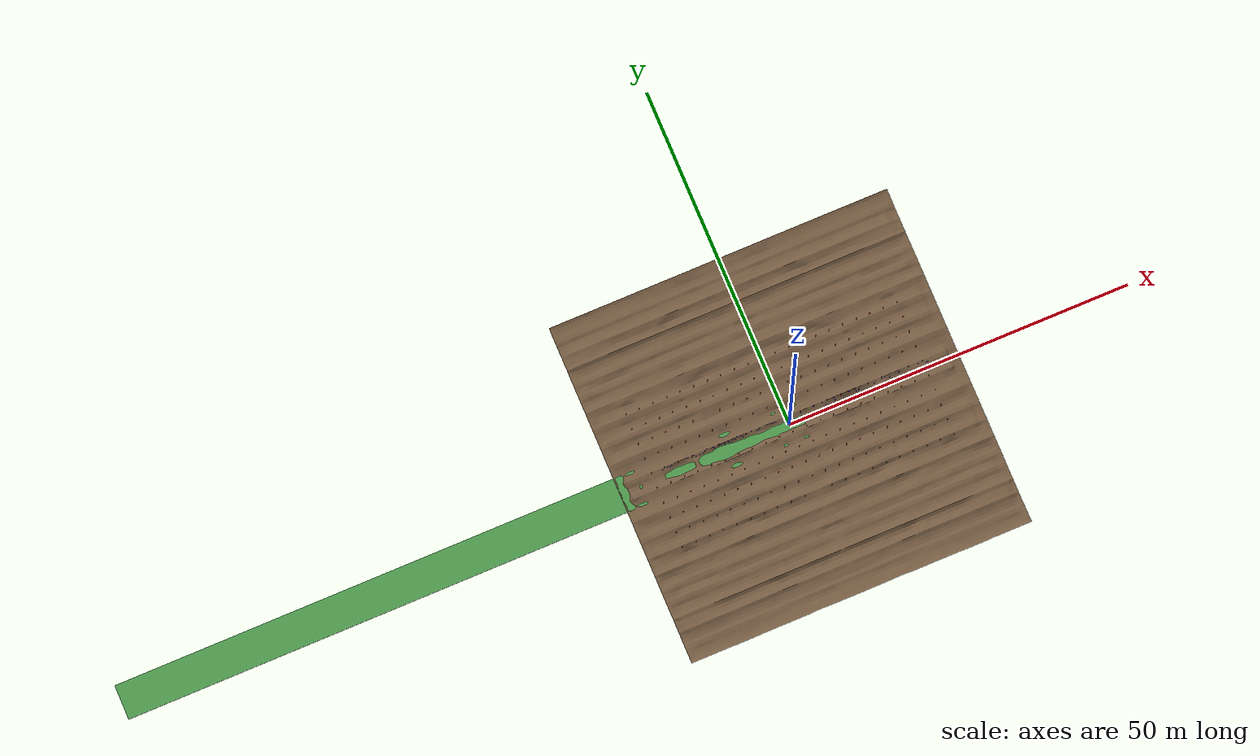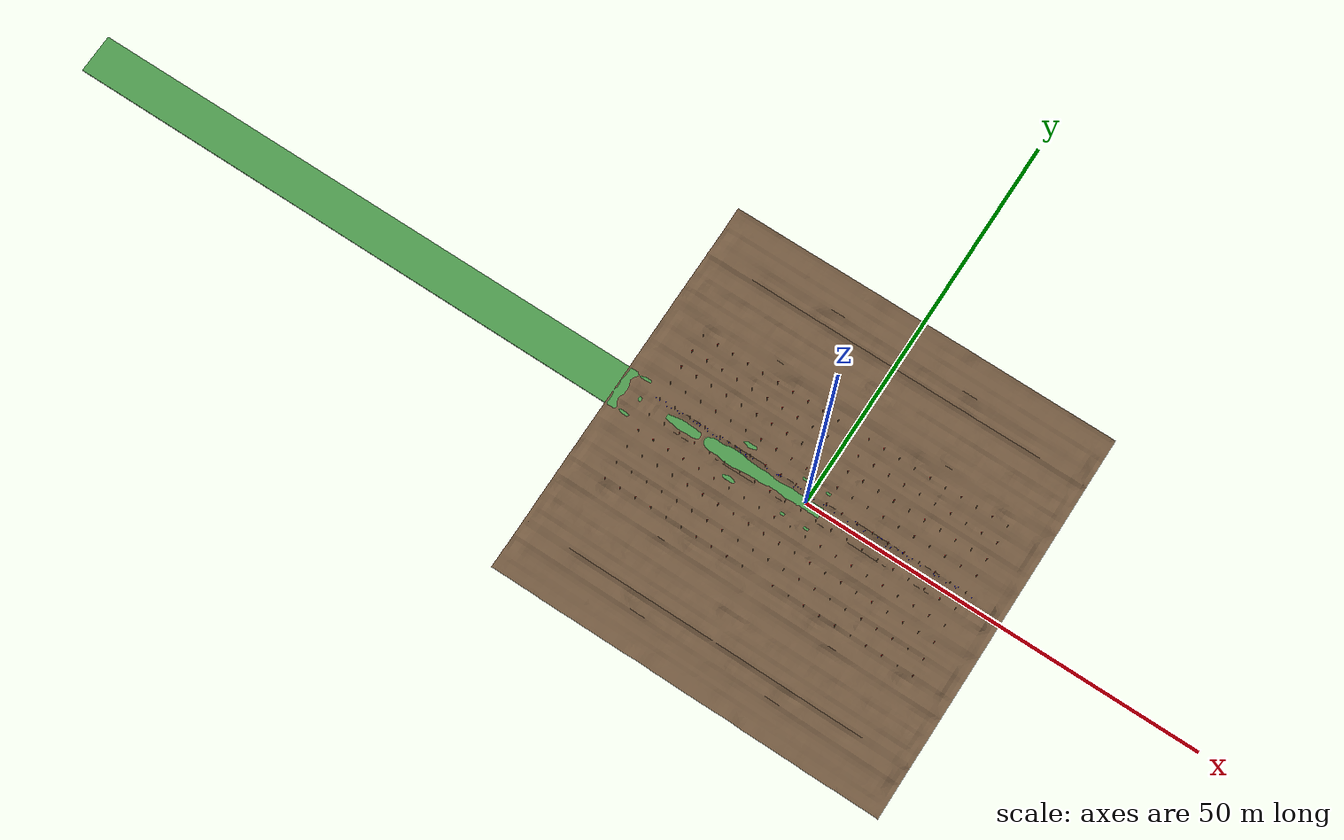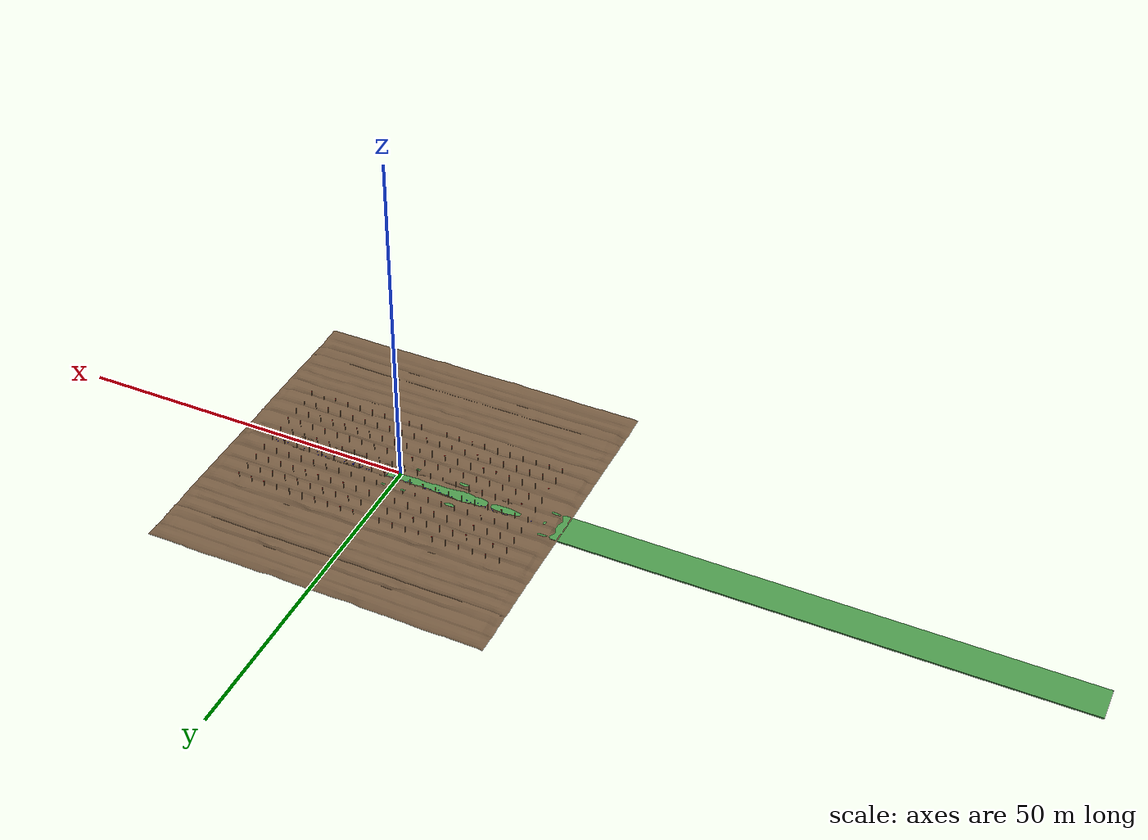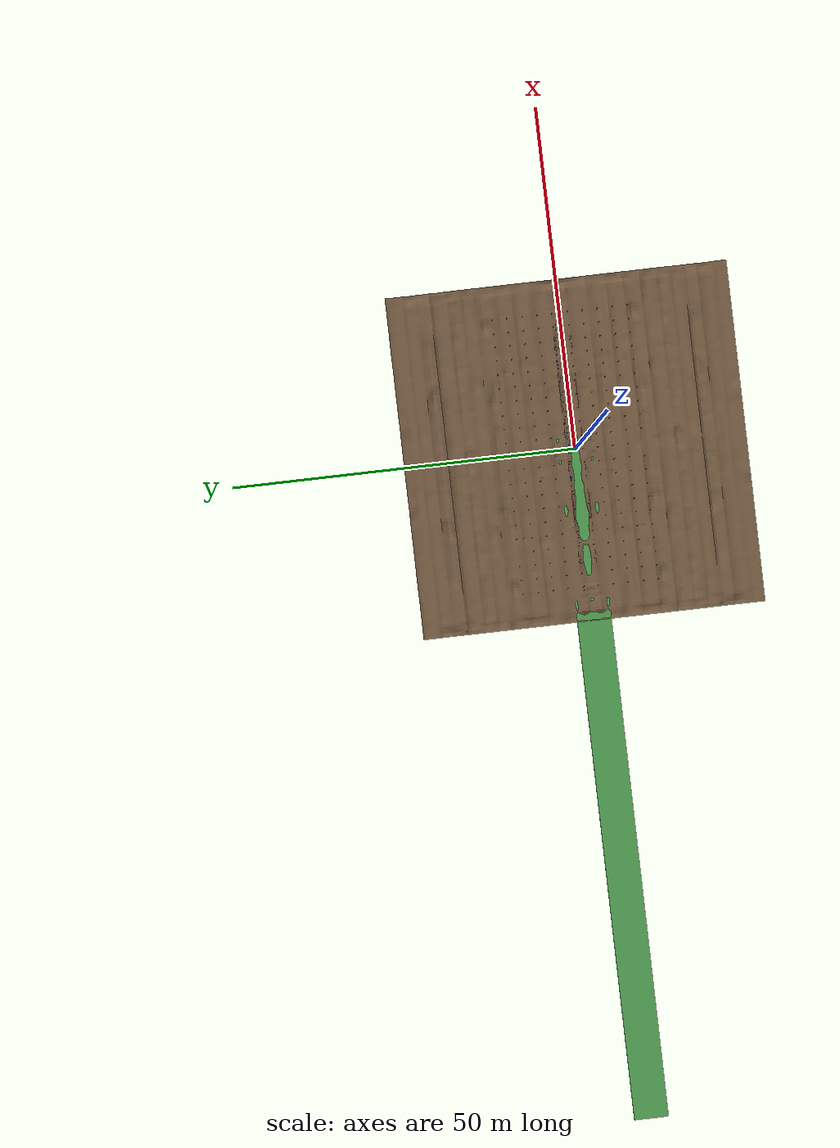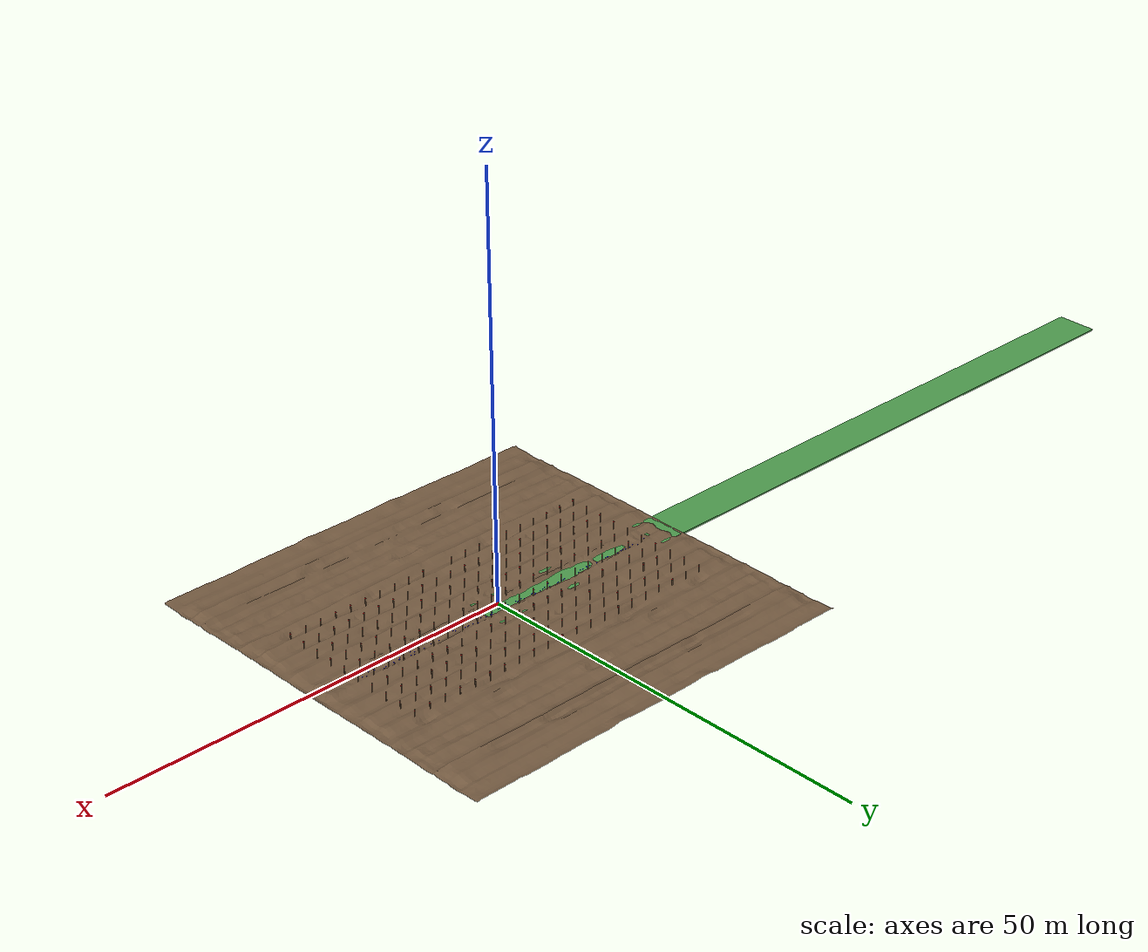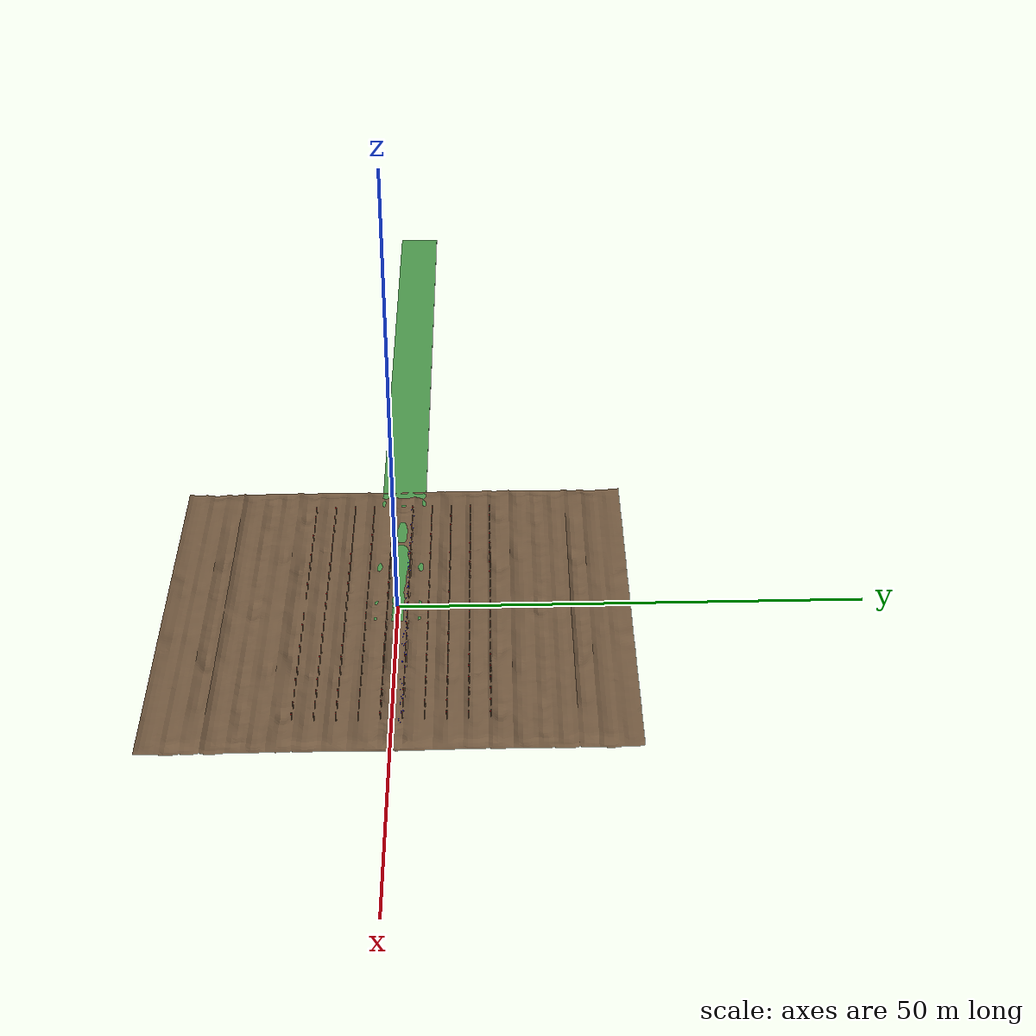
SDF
<sdf version='1.9'>
  <world name='empty'>
    <physics name='1ms' type='ode'>
      <max_step_size>0.001</max_step_size>
      <real_time_factor>1</real_time_factor>
      <real_time_update_rate>1000</real_time_update_rate>
    </physics>
    <plugin name='gz::sim::systems::Physics' filename='ignition-gazebo-physics-system'/>
    <plugin name='gz::sim::systems::UserCommands' filename='ignition-gazebo-user-commands-system'/>
    <plugin name='gz::sim::systems::SceneBroadcaster' filename='ignition-gazebo-scene-broadcaster-system'/>
    <plugin name='gz::sim::systems::Contact' filename='ignition-gazebo-contact-system'/>

    <plugin name='ignition::gazebo::systems::Sensors' filename='ignition-gazebo-sensors-system'/>

    <gravity>0 0 -9.8</gravity>
    <gravity>0 0 -9.8</gravity>
    <magnetic_field>6e-06 2.3e-05 -4.2e-05</magnetic_field>
    <atmosphere type='adiabatic'/>
    <scene>
      <ambient>0.4 0.4 0.4 1</ambient>
      <background>0.7 0.7 0.7 1</background>
      <shadows>true</shadows>
    </scene>
  <!-- ================= FLAT VINEYARD GROUND ================= -->
<model name="vineyard_ground">
  <static>true</static>

  <!-- Centered between x=1 and x=-99 -->
  <!-- Midpoint = -49 -->
  <pose>-48 0 -0.6 0 0 0</pose>

  <!-- ===== Collision ===== -->
  <link name="ground_link">
    <collision name="collision">
      <geometry>
        <box>
          <size>100 5 0.2</size>
        </box>
      </geometry>
      <surface>
        <contact>
          <collide_without_contact>false</collide_without_contact>
        </contact>
        <friction>
          <ode>
            <mu>1.0</mu>
            <mu2>1.0</mu2>
          </ode>
        </friction>
      </surface>
    </collision>

    <!-- ===== Visual ===== -->
    <visual name="visual">
      <geometry>
        <box>
          <size>100 5 0.2</size>
        </box>
      </geometry>
      <material>
        <ambient>0.3 0.6 0.3 1</ambient>
        <diffuse>0.3 0.6 0.3 1</diffuse>
        <specular>0.1 0.1 0.1 1</specular>
      </material>
    </visual>
  </link>
</model>

    <!--  Vineyard heightmap terrain (50m x 50m, ~0.5m height span) -->
    <!--  Put vineyard_heightmap.png next to this world file, or   -->
  <model name="vineyard_mesh_inline">
    <static>true</static>
    <!-- x  y   z    R    P      Y(=90deg) -->
    <pose>0 0 -0.4 0 0 1.5707963</pose>
    <link name="terrain">
      <collision name="col">
        <geometry>
          <mesh>
            <uri>file:///home/alex/.ignition/gazebo/models/vineyard_mesh/meshes/5050vinefinal.dae</uri>
            <scale>1 1 1</scale>
          </mesh>
        </geometry>
      </collision>
      <visual name="vis">
        <geometry>
          <mesh>
            <uri>file:///home/alex/.ignition/gazebo/models/vineyard_mesh/meshes/5050vinefinal.dae</uri>
            <scale>1 1 1</scale>
          </mesh>
        </geometry>
        <material>
          <ambient>0.4 0.3 0.2 1</ambient>
          <diffuse>0.45 0.35 0.25 1</diffuse>
          <specular>0.1 0.1 0.1 1</specular>
        </material>
      </visual>
    </link>
  </model>

    <!-- =========== INLINE VINE POSTS + RED BALLS =========== -->

    <!-- ROW 1: Y = +1.1 -->

    <model name='row1_post_00'>
      <static>true</static>
      <pose>0 1.1 -0.5 0 0 0</pose>
      <link name='vine_link'>
        <collision name='post_collision'>
          <geometry>
            <cylinder>
              <radius>0.05</radius>
              <length>1.2</length>
            </cylinder>
          </geometry>
          <pose>0 0 0.6 0 0 0</pose>
        </collision>
        <visual name='post_visual'>
          <geometry>
            <cylinder>
              <radius>0.05</radius>
              <length>1.2</length>
            </cylinder>
          </geometry>
          <pose>0 0 0.6 0 0 0</pose>
          <material>
            <diffuse>0.4 0.3 0.2 1</diffuse>
            <ambient>0.4 0.3 0.2 1</ambient>
          </material>
        </visual>
        <collision name='ball_collision'>
          <geometry>
            <sphere>
              <radius>0.07</radius>
            </sphere>
          </geometry>
          <pose>0 0 1.0 0 0 0</pose>
        </collision>
        <visual name='ball_visual'>
          <geometry>
            <sphere>
              <radius>0.07</radius>
            </sphere>
          </geometry>
          <pose>0 0 1.0 0 0 0</pose>
          <material>
            <diffuse>0.9 0.1 0.1 1</diffuse>
            <ambient>0.9 0.1 0.1 1</ambient>
          </material>
        </visual>
      </link>
    </model>

    <model name='row1_post_1'>
      <static>true</static>
      <pose>2 1.1 -0.5 0 0 0</pose>
      <link name='vine_link'>
        <collision name='post_collision'>
          <geometry>
            <cylinder>
              <radius>0.05</radius>
              <length>1.2</length>
            </cylinder>
          </geometry>
          <pose>0 0 0.6 0 0 0</pose>
        </collision>
        <visual name='post_visual'>
          <geometry>
            <cylinder>
              <radius>0.05</radius>
              <length>1.2</length>
            </cylinder>
          </geometry>
          <pose>0 0 0.6 0 0 0</pose>
          <material>
            <diffuse>0.4 0.3 0.2 1</diffuse>
            <ambient>0.4 0.3 0.2 1</ambient>
          </material>
        </visual>
        <collision name='ball_collision'>
          <geometry>
            <sphere>
              <radius>0.07</radius>
            </sphere>
          </geometry>
          <pose>0 0 1.0 0 0 0</pose>
        </collision>
        <visual name='ball_visual'>
          <geometry>
            <sphere>
              <radius>0.07</radius>
            </sphere>
          </geometry>
          <pose>0 0 1.0 0 0 0</pose>
          <material>
            <diffuse>0.9 0.1 0.1 1</diffuse>
            <ambient>0.9 0.1 0.1 1</ambient>
          </material>
        </visual>
      </link>
    </model>

    <model name='row1_post_2'>
      <static>true</static>
      <pose>4 1.1 -0.5 0 0 0</pose>
      <link name='vine_link'>
        <collision name='post_collision'>
          <geometry>
            <cylinder>
              <radius>0.05</radius>
              <length>1.2</length>
            </cylinder>
          </geometry>
          <pose>0 0 0.6 0 0 0</pose>
        </collision>
        <visual name='post_visual'>
          <geometry>
            <cylinder>
              <radius>0.05</radius>
              <length>1.2</length>
            </cylinder>
          </geometry>
          <pose>0 0 0.6 0 0 0</pose>
          <material>
            <diffuse>0.4 0.3 0.2 1</diffuse>
            <ambient>0.4 0.3 0.2 1</ambient>
          </material>
        </visual>
        <collision name='ball_collision'>
          <geometry>
            <sphere>
              <radius>0.07</radius>
            </sphere>
          </geometry>
          <pose>0 0 1.0 0 0 0</pose>
        </collision>
        <visual name='ball_visual'>
          <geometry>
            <sphere>
              <radius>0.07</radius>
            </sphere>
          </geometry>
          <pose>0 0 1.0 0 0 0</pose>
          <material>
            <diffuse>0.9 0.1 0.1 1</diffuse>
            <ambient>0.9 0.1 0.1 1</ambient>
          </material>
        </visual>
      </link>
    </model>

    <model name='row1_post_3'>
      <static>true</static>
      <pose>6 1.1 -0.5 0 0 0</pose>
      <link name='vine_link'>
        <collision name='post_collision'>
          <geometry>
            <cylinder>
              <radius>0.05</radius>
              <length>1.2</length>
            </cylinder>
          </geometry>
          <pose>0 0 0.6 0 0 0</pose>
        </collision>
        <visual name='post_visual'>
          <geometry>
            <cylinder>
              <radius>0.05</radius>
              <length>1.2</length>
            </cylinder>
          </geometry>
          <pose>0 0 0.6 0 0 0</pose>
          <material>
            <diffuse>0.4 0.3 0.2 1</diffuse>
            <ambient>0.4 0.3 0.2 1</ambient>
          </material>
        </visual>
        <collision name='ball_collision'>
          <geometry>
            <sphere>
              <radius>0.07</radius>
            </sphere>
          </geometry>
          <pose>0 0 1.0 0 0 0</pose>
        </collision>
        <visual name='ball_visual'>
          <geometry>
            <sphere>
              <radius>0.07</radius>
            </sphere>
          </geometry>
          <pose>0 0 1.0 0 0 0</pose>
          <material>
            <diffuse>0.9 0.1 0.1 1</diffuse>
            <ambient>0.9 0.1 0.1 1</ambient>
          </material>
        </visual>
      </link>
    </model>

    <model name='row1_post_4'>
      <static>true</static>
      <pose>8 1.1 -0.5 0 0 0</pose>
      <link name='vine_link'>
        <collision name='post_collision'>
          <geometry>
            <cylinder>
              <radius>0.05</radius>
              <length>1.2</length>
            </cylinder>
          </geometry>
          <pose>0 0 0.6 0 0 0</pose>
        </collision>
        <visual name='post_visual'>
          <geometry>
            <cylinder>
              <radius>0.05</radius>
              <length>1.2</length>
            </cylinder>
          </geometry>
          <pose>0 0 0.6 0 0 0</pose>
          <material>
            <diffuse>0.4 0.3 0.2 1</diffuse>
            <ambient>0.4 0.3 0.2 1</ambient>
          </material>
        </visual>
        <collision name='ball_collision'>
          <geometry>
            <sphere>
              <radius>0.07</radius>
            </sphere>
          </geometry>
          <pose>0 0 1.0 0 0 0</pose>
        </collision>
        <visual name='ball_visual'>
          <geometry>
            <sphere>
              <radius>0.07</radius>
            </sphere>
          </geometry>
          <pose>0 0 1.0 0 0 0</pose>
          <material>
            <diffuse>0.9 0.1 0.1 1</diffuse>
            <ambient>0.9 0.1 0.1 1</ambient>
          </material>
        </visual>
      </link>
    </model>

    <model name='row1_post_5'>
      <static>true</static>
      <pose>10 1.1 -0.5 0 0 0</pose>
      <link name='vine_link'>
        <collision name='post_collision'>
          <geometry>
            <cylinder>
              <radius>0.05</radius>
              <length>1.2</length>
            </cylinder>
          </geometry>
          <pose>0 0 0.6 0 0 0</pose>
        </collision>
        <visual name='post_visual'>
          <geometry>
            <cylinder>
              <radius>0.05</radius>
              <length>1.2</length>
            </cylinder>
          </geometry>
          <pose>0 0 0.6 0 0 0</pose>
          <material>
            <diffuse>0.4 0.3 0.2 1</diffuse>
            <ambient>0.4 0.3 0.2 1</ambient>
          </material>
        </visual>
        <collision name='ball_collision'>
          <geometry>
            <sphere>
              <radius>0.07</radius>
            </sphere>
          </geometry>
          <pose>0 0 1.0 0 0 0</pose>
        </collision>
        <visual name='ball_visual'>
          <geometry>
            <sphere>
              <radius>0.07</radius>
            </sphere>
          </geometry>
          <pose>0 0 1.0 0 0 0</pose>
          <material>
            <diffuse>0.9 0.1 0.1 1</diffuse>
            <ambient>0.9 0.1 0.1 1</ambient>
          </material>
        </visual>
      </link>
    </model>

    <model name='row1_post_6'>
      <static>true</static>
      <pose>12 1.1 -0.5 0 0 0</pose>
      <link name='vine_link'>
        <collision name='post_collision'>
          <geometry>
            <cylinder>
              <radius>0.05</radius>
              <length>1.2</length>
            </cylinder>
          </geometry>
          <pose>0 0 0.6 0 0 0</pose>
        </collision>
        <visual name='post_visual'>
          <geometry>
            <cylinder>
              <radius>0.05</radius>
              <length>1.2</length>
            </cylinder>
          </geometry>
          <pose>0 0 0.6 0 0 0</pose>
          <material>
            <diffuse>0.4 0.3 0.2 1</diffuse>
            <ambient>0.4 0.3 0.2 1</ambient>
          </material>
        </visual>
        <collision name='ball_collision'>
          <geometry>
            <sphere>
              <radius>0.07</radius>
            </sphere>
          </geometry>
          <pose>0 0 1.0 0 0 0</pose>
        </collision>
        <visual name='ball_visual'>
          <geometry>
            <sphere>
              <radius>0.07</radius>
            </sphere>
          </geometry>
          <pose>0 0 1.0 0 0 0</pose>
          <material>
            <diffuse>0.9 0.1 0.1 1</diffuse>
            <ambient>0.9 0.1 0.1 1</ambient>
          </material>
        </visual>
      </link>
    </model>

    <model name='row1_post_7'>
      <static>true</static>
      <pose>14 1.1 -0.5 0 0 0</pose>
      <link name='vine_link'>
        <collision name='post_collision'>
          <geometry>
            <cylinder>
              <radius>0.05</radius>
              <length>1.2</length>
            </cylinder>
          </geometry>
          <pose>0 0 0.6 0 0 0</pose>
        </collision>
        <visual name='post_visual'>
          <geometry>
            <cylinder>
              <radius>0.05</radius>
              <length>1.2</length>
            </cylinder>
          </geometry>
          <pose>0 0 0.6 0 0 0</pose>
          <material>
            <diffuse>0.4 0.3 0.2 1</diffuse>
            <ambient>0.4 0.3 0.2 1</ambient>
          </material>
        </visual>
        <collision name='ball_collision'>
          <geometry>
            <sphere>
              <radius>0.07</radius>
            </sphere>
          </geometry>
          <pose>0 0 1.0 0 0 0</pose>
        </collision>
        <visual name='ball_visual'>
          <geometry>
            <sphere>
              <radius>0.07</radius>
            </sphere>
          </geometry>
          <pose>0 0 1.0 0 0 0</pose>
          <material>
            <diffuse>0.9 0.1 0.1 1</diffuse>
            <ambient>0.9 0.1 0.1 1</ambient>
          </material>
        </visual>
      </link>
    </model>

    <model name='row1_post_8'>
      <static>true</static>
      <pose>16 1.1 -0.5 0 0 0</pose>
      <link name='vine_link'>
        <collision name='post_collision'>
          <geometry>
            <cylinder>
              <radius>0.05</radius>
              <length>1.2</length>
            </cylinder>
          </geometry>
          <pose>0 0 0.6 0 0 0</pose>
        </collision>
        <visual name='post_visual'>
          <geometry>
            <cylinder>
              <radius>0.05</radius>
              <length>1.2</length>
            </cylinder>
          </geometry>
          <pose>0 0 0.6 0 0 0</pose>
          <material>
            <diffuse>0.4 0.3 0.2 1</diffuse>
            <ambient>0.4 0.3 0.2 1</ambient>
          </material>
        </visual>
        <collision name='ball_collision'>
          <geometry>
            <sphere>
              <radius>0.07</radius>
            </sphere>
          </geometry>
          <pose>0 0 1.0 0 0 0</pose>
        </collision>
        <visual name='ball_visual'>
          <geometry>
            <sphere>
              <radius>0.07</radius>
            </sphere>
          </geometry>
          <pose>0 0 1.0 0 0 0</pose>
          <material>
            <diffuse>0.9 0.1 0.1 1</diffuse>
            <ambient>0.9 0.1 0.1 1</ambient>
          </material>
        </visual>
      </link>
    </model>

    <model name='row1_post_9'>
      <static>true</static>
      <pose>18 1.1 -0.5 0 0 0</pose>
      <link name='vine_link'>
        <collision name='post_collision'>
          <geometry>
            <cylinder>
              <radius>0.05</radius>
              <length>1.2</length>
            </cylinder>
          </geometry>
          <pose>0 0 0.6 0 0 0</pose>
        </collision>
        <visual name='post_visual'>
          <geometry>
            <cylinder>
              <radius>0.05</radius>
              <length>1.2</length>
            </cylinder>
          </geometry>
          <pose>0 0 0.6 0 0 0</pose>
          <material>
            <diffuse>0.4 0.3 0.2 1</diffuse>
            <ambient>0.4 0.3 0.2 1</ambient>
          </material>
        </visual>
        <collision name='ball_collision'>
          <geometry>
            <sphere>
              <radius>0.07</radius>
            </sphere>
          </geometry>
          <pose>0 0 1.0 0 0 0</pose>
        </collision>
        <visual name='ball_visual'>
          <geometry>
            <sphere>
              <radius>0.07</radius>
            </sphere>
          </geometry>
          <pose>0 0 1.0 0 0 0</pose>
          <material>
            <diffuse>0.9 0.1 0.1 1</diffuse>
            <ambient>0.9 0.1 0.1 1</ambient>
          </material>
        </visual>
      </link>
    </model>

    <model name='row1_post_10'>
      <static>true</static>
      <pose>20 1.1 -0.5 0 0 0</pose>
      <link name='vine_link'>
        <collision name='post_collision'>
          <geometry>
            <cylinder>
              <radius>0.05</radius>
              <length>1.2</length>
            </cylinder>
          </geometry>
          <pose>0 0 0.6 0 0 0</pose>
        </collision>
        <visual name='post_visual'>
          <geometry>
            <cylinder>
              <radius>0.05</radius>
              <length>1.2</length>
            </cylinder>
          </geometry>
          <pose>0 0 0.6 0 0 0</pose>
          <material>
            <diffuse>0.4 0.3 0.2 1</diffuse>
            <ambient>0.4 0.3 0.2 1</ambient>
          </material>
        </visual>
        <collision name='ball_collision'>
          <geometry>
            <sphere>
              <radius>0.07</radius>
            </sphere>
          </geometry>
          <pose>0 0 1.0 0 0 0</pose>
        </collision>
        <visual name='ball_visual'>
          <geometry>
            <sphere>
              <radius>0.07</radius>
            </sphere>
          </geometry>
          <pose>0 0 1.0 0 0 0</pose>
          <material>
            <diffuse>0.9 0.1 0.1 1</diffuse>
            <ambient>0.9 0.1 0.1 1</ambient>
          </material>
        </visual>
      </link>
    </model>

    <!-- ROW 2: Y = -1.1 -->

    <model name='row2_post_00'>
      <static>true</static>
      <pose>0 -1.1 -0.5 0 0 0</pose>
      <link name='vine_link'>
        <collision name='post_collision'>
          <geometry>
            <cylinder>
              <radius>0.05</radius>
              <length>1.2</length>
            </cylinder>
          </geometry>
          <pose>0 0 0.6 0 0 0</pose>
        </collision>
        <visual name='post_visual'>
          <geometry>
            <cylinder>
              <radius>0.05</radius>
              <length>1.2</length>
            </cylinder>
          </geometry>
          <pose>0 0 0.6 0 0 0</pose>
          <material>
            <diffuse>0.4 0.3 0.2 1</diffuse>
            <ambient>0.4 0.3 0.2 1</ambient>
          </material>
        </visual>
        <collision name='ball_collision'>
          <geometry>
            <sphere>
              <radius>0.07</radius>
            </sphere>
          </geometry>
          <pose>0 0 1.0 0 0 0</pose>
        </collision>
        <visual name='ball_visual'>
          <geometry>
            <sphere>
              <radius>0.07</radius>
            </sphere>
          </geometry>
          <pose>0 0 1.0 0 0 0</pose>
          <material>
            <diffuse>0.9 0.1 0.1 1</diffuse>
            <ambient>0.9 0.1 0.1 1</ambient>
          </material>
        </visual>
      </link>
    </model>

    <model name='row2_post_1'>
      <static>true</static>
      <pose>2 -1.1 -0.5 0 0 0</pose>
      <link name='vine_link'>
        <collision name='post_collision'>
          <geometry>
            <cylinder>
              <radius>0.05</radius>
              <length>1.2</length>
            </cylinder>
          </geometry>
          <pose>0 0 0.6 0 0 0</pose>
        </collision>
        <visual name='post_visual'>
          <geometry>
            <cylinder>
              <radius>0.05</radius>
              <length>1.2</length>
            </cylinder>
          </geometry>
          <pose>0 0 0.6 0 0 0</pose>
          <material>
            <diffuse>0.4 0.3 0.2 1</diffuse>
            <ambient>0.4 0.3 0.2 1</ambient>
          </material>
        </visual>
        <collision name='ball_collision'>
          <geometry>
            <sphere>
              <radius>0.07</radius>
            </sphere>
          </geometry>
          <pose>0 0 1.0 0 0 0</pose>
        </collision>
        <visual name='ball_visual'>
          <geometry>
            <sphere>
              <radius>0.07</radius>
            </sphere>
          </geometry>
          <pose>0 0 1.0 0 0 0</pose>
          <material>
            <diffuse>0.9 0.1 0.1 1</diffuse>
            <ambient>0.9 0.1 0.1 1</ambient>
          </material>
        </visual>
      </link>
    </model>

    <model name='row2_post_2'>
      <static>true</static>
      <pose>4 -1.1 -0.5 0 0 0</pose>
      <link name='vine_link'>
        <collision name='post_collision'>
          <geometry>
            <cylinder>
              <radius>0.05</radius>
              <length>1.2</length>
            </cylinder>
          </geometry>
          <pose>0 0 0.6 0 0 0</pose>
        </collision>
        <visual name='post_visual'>
          <geometry>
            <cylinder>
              <radius>0.05</radius>
              <length>1.2</length>
            </cylinder>
          </geometry>
          <pose>0 0 0.6 0 0 0</pose>
          <material>
            <diffuse>0.4 0.3 0.2 1</diffuse>
            <ambient>0.4 0.3 0.2 1</ambient>
          </material>
        </visual>
        <collision name='ball_collision'>
          <geometry>
            <sphere>
              <radius>0.07</radius>
            </sphere>
          </geometry>
          <pose>0 0 1.0 0 0 0</pose>
        </collision>
        <visual name='ball_visual'>
          <geometry>
            <sphere>
              <radius>0.07</radius>
            </sphere>
          </geometry>
          <pose>0 0 1.0 0 0 0</pose>
          <material>
            <diffuse>0.9 0.1 0.1 1</diffuse>
            <ambient>0.9 0.1 0.1 1</ambient>
          </material>
        </visual>
      </link>
    </model>

    <model name='row2_post_3'>
      <static>true</static>
      <pose>6 -1.1 -0.5 0 0 0</pose>
      <link name='vine_link'>
        <collision name='post_collision'>
          <geometry>
            <cylinder>
              <radius>0.05</radius>
              <length>1.2</length>
            </cylinder>
          </geometry>
          <pose>0 0 0.6 0 0 0</pose>
        </collision>
        <visual name='post_visual'>
          <geometry>
            <cylinder>
              <radius>0.05</radius>
              <length>1.2</length>
            </cylinder>
          </geometry>
          <pose>0 0 0.6 0 0 0</pose>
          <material>
            <diffuse>0.4 0.3 0.2 1</diffuse>
            <ambient>0.4 0.3 0.2 1</ambient>
          </material>
        </visual>
        <collision name='ball_collision'>
          <geometry>
            <sphere>
              <radius>0.07</radius>
            </sphere>
          </geometry>
          <pose>0 0 1.0 0 0 0</pose>
        </collision>
        <visual name='ball_visual'>
          <geometry>
            <sphere>
              <radius>0.07</radius>
            </sphere>
          </geometry>
          <pose>0 0 1.0 0 0 0</pose>
          <material>
            <diffuse>0.9 0.1 0.1 1</diffuse>
            <ambient>0.9 0.1 0.1 1</ambient>
          </material>
        </visual>
      </link>
    </model>

    <model name='row2_post_4'>
      <static>true</static>
      <pose>8 -1.1 -0.5 0 0 0</pose>
      <link name='vine_link'>
        <collision name='post_collision'>
          <geometry>
            <cylinder>
              <radius>0.05</radius>
              <length>1.2</length>
            </cylinder>
          </geometry>
          <pose>0 0 0.6 0 0 0</pose>
        </collision>
        <visual name='post_visual'>
          <geometry>
            <cylinder>
              <radius>0.05</radius>
              <length>1.2</length>
            </cylinder>
          </geometry>
          <pose>0 0 0.6 0 0 0</pose>
          <material>
            <diffuse>0.4 0.3 0.2 1</diffuse>
            <ambient>0.4 0.3 0.2 1</ambient>
          </material>
        </visual>
        <collision name='ball_collision'>
          <geometry>
            <sphere>
              <radius>0.07</radius>
            </sphere>
          </geometry>
          <pose>0 0 1.0 0 0 0</pose>
        </collision>
        <visual name='ball_visual'>
          <geometry>
            <sphere>
              <radius>0.07</radius>
            </sphere>
          </geometry>
          <pose>0 0 1.0 0 0 0</pose>
          <material>
            <diffuse>0.9 0.1 0.1 1</diffuse>
            <ambient>0.9 0.1 0.1 1</ambient>
          </material>
        </visual>
      </link>
    </model>

    <model name='row2_post_5'>
      <static>true</static>
      <pose>10 -1.1 -0.5 0 0 0</pose>
      <link name='vine_link'>
        <collision name='post_collision'>
          <geometry>
            <cylinder>
              <radius>0.05</radius>
              <length>1.2</length>
            </cylinder>
          </geometry>
          <pose>0 0 0.6 0 0 0</pose>
        </collision>
        <visual name='post_visual'>
          <geometry>
            <cylinder>
              <radius>0.05</radius>
              <length>1.2</length>
            </cylinder>
          </geometry>
          <pose>0 0 0.6 0 0 0</pose>
          <material>
            <diffuse>0.4 0.3 0.2 1</diffuse>
            <ambient>0.4 0.3 0.2 1</ambient>
          </material>
        </visual>
        <collision name='ball_collision'>
          <geometry>
            <sphere>
              <radius>0.07</radius>
            </sphere>
          </geometry>
          <pose>0 0 1.0 0 0 0</pose>
        </collision>
        <visual name='ball_visual'>
          <geometry>
            <sphere>
              <radius>0.07</radius>
            </sphere>
          </geometry>
          <pose>0 0 1.0 0 0 0</pose>
          <material>
            <diffuse>0.9 0.1 0.1 1</diffuse>
            <ambient>0.9 0.1 0.1 1</ambient>
          </material>
        </visual>
      </link>
    </model>

    <model name='row2_post_6'>
      <static>true</static>
      <pose>12 -1.1 -0.5 0 0 0</pose>
      <link name='vine_link'>
        <collision name='post_collision'>
          <geometry>
            <cylinder>
              <radius>0.05</radius>
              <length>1.2</length>
            </cylinder>
          </geometry>
          <pose>0 0 0.6 0 0 0</pose>
        </collision>
        <visual name='post_visual'>
          <geometry>
            <cylinder>
              <radius>0.05</radius>
              <length>1.2</length>
            </cylinder>
          </geometry>
          <pose>0 0 0.6 0 0 0</pose>
          <material>
            <diffuse>0.4 0.3 0.2 1</diffuse>
            <ambient>0.4 0.3 0.2 1</ambient>
          </material>
        </visual>
        <collision name='ball_collision'>
          <geometry>
            <sphere>
              <radius>0.07</radius>
            </sphere>
          </geometry>
          <pose>0 0 1.0 0 0 0</pose>
        </collision>
        <visual name='ball_visual'>
          <geometry>
            <sphere>
              <radius>0.07</radius>
            </sphere>
          </geometry>
          <pose>0 0 1.0 0 0 0</pose>
          <material>
            <diffuse>0.9 0.1 0.1 1</diffuse>
            <ambient>0.9 0.1 0.1 1</ambient>
          </material>
        </visual>
      </link>
    </model>

    <model name='row2_post_7'>
      <static>true</static>
      <pose>14 -1.1 -0.5 0 0 0</pose>
      <link name='vine_link'>
        <collision name='post_collision'>
          <geometry>
            <cylinder>
              <radius>0.05</radius>
              <length>1.2</length>
            </cylinder>
          </geometry>
          <pose>0 0 0.6 0 0 0</pose>
        </collision>
        <visual name='post_visual'>
          <geometry>
            <cylinder>
              <radius>0.05</radius>
              <length>1.2</length>
            </cylinder>
          </geometry>
          <pose>0 0 0.6 0 0 0</pose>
          <material>
            <diffuse>0.4 0.3 0.2 1</diffuse>
            <ambient>0.4 0.3 0.2 1</ambient>
          </material>
        </visual>
        <collision name='ball_collision'>
          <geometry>
            <sphere>
              <radius>0.07</radius>
            </sphere>
          </geometry>
          <pose>0 0 1.0 0 0 0</pose>
        </collision>
        <visual name='ball_visual'>
          <geometry>
            <sphere>
              <radius>0.07</radius>
            </sphere>
          </geometry>
          <pose>0 0 1.0 0 0 0</pose>
          <material>
            <diffuse>0.9 0.1 0.1 1</diffuse>
            <ambient>0.9 0.1 0.1 1</ambient>
          </material>
        </visual>
      </link>
    </model>

    <model name='row2_post_8'>
      <static>true</static>
      <pose>16 -1.1 -0.5 0 0 0</pose>
      <link name='vine_link'>
        <collision name='post_collision'>
          <geometry>
            <cylinder>
              <radius>0.05</radius>
              <length>1.2</length>
            </cylinder>
          </geometry>
          <pose>0 0 0.6 0 0 0</pose>
        </collision>
        <visual name='post_visual'>
          <geometry>
            <cylinder>
              <radius>0.05</radius>
              <length>1.2</length>
            </cylinder>
          </geometry>
          <pose>0 0 0.6 0 0 0</pose>
          <material>
            <diffuse>0.4 0.3 0.2 1</diffuse>
            <ambient>0.4 0.3 0.2 1</ambient>
          </material>
        </visual>
        <collision name='ball_collision'>
          <geometry>
            <sphere>
              <radius>0.07</radius>
            </sphere>
          </geometry>
          <pose>0 0 1.0 0 0 0</pose>
        </collision>
        <visual name='ball_visual'>
          <geometry>
            <sphere>
              <radius>0.07</radius>
            </sphere>
          </geometry>
          <pose>0 0 1.0 0 0 0</pose>
          <material>
            <diffuse>0.9 0.1 0.1 1</diffuse>
            <ambient>0.9 0.1 0.1 1</ambient>
          </material>
        </visual>
      </link>
    </model>

    <model name='row2_post_9'>
      <static>true</static>
      <pose>18 -1.1 -0.5 0 0 0</pose>
      <link name='vine_link'>
        <collision name='post_collision'>
          <geometry>
            <cylinder>
              <radius>0.05</radius>
              <length>1.2</length>
            </cylinder>
          </geometry>
          <pose>0 0 0.6 0 0 0</pose>
        </collision>
        <visual name='post_visual'>
          <geometry>
            <cylinder>
              <radius>0.05</radius>
              <length>1.2</length>
            </cylinder>
          </geometry>
          <pose>0 0 0.6 0 0 0</pose>
          <material>
            <diffuse>0.4 0.3 0.2 1</diffuse>
            <ambient>0.4 0.3 0.2 1</ambient>
          </material>
        </visual>
        <collision name='ball_collision'>
          <geometry>
            <sphere>
              <radius>0.07</radius>
            </sphere>
          </geometry>
          <pose>0 0 1.0 0 0 0</pose>
        </collision>
        <visual name='ball_visual'>
          <geometry>
            <sphere>
              <radius>0.07</radius>
            </sphere>
          </geometry>
          <pose>0 0 1.0 0 0 0</pose>
          <material>
            <diffuse>0.9 0.1 0.1 1</diffuse>
            <ambient>0.9 0.1 0.1 1</ambient>
          </material>
        </visual>
      </link>
    </model>

    <model name='row2_post_10'>
      <static>true</static>
      <pose>20 -1.1 -0.5 0 0 0</pose>
      <link name='vine_link'>
        <collision name='post_collision'>
          <geometry>
            <cylinder>
              <radius>0.05</radius>
              <length>1.2</length>
            </cylinder>
          </geometry>
          <pose>0 0 0.6 0 0 0</pose>
        </collision>
        <visual name='post_visual'>
          <geometry>
            <cylinder>
              <radius>0.05</radius>
              <length>1.2</length>
            </cylinder>
          </geometry>
          <pose>0 0 0.6 0 0 0</pose>
          <material>
            <diffuse>0.4 0.3 0.2 1</diffuse>
            <ambient>0.4 0.3 0.2 1</ambient>
          </material>
        </visual>
        <collision name='ball_collision'>
          <geometry>
            <sphere>
              <radius>0.07</radius>
            </sphere>
          </geometry>
          <pose>0 0 1.0 0 0 0</pose>
        </collision>
        <visual name='ball_visual'>
          <geometry>
            <sphere>
              <radius>0.07</radius>
            </sphere>
          </geometry>
          <pose>0 0 1.0 0 0 0</pose>
          <material>
            <diffuse>0.9 0.1 0.1 1</diffuse>
            <ambient>0.9 0.1 0.1 1</ambient>
          </material>
        </visual>
      </link>
    </model>

    <!-- =========== MIRRORED ROWS (NEGATIVE X) =========== -->
    <!-- ROW 1 MIRROR: Y = +1.1, X = -2, -4, ..., -20 -->

    <model name='row1_post_neg_1'>
      <static>true</static>
      <pose>-2 1.1 -0.5 0 0 0</pose>
      <link name='vine_link'>
        <collision name='post_collision'>
          <geometry>
            <cylinder>
              <radius>0.05</radius>
              <length>1.2</length>
            </cylinder>
          </geometry>
          <pose>0 0 0.6 0 0 0</pose>
        </collision>
        <visual name='post_visual'>
          <geometry>
            <cylinder>
              <radius>0.05</radius>
              <length>1.2</length>
            </cylinder>
          </geometry>
          <pose>0 0 0.6 0 0 0</pose>
          <material>
            <diffuse>0.4 0.3 0.2 1</diffuse>
            <ambient>0.4 0.3 0.2 1</ambient>
          </material>
        </visual>
        <collision name='ball_collision'>
          <geometry>
            <sphere>
              <radius>0.07</radius>
            </sphere>
          </geometry>
          <pose>0 0 1.0 0 0 0</pose>
        </collision>
        <visual name='ball_visual'>
          <geometry>
            <sphere>
              <radius>0.07</radius>
            </sphere>
          </geometry>
          <pose>0 0 1.0 0 0 0</pose>
          <material>
            <diffuse>0.9 0.1 0.1 1</diffuse>
            <ambient>0.9 0.1 0.1 1</ambient>
          </material>
        </visual>
      </link>
    </model>

    <model name='row1_post_neg_2'>
      <static>true</static>
      <pose>-4 1.1 -0.5 0 0 0</pose>
      <link name='vine_link'>
        <collision name='post_collision'>
          <geometry>
            <cylinder>
              <radius>0.05</radius>
              <length>1.2</length>
            </cylinder>
          </geometry>
          <pose>0 0 0.6 0 0 0</pose>
        </collision>
        <visual name='post_visual'>
          <geometry>
            <cylinder>
              <radius>0.05</radius>
              <length>1.2</length>
            </cylinder>
          </geometry>
          <pose>0 0 0.6 0 0 0</pose>
          <material>
            <diffuse>0.4 0.3 0.2 1</diffuse>
            <ambient>0.4 0.3 0.2 1</ambient>
          </material>
        </visual>
        <collision name='ball_collision'>
          <geometry>
            <sphere>
              <radius>0.07</radius>
            </sphere>
          </geometry>
          <pose>0 0 1.0 0 0 0</pose>
        </collision>
        <visual name='ball_visual'>
          <geometry>
            <sphere>
              <radius>0.07</radius>
            </sphere>
          </geometry>
          <pose>0 0 1.0 0 0 0</pose>
          <material>
            <diffuse>0.9 0.1 0.1 1</diffuse>
            <ambient>0.9 0.1 0.1 1</ambient>
          </material>
        </visual>
      </link>
    </model>

    <model name='row1_post_neg_3'>
      <static>true</static>
      <pose>-6 1.1 -0.5 0 0 0</pose>
      <link name='vine_link'>
        <collision name='post_collision'>
          <geometry>
            <cylinder>
              <radius>0.05</radius>
              <length>1.2</length>
            </cylinder>
          </geometry>
          <pose>0 0 0.6 0 0 0</pose>
        </collision>
        <visual name='post_visual'>
          <geometry>
            <cylinder>
              <radius>0.05</radius>
              <length>1.2</length>
            </cylinder>
          </geometry>
          <pose>0 0 0.6 0 0 0</pose>
          <material>
            <diffuse>0.4 0.3 0.2 1</diffuse>
            <ambient>0.4 0.3 0.2 1</ambient>
          </material>
        </visual>
        <collision name='ball_collision'>
          <geometry>
            <sphere>
              <radius>0.07</radius>
            </sphere>
          </geometry>
          <pose>0 0 1.0 0 0 0</pose>
        </collision>
        <visual name='ball_visual'>
          <geometry>
            <sphere>
              <radius>0.07</radius>
            </sphere>
          </geometry>
          <pose>0 0 1.0 0 0 0</pose>
          <material>
            <diffuse>0.9 0.1 0.1 1</diffuse>
            <ambient>0.9 0.1 0.1 1</ambient>
          </material>
        </visual>
      </link>
    </model>

    <model name='row1_post_neg_4'>
      <static>true</static>
      <pose>-8 1.1 -0.5 0 0 0</pose>
      <link name='vine_link'>
        <collision name='post_collision'>
          <geometry>
            <cylinder>
              <radius>0.05</radius>
              <length>1.2</length>
            </cylinder>
          </geometry>
          <pose>0 0 0.6 0 0 0</pose>
        </collision>
        <visual name='post_visual'>
          <geometry>
            <cylinder>
              <radius>0.05</radius>
              <length>1.2</length>
            </cylinder>
          </geometry>
          <pose>0 0 0.6 0 0 0</pose>
          <material>
            <diffuse>0.4 0.3 0.2 1</diffuse>
            <ambient>0.4 0.3 0.2 1</ambient>
          </material>
        </visual>
        <collision name='ball_collision'>
          <geometry>
            <sphere>
              <radius>0.07</radius>
            </sphere>
          </geometry>
          <pose>0 0 1.0 0 0 0</pose>
        </collision>
        <visual name='ball_visual'>
          <geometry>
            <sphere>
              <radius>0.07</radius>
            </sphere>
          </geometry>
          <pose>0 0 1.0 0 0 0</pose>
          <material>
            <diffuse>0.9 0.1 0.1 1</diffuse>
            <ambient>0.9 0.1 0.1 1</ambient>
          </material>
        </visual>
      </link>
    </model>

    <model name='row1_post_neg_5'>
      <static>true</static>
      <pose>-10 1.1 -0.5 0 0 0</pose>
      <link name='vine_link'>
        <collision name='post_collision'>
          <geometry>
            <cylinder>
              <radius>0.05</radius>
              <length>1.2</length>
            </cylinder>
          </geometry>
          <pose>0 0 0.6 0 0 0</pose>
        </collision>
        <visual name='post_visual'>
          <geometry>
            <cylinder>
              <radius>0.05</radius>
              <length>1.2</length>
            </cylinder>
          </geometry>
          <pose>0 0 0.6 0 0 0</pose>
          <material>
            <diffuse>0.4 0.3 0.2 1</diffuse>
            <ambient>0.4 0.3 0.2 1</ambient>
          </material>
        </visual>
        <collision name='ball_collision'>
          <geometry>
            <sphere>
              <radius>0.07</radius>
            </sphere>
          </geometry>
          <pose>0 0 1.0 0 0 0</pose>
        </collision>
        <visual name='ball_visual'>
          <geometry>
            <sphere>
              <radius>0.07</radius>
            </sphere>
          </geometry>
          <pose>0 0 1.0 0 0 0</pose>
          <material>
            <diffuse>0.9 0.1 0.1 1</diffuse>
            <ambient>0.9 0.1 0.1 1</ambient>
          </material>
        </visual>
      </link>
    </model>

    <model name='row1_post_neg_6'>
      <static>true</static>
      <pose>-12 1.1 -0.5 0 0 0</pose>
      <link name='vine_link'>
        <collision name='post_collision'>
          <geometry>
            <cylinder>
              <radius>0.05</radius>
              <length>1.2</length>
            </cylinder>
          </geometry>
          <pose>0 0 0.6 0 0 0</pose>
        </collision>
        <visual name='post_visual'>
          <geometry>
            <cylinder>
              <radius>0.05</radius>
              <length>1.2</length>
            </cylinder>
          </geometry>
          <pose>0 0 0.6 0 0 0</pose>
          <material>
            <diffuse>0.4 0.3 0.2 1</diffuse>
            <ambient>0.4 0.3 0.2 1</ambient>
          </material>
        </visual>
        <collision name='ball_collision'>
          <geometry>
            <sphere>
              <radius>0.07</radius>
            </sphere>
          </geometry>
          <pose>0 0 1.0 0 0 0</pose>
        </collision>
        <visual name='ball_visual'>
          <geometry>
            <sphere>
              <radius>0.07</radius>
            </sphere>
          </geometry>
          <pose>0 0 1.0 0 0 0</pose>
          <material>
            <diffuse>0.9 0.1 0.1 1</diffuse>
            <ambient>0.9 0.1 0.1 1</ambient>
          </material>
        </visual>
      </link>
    </model>

    <model name='row1_post_neg_7'>
      <static>true</static>
      <pose>-14 1.1 -0.5 0 0 0</pose>
      <link name='vine_link'>
        <collision name='post_collision'>
          <geometry>
            <cylinder>
              <radius>0.05</radius>
              <length>1.2</length>
            </cylinder>
          </geometry>
          <pose>0 0 0.6 0 0 0</pose>
        </collision>
        <visual name='post_visual'>
          <geometry>
            <cylinder>
              <radius>0.05</radius>
              <length>1.2</length>
            </cylinder>
          </geometry>
          <pose>0 0 0.6 0 0 0</pose>
          <material>
            <diffuse>0.4 0.3 0.2 1</diffuse>
            <ambient>0.4 0.3 0.2 1</ambient>
          </material>
        </visual>
        <collision name='ball_collision'>
          <geometry>
            <sphere>
              <radius>0.07</radius>
            </sphere>
          </geometry>
          <pose>0 0 1.0 0 0 0</pose>
        </collision>
        <visual name='ball_visual'>
          <geometry>
            <sphere>
              <radius>0.07</radius>
            </sphere>
          </geometry>
          <pose>0 0 1.0 0 0 0</pose>
          <material>
            <diffuse>0.9 0.1 0.1 1</diffuse>
            <ambient>0.9 0.1 0.1 1</ambient>
          </material>
        </visual>
      </link>
    </model>

    <model name='row1_post_neg_8'>
      <static>true</static>
      <pose>-16 1.1 -0.5 0 0 0</pose>
      <link name='vine_link'>
        <collision name='post_collision'>
          <geometry>
            <cylinder>
              <radius>0.05</radius>
              <length>1.2</length>
            </cylinder>
          </geometry>
          <pose>0 0 0.6 0 0 0</pose>
        </collision>
        <visual name='post_visual'>
          <geometry>
            <cylinder>
              <radius>0.05</radius>
              <length>1.2</length>
            </cylinder>
          </geometry>
          <pose>0 0 0.6 0 0 0</pose>
          <material>
            <diffuse>0.4 0.3 0.2 1</diffuse>
            <ambient>0.4 0.3 0.2 1</ambient>
          </material>
        </visual>
        <collision name='ball_collision'>
          <geometry>
            <sphere>
              <radius>0.07</radius>
            </sphere>
          </geometry>
          <pose>0 0 1.0 0 0 0</pose>
        </collision>
        <visual name='ball_visual'>
          <geometry>
            <sphere>
              <radius>0.07</radius>
            </sphere>
          </geometry>
          <pose>0 0 1.0 0 0 0</pose>
          <material>
            <diffuse>0.9 0.1 0.1 1</diffuse>
            <ambient>0.9 0.1 0.1 1</ambient>
          </material>
        </visual>
      </link>
    </model>

    <model name='row1_post_neg_9'>
      <static>true</static>
      <pose>-18 1.1 -0.5 0 0 0</pose>
      <link name='vine_link'>
        <collision name='post_collision'>
          <geometry>
            <cylinder>
              <radius>0.05</radius>
              <length>1.2</length>
            </cylinder>
          </geometry>
          <pose>0 0 0.6 0 0 0</pose>
        </collision>
        <visual name='post_visual'>
          <geometry>
            <cylinder>
              <radius>0.05</radius>
              <length>1.2</length>
            </cylinder>
          </geometry>
          <pose>0 0 0.6 0 0 0</pose>
          <material>
            <diffuse>0.4 0.3 0.2 1</diffuse>
            <ambient>0.4 0.3 0.2 1</ambient>
          </material>
        </visual>
        <collision name='ball_collision'>
          <geometry>
            <sphere>
              <radius>0.07</radius>
            </sphere>
          </geometry>
          <pose>0 0 1.0 0 0 0</pose>
        </collision>
        <visual name='ball_visual'>
          <geometry>
            <sphere>
              <radius>0.07</radius>
            </sphere>
          </geometry>
          <pose>0 0 1.0 0 0 0</pose>
          <material>
            <diffuse>0.9 0.1 0.1 1</diffuse>
            <ambient>0.9 0.1 0.1 1</ambient>
          </material>
        </visual>
      </link>
    </model>

    <model name='row1_post_neg_10'>
      <static>true</static>
      <pose>-20 1.1 -0.5 0 0 0</pose>
      <link name='vine_link'>
        <collision name='post_collision'>
          <geometry>
            <cylinder>
              <radius>0.05</radius>
              <length>1.2</length>
            </cylinder>
          </geometry>
          <pose>0 0 0.6 0 0 0</pose>
        </collision>
        <visual name='post_visual'>
          <geometry>
            <cylinder>
              <radius>0.05</radius>
              <length>1.2</length>
            </cylinder>
          </geometry>
          <pose>0 0 0.6 0 0 0</pose>
          <material>
            <diffuse>0.4 0.3 0.2 1</diffuse>
            <ambient>0.4 0.3 0.2 1</ambient>
          </material>
        </visual>
        <collision name='ball_collision'>
          <geometry>
            <sphere>
              <radius>0.07</radius>
            </sphere>
          </geometry>
          <pose>0 0 1.0 0 0 0</pose>
        </collision>
        <visual name='ball_visual'>
          <geometry>
            <sphere>
              <radius>0.07</radius>
            </sphere>
          </geometry>
          <pose>0 0 1.0 0 0 0</pose>
          <material>
            <diffuse>0.9 0.1 0.1 1</diffuse>
            <ambient>0.9 0.1 0.1 1</ambient>
          </material>
        </visual>
      </link>
    </model>

    <!-- ROW 2 MIRROR: Y = -1.1, X = -2, -4, ..., -20 -->

    <model name='row2_post_neg_1'>
      <static>true</static>
      <pose>-2 -1.1 -0.5 0 0 0</pose>
      <link name='vine_link'>
        <collision name='post_collision'>
          <geometry>
            <cylinder>
              <radius>0.05</radius>
              <length>1.2</length>
            </cylinder>
          </geometry>
          <pose>0 0 0.6 0 0 0</pose>
        </collision>
        <visual name='post_visual'>
          <geometry>
            <cylinder>
              <radius>0.05</radius>
              <length>1.2</length>
            </cylinder>
          </geometry>
          <pose>0 0 0.6 0 0 0</pose>
          <material>
            <diffuse>0.4 0.3 0.2 1</diffuse>
            <ambient>0.4 0.3 0.2 1</ambient>
          </material>
        </visual>
        <collision name='ball_collision'>
          <geometry>
            <sphere>
              <radius>0.07</radius>
            </sphere>
          </geometry>
          <pose>0 0 1.0 0 0 0</pose>
        </collision>
        <visual name='ball_visual'>
          <geometry>
            <sphere>
              <radius>0.07</radius>
            </sphere>
          </geometry>
          <pose>0 0 1.0 0 0 0</pose>
          <material>
            <diffuse>0.9 0.1 0.1 1</diffuse>
            <ambient>0.9 0.1 0.1 1</ambient>
          </material>
        </visual>
      </link>
    </model>
    <!-- Complete ROW 2 MIRROR: Y = -1.1, X = -2, -4, ..., -20 -->
    <model name='row2_post_neg_2'>
      <static>true</static>
      <pose>-4 -1.1 -0.5 0 0 0</pose>
      <link name='vine_link'>
        <collision name='post_collision'>
          <geometry>
            <cylinder>
              <radius>0.05</radius>
              <length>1.2</length>
            </cylinder>
          </geometry>
          <pose>0 0 0.6 0 0 0</pose>
        </collision>
        <visual name='post_visual'>
          <geometry>
            <cylinder>
              <radius>0.05</radius>
              <length>1.2</length>
            </cylinder>
          </geometry>
          <pose>0 0 0.6 0 0 0</pose>
          <material>
            <diffuse>0.4 0.3 0.2 1</diffuse>
            <ambient>0.4 0.3 0.2 1</ambient>
          </material>
        </visual>
        <collision name='ball_collision'>
          <geometry>
            <sphere>
              <radius>0.07</radius>
            </sphere>
          </geometry>
          <pose>0 0 1.0 0 0 0</pose>
        </collision>
        <visual name='ball_visual'>
          <geometry>
            <sphere>
              <radius>0.07</radius>
            </sphere>
          </geometry>
          <pose>0 0 1.0 0 0 0</pose>
          <material>
            <diffuse>0.9 0.1 0.1 1</diffuse>
            <ambient>0.9 0.1 0.1 1</ambient>
          </material>
        </visual>
      </link>
    </model>

    <model name='row2_post_neg_3'>
      <static>true</static>
      <pose>-6 -1.1 -0.5 0 0 0</pose>
      <link name='vine_link'>
        <collision name='post_collision'>
          <geometry>
            <cylinder>
              <radius>0.05</radius>
              <length>1.2</length>
            </cylinder>
          </geometry>
          <pose>0 0 0.6 0 0 0</pose>
        </collision>
        <visual name='post_visual'>
          <geometry>
            <cylinder>
              <radius>0.05</radius>
              <length>1.2</length>
            </cylinder>
          </geometry>
          <pose>0 0 0.6 0 0 0</pose>
          <material>
            <diffuse>0.4 0.3 0.2 1</diffuse>
            <ambient>0.4 0.3 0.2 1</ambient>
          </material>
        </visual>
        <collision name='ball_collision'>
          <geometry>
            <sphere>
              <radius>0.07</radius>
            </sphere>
          </geometry>
          <pose>0 0 1.0 0 0 0</pose>
        </collision>
        <visual name='ball_visual'>
          <geometry>
            <sphere>
              <radius>0.07</radius>
            </sphere>
          </geometry>
          <pose>0 0 1.0 0 0 0</pose>
          <material>
            <diffuse>0.9 0.1 0.1 1</diffuse>
            <ambient>0.9 0.1 0.1 1</ambient>
          </material>
        </visual>
      </link>
    </model>

    <model name='row2_post_neg_4'>
      <static>true</static>
      <pose>-8 -1.1 -0.5 0 0 0</pose>
      <link name='vine_link'>
        <collision name='post_collision'>
          <geometry>
            <cylinder>
              <radius>0.05</radius>
              <length>1.2</length>
            </cylinder>
          </geometry>
          <pose>0 0 0.6 0 0 0</pose>
        </collision>
        <visual name='post_visual'>
          <geometry>
            <cylinder>
              <radius>0.05</radius>
              <length>1.2</length>
            </cylinder>
          </geometry>
          <pose>0 0 0.6 0 0 0</pose>
          <material>
            <diffuse>0.4 0.3 0.2 1</diffuse>
            <ambient>0.4 0.3 0.2 1</ambient>
          </material>
        </visual>
        <collision name='ball_collision'>
          <geometry>
            <sphere>
              <radius>0.07</radius>
            </sphere>
          </geometry>
          <pose>0 0 1.0 0 0 0</pose>
        </collision>
        <visual name='ball_visual'>
          <geometry>
            <sphere>
              <radius>0.07</radius>
            </sphere>
          </geometry>
          <pose>0 0 1.0 0 0 0</pose>
          <material>
            <diffuse>0.9 0.1 0.1 1</diffuse>
            <ambient>0.9 0.1 0.1 1</ambient>
          </material>
        </visual>
      </link>
    </model>

    <model name='row2_post_neg_5'>
      <static>true</static>
      <pose>-10 -1.1 -0.5 0 0 0</pose>
      <link name='vine_link'>
        <collision name='post_collision'>
          <geometry>
            <cylinder>
              <radius>0.05</radius>
              <length>1.2</length>
            </cylinder>
          </geometry>
          <pose>0 0 0.6 0 0 0</pose>
        </collision>
        <visual name='post_visual'>
          <geometry>
            <cylinder>
              <radius>0.05</radius>
              <length>1.2</length>
            </cylinder>
          </geometry>
          <pose>0 0 0.6 0 0 0</pose>
          <material>
            <diffuse>0.4 0.3 0.2 1</diffuse>
            <ambient>0.4 0.3 0.2 1</ambient>
          </material>
        </visual>
        <collision name='ball_collision'>
          <geometry>
            <sphere>
              <radius>0.07</radius>
            </sphere>
          </geometry>
          <pose>0 0 1.0 0 0 0</pose>
        </collision>
        <visual name='ball_visual'>
          <geometry>
            <sphere>
              <radius>0.07</radius>
            </sphere>
          </geometry>
          <pose>0 0 1.0 0 0 0</pose>
          <material>
            <diffuse>0.9 0.1 0.1 1</diffuse>
            <ambient>0.9 0.1 0.1 1</ambient>
          </material>
        </visual>
      </link>
    </model>

    <model name='row2_post_neg_6'>
      <static>true</static>
      <pose>-12 -1.1 -0.5 0 0 0</pose>
      <link name='vine_link'>
        <collision name='post_collision'>
          <geometry>
            <cylinder>
              <radius>0.05</radius>
              <length>1.2</length>
            </cylinder>
          </geometry>
          <pose>0 0 0.6 0 0 0</pose>
        </collision>
        <visual name='post_visual'>
          <geometry>
            <cylinder>
              <radius>0.05</radius>
              <length>1.2</length>
            </cylinder>
          </geometry>
          <pose>0 0 0.6 0 0 0</pose>
          <material>
            <diffuse>0.4 0.3 0.2 1</diffuse>
            <ambient>0.4 0.3 0.2 1</ambient>
          </material>
        </visual>
        <collision name='ball_collision'>
          <geometry>
            <sphere>
              <radius>0.07</radius>
            </sphere>
          </geometry>
          <pose>0 0 1.0 0 0 0</pose>
        </collision>
        <visual name='ball_visual'>
          <geometry>
            <sphere>
              <radius>0.07</radius>
            </sphere>
          </geometry>
          <pose>0 0 1.0 0 0 0</pose>
          <material>
            <diffuse>0.9 0.1 0.1 1</diffuse>
            <ambient>0.9 0.1 0.1 1</ambient>
          </material>
        </visual>
      </link>
    </model>

    <model name='row2_post_neg_7'>
      <static>true</static>
      <pose>-14 -1.1 -0.5 0 0 0</pose>
      <link name='vine_link'>
        <collision name='post_collision'>
          <geometry>
            <cylinder>
              <radius>0.05</radius>
              <length>1.2</length>
            </cylinder>
          </geometry>
          <pose>0 0 0.6 0 0 0</pose>
        </collision>
        <visual name='post_visual'>
          <geometry>
            <cylinder>
              <radius>0.05</radius>
              <length>1.2</length>
            </cylinder>
          </geometry>
          <pose>0 0 0.6 0 0 0</pose>
          <material>
            <diffuse>0.4 0.3 0.2 1</diffuse>
            <ambient>0.4 0.3 0.2 1</ambient>
          </material>
        </visual>
        <collision name='ball_collision'>
          <geometry>
            <sphere>
              <radius>0.07</radius>
            </sphere>
          </geometry>
          <pose>0 0 1.0 0 0 0</pose>
        </collision>
        <visual name='ball_visual'>
          <geometry>
            <sphere>
              <radius>0.07</radius>
            </sphere>
          </geometry>
          <pose>0 0 1.0 0 0 0</pose>
          <material>
            <diffuse>0.9 0.1 0.1 1</diffuse>
            <ambient>0.9 0.1 0.1 1</ambient>
          </material>
        </visual>
      </link>
    </model>

    <model name='row2_post_neg_8'>
      <static>true</static>
      <pose>-16 -1.1 -0.5 0 0 0</pose>
      <link name='vine_link'>
        <collision name='post_collision'>
          <geometry>
            <cylinder>
              <radius>0.05</radius>
              <length>1.2</length>
            </cylinder>
          </geometry>
          <pose>0 0 0.6 0 0 0</pose>
        </collision>
        <visual name='post_visual'>
          <geometry>
            <cylinder>
              <radius>0.05</radius>
              <length>1.2</length>
            </cylinder>
          </geometry>
          <pose>0 0 0.6 0 0 0</pose>
          <material>
            <diffuse>0.4 0.3 0.2 1</diffuse>
            <ambient>0.4 0.3 0.2 1</ambient>
          </material>
        </visual>
        <collision name='ball_collision'>
          <geometry>
            <sphere>
              <radius>0.07</radius>
            </sphere>
          </geometry>
          <pose>0 0 1.0 0 0 0</pose>
        </collision>
        <visual name='ball_visual'>
          <geometry>
            <sphere>
              <radius>0.07</radius>
            </sphere>
          </geometry>
          <pose>0 0 1.0 0 0 0</pose>
          <material>
            <diffuse>0.9 0.1 0.1 1</diffuse>
            <ambient>0.9 0.1 0.1 1</ambient>
          </material>
        </visual>
      </link>
    </model>

    <model name='row2_post_neg_9'>
      <static>true</static>
      <pose>-18 -1.1 -0.5 0 0 0</pose>
      <link name='vine_link'>
        <collision name='post_collision'>
          <geometry>
            <cylinder>
              <radius>0.05</radius>
              <length>1.2</length>
            </cylinder>
          </geometry>
          <pose>0 0 0.6 0 0 0</pose>
        </collision>
        <visual name='post_visual'>
          <geometry>
            <cylinder>
              <radius>0.05</radius>
              <length>1.2</length>
            </cylinder>
          </geometry>
          <pose>0 0 0.6 0 0 0</pose>
          <material>
            <diffuse>0.4 0.3 0.2 1</diffuse>
            <ambient>0.4 0.3 0.2 1</ambient>
          </material>
        </visual>
        <collision name='ball_collision'>
          <geometry>
            <sphere>
              <radius>0.07</radius>
            </sphere>
          </geometry>
          <pose>0 0 1.0 0 0 0</pose>
        </collision>
        <visual name='ball_visual'>
          <geometry>
            <sphere>
              <radius>0.07</radius>
            </sphere>
          </geometry>
          <pose>0 0 1.0 0 0 0</pose>
          <material>
            <diffuse>0.9 0.1 0.1 1</diffuse>
            <ambient>0.9 0.1 0.1 1</ambient>
          </material>
        </visual>
      </link>
    </model>

    <model name='row2_post_neg_10'>
      <static>true</static>
      <pose>-20 -1.1 -0.5 0 0 0</pose>
      <link name='vine_link'>
        <collision name='post_collision'>
          <geometry>
            <cylinder>
              <radius>0.05</radius>
              <length>1.2</length>
            </cylinder>
          </geometry>
          <pose>0 0 0.6 0 0 0</pose>
        </collision>
        <visual name='post_visual'>
          <geometry>
            <cylinder>
              <radius>0.05</radius>
              <length>1.2</length>
            </cylinder>
          </geometry>
          <pose>0 0 0.6 0 0 0</pose>
          <material>
            <diffuse>0.4 0.3 0.2 1</diffuse>
            <ambient>0.4 0.3 0.2 1</ambient>
          </material>
        </visual>
        <collision name='ball_collision'>
          <geometry>
            <sphere>
              <radius>0.07</radius>
            </sphere>
          </geometry>
          <pose>0 0 1.0 0 0 0</pose>
        </collision>
        <visual name='ball_visual'>
          <geometry>
            <sphere>
              <radius>0.07</radius>
            </sphere>
          </geometry>
          <pose>0 0 1.0 0 0 0</pose>
          <material>
            <diffuse>0.9 0.1 0.1 1</diffuse>
            <ambient>0.9 0.1 0.1 1</ambient>
          </material>
        </visual>
      </link>
    </model>

    <!-- ========== ROW 4: Y = 5.5 (11 posts, x = 0, 2, 4, ..., 20) ========== -->

    <model name='row4_post_00'>
      <static>true</static>
      <pose>0 5.5 -0.5 0 0 0</pose>
      <link name='vine_link'>
        <collision name='post_collision'>
          <geometry>
            <cylinder>
              <radius>0.05</radius>
              <length>1.2</length>
            </cylinder>
          </geometry>
          <pose>0 0 0.6 0 0 0</pose>
        </collision>
        <visual name='post_visual'>
          <geometry>
            <cylinder>
              <radius>0.05</radius>
              <length>1.2</length>
            </cylinder>
          </geometry>
          <pose>0 0 0.6 0 0 0</pose>
          <material>
            <diffuse>0.4 0.3 0.2 1</diffuse>
            <ambient>0.4 0.3 0.2 1</ambient>
          </material>
        </visual>
        <collision name='ball_collision'>
          <geometry>
            <sphere>
              <radius>0.07</radius>
            </sphere>
          </geometry>
          <pose>0 0 1.0 0 0 0</pose>
        </collision>
        <visual name='ball_visual'>
          <geometry>
            <sphere>
              <radius>0.07</radius>
            </sphere>
          </geometry>
          <pose>0 0 1.0 0 0 0</pose>
          <material>
            <diffuse>0.9 0.1 0.1 1</diffuse>
            <ambient>0.9 0.1 0.1 1</ambient>
          </material>
        </visual>
      </link>
    </model>

    <model name='row4_post_1'>
      <static>true</static>
      <pose>2 5.5 -0.5 0 0 0</pose>
      <link name='vine_link'>
        <collision name='post_collision'>
          <geometry>
            <cylinder>
              <radius>0.05</radius>
              <length>1.2</length>
            </cylinder>
          </geometry>
          <pose>0 0 0.6 0 0 0</pose>
        </collision>
        <visual name='post_visual'>
          <geometry>
            <cylinder>
              <radius>0.05</radius>
              <length>1.2</length>
            </cylinder>
          </geometry>
          <pose>0 0 0.6 0 0 0</pose>
          <material>
            <diffuse>0.4 0.3 0.2 1</diffuse>
            <ambient>0.4 0.3 0.2 1</ambient>
          </material>
        </visual>
        <collision name='ball_collision'>
          <geometry>
            <sphere>
              <radius>0.07</radius>
            </sphere>
          </geometry>
          <pose>0 0 1.0 0 0 0</pose>
        </collision>
        <visual name='ball_visual'>
          <geometry>
            <sphere>
              <radius>0.07</radius>
            </sphere>
          </geometry>
          <pose>0 0 1.0 0 0 0</pose>
          <material>
            <diffuse>0.9 0.1 0.1 1</diffuse>
            <ambient>0.9 0.1 0.1 1</ambient>
          </material>
        </visual>
      </link>
    </model>

    <model name='row4_post_2'>
      <static>true</static>
      <pose>4 5.5 -0.5 0 0 0</pose>
      <link name='vine_link'>
        <collision name='post_collision'>
          <geometry>
            <cylinder>
              <radius>0.05</radius>
              <length>1.2</length>
            </cylinder>
          </geometry>
          <pose>0 0 0.6 0 0 0</pose>
        </collision>
        <visual name='post_visual'>
          <geometry>
            <cylinder>
              <radius>0.05</radius>
              <length>1.2</length>
            </cylinder>
          </geometry>
          <pose>0 0 0.6 0 0 0</pose>
          <material>
            <diffuse>0.4 0.3 0.2 1</diffuse>
            <ambient>0.4 0.3 0.2 1</ambient>
          </material>
        </visual>
        <collision name='ball_collision'>
          <geometry>
            <sphere>
              <radius>0.07</radius>
            </sphere>
          </geometry>
          <pose>0 0 1.0 0 0 0</pose>
        </collision>
        <visual name='ball_visual'>
          <geometry>
            <sphere>
              <radius>0.07</radius>
            </sphere>
          </geometry>
          <pose>0 0 1.0 0 0 0</pose>
          <material>
            <diffuse>0.9 0.1 0.1 1</diffuse>
            <ambient>0.9 0.1 0.1 1</ambient>
          </material>
        </visual>
      </link>
    </model>

    <model name='row4_post_3'>
      <static>true</static>
      <pose>6 5.5 -0.5 0 0 0</pose>
      <link name='vine_link'>
        <collision name='post_collision'>
          <geometry>
            <cylinder>
              <radius>0.05</radius>
              <length>1.2</length>
            </cylinder>
          </geometry>
          <pose>0 0 0.6 0 0 0</pose>
        </collision>
        <visual name='post_visual'>
          <geometry>
            <cylinder>
              <radius>0.05</radius>
              <length>1.2</length>
            </cylinder>
          </geometry>
          <pose>0 0 0.6 0 0 0</pose>
          <material>
            <diffuse>0.4 0.3 0.2 1</diffuse>
            <ambient>0.4 0.3 0.2 1</ambient>
          </material>
        </visual>
        <collision name='ball_collision'>
          <geometry>
            <sphere>
              <radius>0.07</radius>
            </sphere>
          </geometry>
          <pose>0 0 1.0 0 0 0</pose>
        </collision>
        <visual name='ball_visual'>
          <geometry>
            <sphere>
              <radius>0.07</radius>
            </sphere>
          </geometry>
          <pose>0 0 1.0 0 0 0</pose>
          <material>
            <diffuse>0.9 0.1 0.1 1</diffuse>
            <ambient>0.9 0.1 0.1 1</ambient>
          </material>
        </visual>
      </link>
    </model>

    <model name='row4_post_4'>
      <static>true</static>
      <pose>8 5.5 -0.5 0 0 0</pose>
      <link name='vine_link'>
        <collision name='post_collision'>
          <geometry>
            <cylinder>
              <radius>0.05</radius>
              <length>1.2</length>
            </cylinder>
          </geometry>
          <pose>0 0 0.6 0 0 0</pose>
        </collision>
        <visual name='post_visual'>
          <geometry>
            <cylinder>
              <radius>0.05</radius>
              <length>1.2</length>
            </cylinder>
          </geometry>
          <pose>0 0 0.6 0 0 0</pose>
          <material>
            <diffuse>0.4 0.3 0.2 1</diffuse>
            <ambient>0.4 0.3 0.2 1</ambient>
          </material>
        </visual>
        <collision name='ball_collision'>
          <geometry>
            <sphere>
              <radius>0.07</radius>
            </sphere>
          </geometry>
          <pose>0 0 1.0 0 0 0</pose>
        </collision>
        <visual name='ball_visual'>
          <geometry>
            <sphere>
              <radius>0.07</radius>
            </sphere>
          </geometry>
          <pose>0 0 1.0 0 0 0</pose>
          <material>
            <diffuse>0.9 0.1 0.1 1</diffuse>
            <ambient>0.9 0.1 0.1 1</ambient>
          </material>
        </visual>
      </link>
    </model>

    <model name='row4_post_5'>
      <static>true</static>
      <pose>10 5.5 -0.5 0 0 0</pose>
      <link name='vine_link'>
        <collision name='post_collision'>
          <geometry>
            <cylinder>
              <radius>0.05</radius>
              <length>1.2</length>
            </cylinder>
          </geometry>
          <pose>0 0 0.6 0 0 0</pose>
        </collision>
        <visual name='post_visual'>
          <geometry>
            <cylinder>
              <radius>0.05</radius>
              <length>1.2</length>
            </cylinder>
          </geometry>
          <pose>0 0 0.6 0 0 0</pose>
          <material>
            <diffuse>0.4 0.3 0.2 1</diffuse>
            <ambient>0.4 0.3 0.2 1</ambient>
          </material>
        </visual>
        <collision name='ball_collision'>
          <geometry>
            <sphere>
              <radius>0.07</radius>
            </sphere>
          </geometry>
          <pose>0 0 1.0 0 0 0</pose>
        </collision>
        <visual name='ball_visual'>
          <geometry>
            <sphere>
              <radius>0.07</radius>
            </sphere>
          </geometry>
          <pose>0 0 1.0 0 0 0</pose>
          <material>
            <diffuse>0.9 0.1 0.1 1</diffuse>
            <ambient>0.9 0.1 0.1 1</ambient>
          </material>
        </visual>
      </link>
    </model>

    <model name='row4_post_6'>
      <static>true</static>
      <pose>12 5.5 -0.5 0 0 0</pose>
      <link name='vine_link'>
        <collision name='post_collision'>
          <geometry>
            <cylinder>
              <radius>0.05</radius>
              <length>1.2</length>
            </cylinder>
          </geometry>
          <pose>0 0 0.6 0 0 0</pose>
        </collision>
        <visual name='post_visual'>
          <geometry>
            <cylinder>
              <radius>0.05</radius>
              <length>1.2</length>
            </cylinder>
          </geometry>
          <pose>0 0 0.6 0 0 0</pose>
          <material>
            <diffuse>0.4 0.3 0.2 1</diffuse>
            <ambient>0.4 0.3 0.2 1</ambient>
          </material>
        </visual>
        <collision name='ball_collision'>
          <geometry>
            <sphere>
              <radius>0.07</radius>
            </sphere>
          </geometry>
          <pose>0 0 1.0 0 0 0</pose>
        </collision>
        <visual name='ball_visual'>
          <geometry>
            <sphere>
              <radius>0.07</radius>
            </sphere>
          </geometry>
          <pose>0 0 1.0 0 0 0</pose>
          <material>
            <diffuse>0.9 0.1 0.1 1</diffuse>
            <ambient>0.9 0.1 0.1 1</ambient>
          </material>
        </visual>
      </link>
    </model>

    <model name='row4_post_7'>
      <static>true</static>
      <pose>14 5.5 -0.5 0 0 0</pose>
      <link name='vine_link'>
        <collision name='post_collision'>
          <geometry>
            <cylinder>
              <radius>0.05</radius>
              <length>1.2</length>
            </cylinder>
          </geometry>
          <pose>0 0 0.6 0 0 0</pose>
        </collision>
        <visual name='post_visual'>
          <geometry>
            <cylinder>
              <radius>0.05</radius>
              <length>1.2</length>
            </cylinder>
          </geometry>
          <pose>0 0 0.6 0 0 0</pose>
          <material>
            <diffuse>0.4 0.3 0.2 1</diffuse>
            <ambient>0.4 0.3 0.2 1</ambient>
          </material>
        </visual>
        <collision name='ball_collision'>
          <geometry>
            <sphere>
              <radius>0.07</radius>
            </sphere>
          </geometry>
          <pose>0 0 1.0 0 0 0</pose>
        </collision>
        <visual name='ball_visual'>
          <geometry>
            <sphere>
              <radius>0.07</radius>
            </sphere>
          </geometry>
          <pose>0 0 1.0 0 0 0</pose>
          <material>
            <diffuse>0.9 0.1 0.1 1</diffuse>
            <ambient>0.9 0.1 0.1 1</ambient>
          </material>
        </visual>
      </link>
    </model>

    <model name='row4_post_8'>
      <static>true</static>
      <pose>16 5.5 -0.5 0 0 0</pose>
      <link name='vine_link'>
        <collision name='post_collision'>
          <geometry>
            <cylinder>
              <radius>0.05</radius>
              <length>1.2</length>
            </cylinder>
          </geometry>
          <pose>0 0 0.6 0 0 0</pose>
        </collision>
        <visual name='post_visual'>
          <geometry>
            <cylinder>
              <radius>0.05</radius>
              <length>1.2</length>
            </cylinder>
          </geometry>
          <pose>0 0 0.6 0 0 0</pose>
          <material>
            <diffuse>0.4 0.3 0.2 1</diffuse>
            <ambient>0.4 0.3 0.2 1</ambient>
          </material>
        </visual>
        <collision name='ball_collision'>
          <geometry>
            <sphere>
              <radius>0.07</radius>
            </sphere>
          </geometry>
          <pose>0 0 1.0 0 0 0</pose>
        </collision>
        <visual name='ball_visual'>
          <geometry>
            <sphere>
              <radius>0.07</radius>
            </sphere>
          </geometry>
          <pose>0 0 1.0 0 0 0</pose>
          <material>
            <diffuse>0.9 0.1 0.1 1</diffuse>
            <ambient>0.9 0.1 0.1 1</ambient>
          </material>
        </visual>
      </link>
    </model>

    <model name='row4_post_9'>
      <static>true</static>
      <pose>18 5.5 -0.5 0 0 0</pose>
      <link name='vine_link'>
        <collision name='post_collision'>
          <geometry>
            <cylinder>
              <radius>0.05</radius>
              <length>1.2</length>
            </cylinder>
          </geometry>
          <pose>0 0 0.6 0 0 0</pose>
        </collision>
        <visual name='post_visual'>
          <geometry>
            <cylinder>
              <radius>0.05</radius>
              <length>1.2</length>
            </cylinder>
          </geometry>
          <pose>0 0 0.6 0 0 0</pose>
          <material>
            <diffuse>0.4 0.3 0.2 1</diffuse>
            <ambient>0.4 0.3 0.2 1</ambient>
          </material>
        </visual>
        <collision name='ball_collision'>
          <geometry>
            <sphere>
              <radius>0.07</radius>
            </sphere>
          </geometry>
          <pose>0 0 1.0 0 0 0</pose>
        </collision>
        <visual name='ball_visual'>
          <geometry>
            <sphere>
              <radius>0.07</radius>
            </sphere>
          </geometry>
          <pose>0 0 1.0 0 0 0</pose>
          <material>
            <diffuse>0.9 0.1 0.1 1</diffuse>
            <ambient>0.9 0.1 0.1 1</ambient>
          </material>
        </visual>
      </link>
    </model>

    <model name='row4_post_10'>
      <static>true</static>
      <pose>20 5.5 -0.5 0 0 0</pose>
      <link name='vine_link'>
        <collision name='post_collision'>
          <geometry>
            <cylinder>
              <radius>0.05</radius>
              <length>1.2</length>
            </cylinder>
          </geometry>
          <pose>0 0 0.6 0 0 0</pose>
        </collision>
        <visual name='post_visual'>
          <geometry>
            <cylinder>
              <radius>0.05</radius>
              <length>1.2</length>
            </cylinder>
          </geometry>
          <pose>0 0 0.6 0 0 0</pose>
          <material>
            <diffuse>0.4 0.3 0.2 1</diffuse>
            <ambient>0.4 0.3 0.2 1</ambient>
          </material>
        </visual>
        <collision name='ball_collision'>
          <geometry>
            <sphere>
              <radius>0.07</radius>
            </sphere>
          </geometry>
          <pose>0 0 1.0 0 0 0</pose>
        </collision>
        <visual name='ball_visual'>
          <geometry>
            <sphere>
              <radius>0.07</radius>
            </sphere>
          </geometry>
          <pose>0 0 1.0 0 0 0</pose>
          <material>
            <diffuse>0.9 0.1 0.1 1</diffuse>
            <ambient>0.9 0.1 0.1 1</ambient>
          </material>
        </visual>
      </link>
    </model>

    <!-- ========== ROW 5: Y = 7.7 ========== -->
    <!-- ========== ROW 6: Y = 9.9 ========== -->
    <!-- ========== ROW 7: Y = 12.1 ========== -->
    <!-- ========== ROW -3: Y = -3.3 ========== -->
    <!-- ========== ROW -4: Y = -5.5 ========== -->
    <!-- ========== ROW -5: Y = -7.7 ========== -->
    <!-- ========== ROW -6: Y = -9.9 ========== -->
    <!-- ========== ROW -7: Y = -12.1 ========== -->

    <!-- ROW 3: Y = 3.3 (11 posts, x = 0, 2, 4, ..., 20) -->

    <model name='row3_post_00'>
      <static>true</static>
      <pose>0 3.3 -0.5 0 0 0</pose>
      <link name='vine_link'>
        <collision name='post_collision'>
          <geometry>
            <cylinder>
              <radius>0.05</radius>
              <length>1.2</length>
            </cylinder>
          </geometry>
          <pose>0 0 0.6 0 0 0</pose>
        </collision>
        <visual name='post_visual'>
          <geometry>
            <cylinder>
              <radius>0.05</radius>
              <length>1.2</length>
            </cylinder>
          </geometry>
          <pose>0 0 0.6 0 0 0</pose>
          <material>
            <diffuse>0.4 0.3 0.2 1</diffuse>
            <ambient>0.4 0.3 0.2 1</ambient>
          </material>
        </visual>
        <collision name='ball_collision'>
          <geometry>
            <sphere>
              <radius>0.07</radius>
            </sphere>
          </geometry>
          <pose>0 0 1.0 0 0 0</pose>
        </collision>
        <visual name='ball_visual'>
          <geometry>
            <sphere>
              <radius>0.07</radius>
            </sphere>
          </geometry>
          <pose>0 0 1.0 0 0 0</pose>
          <material>
            <diffuse>0.9 0.1 0.1 1</diffuse>
            <ambient>0.9 0.1 0.1 1</ambient>
          </material>
        </visual>
      </link>
    </model>

    <model name='row3_post_1'>
      <static>true</static>
      <pose>2 3.3 -0.5 0 0 0</pose>
      <link name='vine_link'>
        <collision name='post_collision'>
          <geometry>
            <cylinder>
              <radius>0.05</radius>
              <length>1.2</length>
            </cylinder>
          </geometry>
          <pose>0 0 0.6 0 0 0</pose>
        </collision>
        <visual name='post_visual'>
          <geometry>
            <cylinder>
              <radius>0.05</radius>
              <length>1.2</length>
            </cylinder>
          </geometry>
          <pose>0 0 0.6 0 0 0</pose>
          <material>
            <diffuse>0.4 0.3 0.2 1</diffuse>
            <ambient>0.4 0.3 0.2 1</ambient>
          </material>
        </visual>
        <collision name='ball_collision'>
          <geometry>
            <sphere>
              <radius>0.07</radius>
            </sphere>
          </geometry>
          <pose>0 0 1.0 0 0 0</pose>
        </collision>
        <visual name='ball_visual'>
          <geometry>
            <sphere>
              <radius>0.07</radius>
            </sphere>
          </geometry>
          <pose>0 0 1.0 0 0 0</pose>
          <material>
            <diffuse>0.9 0.1 0.1 1</diffuse>
            <ambient>0.9 0.1 0.1 1</ambient>
          </material>
        </visual>
      </link>
    </model>

    <model name='row3_post_2'>
      <static>true</static>
      <pose>4 3.3 -0.5 0 0 0</pose>
      <link name='vine_link'>
        <collision name='post_collision'>
          <geometry>
            <cylinder>
              <radius>0.05</radius>
              <length>1.2</length>
            </cylinder>
          </geometry>
          <pose>0 0 0.6 0 0 0</pose>
        </collision>
        <visual name='post_visual'>
          <geometry>
            <cylinder>
              <radius>0.05</radius>
              <length>1.2</length>
            </cylinder>
          </geometry>
          <pose>0 0 0.6 0 0 0</pose>
          <material>
            <diffuse>0.4 0.3 0.2 1</diffuse>
            <ambient>0.4 0.3 0.2 1</ambient>
          </material>
        </visual>
        <collision name='ball_collision'>
          <geometry>
            <sphere>
              <radius>0.07</radius>
            </sphere>
          </geometry>
          <pose>0 0 1.0 0 0 0</pose>
        </collision>
        <visual name='ball_visual'>
          <geometry>
            <sphere>
              <radius>0.07</radius>
            </sphere>
          </geometry>
          <pose>0 0 1.0 0 0 0</pose>
          <material>
            <diffuse>0.9 0.1 0.1 1</diffuse>
            <ambient>0.9 0.1 0.1 1</ambient>
          </material>
        </visual>
      </link>
    </model>

    <model name='row3_post_3'>
      <static>true</static>
      <pose>6 3.3 -0.5 0 0 0</pose>
      <link name='vine_link'>
        <collision name='post_collision'>
          <geometry>
            <cylinder>
              <radius>0.05</radius>
              <length>1.2</length>
            </cylinder>
          </geometry>
          <pose>0 0 0.6 0 0 0</pose>
        </collision>
        <visual name='post_visual'>
          <geometry>
            <cylinder>
              <radius>0.05</radius>
              <length>1.2</length>
            </cylinder>
          </geometry>
          <pose>0 0 0.6 0 0 0</pose>
          <material>
            <diffuse>0.4 0.3 0.2 1</diffuse>
            <ambient>0.4 0.3 0.2 1</ambient>
          </material>
        </visual>
        <collision name='ball_collision'>
          <geometry>
            <sphere>
              <radius>0.07</radius>
            </sphere>
          </geometry>
          <pose>0 0 1.0 0 0 0</pose>
        </collision>
        <visual name='ball_visual'>
          <geometry>
            <sphere>
              <radius>0.07</radius>
            </sphere>
          </geometry>
          <pose>0 0 1.0 0 0 0</pose>
          <material>
            <diffuse>0.9 0.1 0.1 1</diffuse>
            <ambient>0.9 0.1 0.1 1</ambient>
          </material>
        </visual>
      </link>
    </model>

    <model name='row3_post_4'>
      <static>true</static>
      <pose>8 3.3 -0.5 0 0 0</pose>
      <link name='vine_link'>
        <collision name='post_collision'>
          <geometry>
            <cylinder>
              <radius>0.05</radius>
              <length>1.2</length>
            </cylinder>
          </geometry>
          <pose>0 0 0.6 0 0 0</pose>
        </collision>
        <visual name='post_visual'>
          <geometry>
            <cylinder>
              <radius>0.05</radius>
              <length>1.2</length>
            </cylinder>
          </geometry>
          <pose>0 0 0.6 0 0 0</pose>
          <material>
            <diffuse>0.4 0.3 0.2 1</diffuse>
            <ambient>0.4 0.3 0.2 1</ambient>
          </material>
        </visual>
        <collision name='ball_collision'>
          <geometry>
            <sphere>
              <radius>0.07</radius>
            </sphere>
          </geometry>
          <pose>0 0 1.0 0 0 0</pose>
        </collision>
        <visual name='ball_visual'>
          <geometry>
            <sphere>
              <radius>0.07</radius>
            </sphere>
          </geometry>
          <pose>0 0 1.0 0 0 0</pose>
          <material>
            <diffuse>0.9 0.1 0.1 1</diffuse>
            <ambient>0.9 0.1 0.1 1</ambient>
          </material>
        </visual>
      </link>
    </model>

    <model name='row3_post_5'>
      <static>true</static>
      <pose>10 3.3 -0.5 0 0 0</pose>
      <link name='vine_link'>
        <collision name='post_collision'>
          <geometry>
            <cylinder>
              <radius>0.05</radius>
              <length>1.2</length>
            </cylinder>
          </geometry>
          <pose>0 0 0.6 0 0 0</pose>
        </collision>
        <visual name='post_visual'>
          <geometry>
            <cylinder>
              <radius>0.05</radius>
              <length>1.2</length>
            </cylinder>
          </geometry>
          <pose>0 0 0.6 0 0 0</pose>
          <material>
            <diffuse>0.4 0.3 0.2 1</diffuse>
            <ambient>0.4 0.3 0.2 1</ambient>
          </material>
        </visual>
        <collision name='ball_collision'>
          <geometry>
            <sphere>
              <radius>0.07</radius>
            </sphere>
          </geometry>
          <pose>0 0 1.0 0 0 0</pose>
        </collision>
        <visual name='ball_visual'>
          <geometry>
            <sphere>
              <radius>0.07</radius>
            </sphere>
          </geometry>
          <pose>0 0 1.0 0 0 0</pose>
          <material>
            <diffuse>0.9 0.1 0.1 1</diffuse>
            <ambient>0.9 0.1 0.1 1</ambient>
          </material>
        </visual>
      </link>
    </model>

    <model name='row3_post_6'>
      <static>true</static>
      <pose>12 3.3 -0.5 0 0 0</pose>
      <link name='vine_link'>
        <collision name='post_collision'>
          <geometry>
            <cylinder>
              <radius>0.05</radius>
              <length>1.2</length>
            </cylinder>
          </geometry>
          <pose>0 0 0.6 0 0 0</pose>
        </collision>
        <visual name='post_visual'>
          <geometry>
            <cylinder>
              <radius>0.05</radius>
              <length>1.2</length>
            </cylinder>
          </geometry>
          <pose>0 0 0.6 0 0 0</pose>
          <material>
            <diffuse>0.4 0.3 0.2 1</diffuse>
            <ambient>0.4 0.3 0.2 1</ambient>
          </material>
        </visual>
        <collision name='ball_collision'>
          <geometry>
            <sphere>
              <radius>0.07</radius>
            </sphere>
          </geometry>
          <pose>0 0 1.0 0 0 0</pose>
        </collision>
        <visual name='ball_visual'>
          <geometry>
            <sphere>
              <radius>0.07</radius>
            </sphere>
          </geometry>
          <pose>0 0 1.0 0 0 0</pose>
          <material>
            <diffuse>0.9 0.1 0.1 1</diffuse>
            <ambient>0.9 0.1 0.1 1</ambient>
          </material>
        </visual>
      </link>
    </model>

    <model name='row3_post_7'>
      <static>true</static>
      <pose>14 3.3 -0.5 0 0 0</pose>
      <link name='vine_link'>
        <collision name='post_collision'>
          <geometry>
            <cylinder>
              <radius>0.05</radius>
              <length>1.2</length>
            </cylinder>
          </geometry>
          <pose>0 0 0.6 0 0 0</pose>
        </collision>
        <visual name='post_visual'>
          <geometry>
            <cylinder>
              <radius>0.05</radius>
              <length>1.2</length>
            </cylinder>
          </geometry>
          <pose>0 0 0.6 0 0 0</pose>
          <material>
            <diffuse>0.4 0.3 0.2 1</diffuse>
            <ambient>0.4 0.3 0.2 1</ambient>
          </material>
        </visual>
        <collision name='ball_collision'>
          <geometry>
            <sphere>
              <radius>0.07</radius>
            </sphere>
          </geometry>
          <pose>0 0 1.0 0 0 0</pose>
        </collision>
        <visual name='ball_visual'>
          <geometry>
            <sphere>
              <radius>0.07</radius>
            </sphere>
          </geometry>
          <pose>0 0 1.0 0 0 0</pose>
          <material>
            <diffuse>0.9 0.1 0.1 1</diffuse>
            <ambient>0.9 0.1 0.1 1</ambient>
          </material>
        </visual>
      </link>
    </model>

    <model name='row3_post_8'>
      <static>true</static>
      <pose>16 3.3 -0.5 0 0 0</pose>
      <link name='vine_link'>
        <collision name='post_collision'>
          <geometry>
            <cylinder>
              <radius>0.05</radius>
              <length>1.2</length>
            </cylinder>
          </geometry>
          <pose>0 0 0.6 0 0 0</pose>
        </collision>
        <visual name='post_visual'>
          <geometry>
            <cylinder>
              <radius>0.05</radius>
              <length>1.2</length>
            </cylinder>
          </geometry>
          <pose>0 0 0.6 0 0 0</pose>
          <material>
            <diffuse>0.4 0.3 0.2 1</diffuse>
            <ambient>0.4 0.3 0.2 1</ambient>
          </material>
        </visual>
        <collision name='ball_collision'>
          <geometry>
            <sphere>
              <radius>0.07</radius>
            </sphere>
          </geometry>
          <pose>0 0 1.0 0 0 0</pose>
        </collision>
        <visual name='ball_visual'>
          <geometry>
            <sphere>
              <radius>0.07</radius>
            </sphere>
          </geometry>
          <pose>0 0 1.0 0 0 0</pose>
          <material>
            <diffuse>0.9 0.1 0.1 1</diffuse>
            <ambient>0.9 0.1 0.1 1</ambient>
          </material>
        </visual>
      </link>
    </model>

    <model name='row3_post_9'>
      <static>true</static>
      <pose>18 3.3 -0.5 0 0 0</pose>
      <link name='vine_link'>
        <collision name='post_collision'>
          <geometry>
            <cylinder>
              <radius>0.05</radius>
              <length>1.2</length>
            </cylinder>
          </geometry>
          <pose>0 0 0.6 0 0 0</pose>
        </collision>
        <visual name='post_visual'>
          <geometry>
            <cylinder>
              <radius>0.05</radius>
              <length>1.2</length>
            </cylinder>
          </geometry>
          <pose>0 0 0.6 0 0 0</pose>
          <material>
            <diffuse>0.4 0.3 0.2 1</diffuse>
            <ambient>0.4 0.3 0.2 1</ambient>
          </material>
        </visual>
        <collision name='ball_collision'>
          <geometry>
            <sphere>
              <radius>0.07</radius>
            </sphere>
          </geometry>
          <pose>0 0 1.0 0 0 0</pose>
        </collision>
        <visual name='ball_visual'>
          <geometry>
            <sphere>
              <radius>0.07</radius>
            </sphere>
          </geometry>
          <pose>0 0 1.0 0 0 0</pose>
          <material>
            <diffuse>0.9 0.1 0.1 1</diffuse>
            <ambient>0.9 0.1 0.1 1</ambient>
          </material>
        </visual>
      </link>
    </model>

    <model name='row3_post_10'>
      <static>true</static>
      <pose>20 3.3 -0.5 0 0 0</pose>
      <link name='vine_link'>
        <collision name='post_collision'>
          <geometry>
            <cylinder>
              <radius>0.05</radius>
              <length>1.2</length>
            </cylinder>
          </geometry>
          <pose>0 0 0.6 0 0 0</pose>
        </collision>
        <visual name='post_visual'>
          <geometry>
            <cylinder>
              <radius>0.05</radius>
              <length>1.2</length>
            </cylinder>
          </geometry>
          <pose>0 0 0.6 0 0 0</pose>
          <material>
            <diffuse>0.4 0.3 0.2 1</diffuse>
            <ambient>0.4 0.3 0.2 1</ambient>
          </material>
        </visual>
        <collision name='ball_collision'>
          <geometry>
            <sphere>
              <radius>0.07</radius>
            </sphere>
          </geometry>
          <pose>0 0 1.0 0 0 0</pose>
        </collision>
        <visual name='ball_visual'>
          <geometry>
            <sphere>
              <radius>0.07</radius>
            </sphere>
          </geometry>
          <pose>0 0 1.0 0 0 0</pose>
          <material>
            <diffuse>0.9 0.1 0.1 1</diffuse>
            <ambient>0.9 0.1 0.1 1</ambient>
          </material>
        </visual>
      </link>
    </model>

    <!-- ========== ROW 5: Y = 7.7 (11 posts, x = 0, 2, 4, ..., 20) ========== -->

    <model name='row5_post_00'>
      <static>true</static>
      <pose>0 7.7 -0.5 0 0 0</pose>
      <link name='vine_link'>
        <collision name='post_collision'>
          <geometry>
            <cylinder>
              <radius>0.05</radius>
              <length>1.2</length>
            </cylinder>
          </geometry>
          <pose>0 0 0.6 0 0 0</pose>
        </collision>
        <visual name='post_visual'>
          <geometry>
            <cylinder>
              <radius>0.05</radius>
              <length>1.2</length>
            </cylinder>
          </geometry>
          <pose>0 0 0.6 0 0 0</pose>
          <material>
            <diffuse>0.4 0.3 0.2 1</diffuse>
            <ambient>0.4 0.3 0.2 1</ambient>
          </material>
        </visual>
        <collision name='ball_collision'>
          <geometry>
            <sphere>
              <radius>0.07</radius>
            </sphere>
          </geometry>
          <pose>0 0 1.0 0 0 0</pose>
        </collision>
        <visual name='ball_visual'>
          <geometry>
            <sphere>
              <radius>0.07</radius>
            </sphere>
          </geometry>
          <pose>0 0 1.0 0 0 0</pose>
          <material>
            <diffuse>0.9 0.1 0.1 1</diffuse>
            <ambient>0.9 0.1 0.1 1</ambient>
          </material>
        </visual>
      </link>
    </model>

    <model name='row5_post_1'>
      <static>true</static>
      <pose>2 7.7 -0.5 0 0 0</pose>
      <link name='vine_link'>
        <collision name='post_collision'>
          <geometry>
            <cylinder>
              <radius>0.05</radius>
              <length>1.2</length>
            </cylinder>
          </geometry>
          <pose>0 0 0.6 0 0 0</pose>
        </collision>
        <visual name='post_visual'>
          <geometry>
            <cylinder>
              <radius>0.05</radius>
              <length>1.2</length>
            </cylinder>
          </geometry>
          <pose>0 0 0.6 0 0 0</pose>
          <material>
            <diffuse>0.4 0.3 0.2 1</diffuse>
            <ambient>0.4 0.3 0.2 1</ambient>
          </material>
        </visual>
        <collision name='ball_collision'>
          <geometry>
            <sphere>
              <radius>0.07</radius>
            </sphere>
          </geometry>
          <pose>0 0 1.0 0 0 0</pose>
        </collision>
        <visual name='ball_visual'>
          <geometry>
            <sphere>
              <radius>0.07</radius>
            </sphere>
          </geometry>
          <pose>0 0 1.0 0 0 0</pose>
          <material>
            <diffuse>0.9 0.1 0.1 1</diffuse>
            <ambient>0.9 0.1 0.1 1</ambient>
          </material>
        </visual>
      </link>
    </model>

    <model name='row5_post_2'>
      <static>true</static>
      <pose>4 7.7 -0.5 0 0 0</pose>
      <link name='vine_link'>
        <collision name='post_collision'>
          <geometry>
            <cylinder>
              <radius>0.05</radius>
              <length>1.2</length>
            </cylinder>
          </geometry>
          <pose>0 0 0.6 0 0 0</pose>
        </collision>
        <visual name='post_visual'>
          <geometry>
            <cylinder>
              <radius>0.05</radius>
              <length>1.2</length>
            </cylinder>
          </geometry>
          <pose>0 0 0.6 0 0 0</pose>
          <material>
            <diffuse>0.4 0.3 0.2 1</diffuse>
            <ambient>0.4 0.3 0.2 1</ambient>
          </material>
        </visual>
        <collision name='ball_collision'>
          <geometry>
            <sphere>
              <radius>0.07</radius>
            </sphere>
          </geometry>
          <pose>0 0 1.0 0 0 0</pose>
        </collision>
        <visual name='ball_visual'>
          <geometry>
            <sphere>
              <radius>0.07</radius>
            </sphere>
          </geometry>
          <pose>0 0 1.0 0 0 0</pose>
          <material>
            <diffuse>0.9 0.1 0.1 1</diffuse>
            <ambient>0.9 0.1 0.1 1</ambient>
          </material>
        </visual>
      </link>
    </model>

    <model name='row5_post_3'>
      <static>true</static>
      <pose>6 7.7 -0.5 0 0 0</pose>
      <link name='vine_link'>
        <collision name='post_collision'>
          <geometry>
            <cylinder>
              <radius>0.05</radius>
              <length>1.2</length>
            </cylinder>
          </geometry>
          <pose>0 0 0.6 0 0 0</pose>
        </collision>
        <visual name='post_visual'>
          <geometry>
            <cylinder>
              <radius>0.05</radius>
              <length>1.2</length>
            </cylinder>
          </geometry>
          <pose>0 0 0.6 0 0 0</pose>
          <material>
            <diffuse>0.4 0.3 0.2 1</diffuse>
            <ambient>0.4 0.3 0.2 1</ambient>
          </material>
        </visual>
        <collision name='ball_collision'>
          <geometry>
            <sphere>
              <radius>0.07</radius>
            </sphere>
          </geometry>
          <pose>0 0 1.0 0 0 0</pose>
        </collision>
        <visual name='ball_visual'>
          <geometry>
            <sphere>
              <radius>0.07</radius>
            </sphere>
          </geometry>
          <pose>0 0 1.0 0 0 0</pose>
          <material>
            <diffuse>0.9 0.1 0.1 1</diffuse>
            <ambient>0.9 0.1 0.1 1</ambient>
          </material>
        </visual>
      </link>
    </model>

    <model name='row5_post_4'>
      <static>true</static>
      <pose>8 7.7 -0.5 0 0 0</pose>
      <link name='vine_link'>
        <collision name='post_collision'>
          <geometry>
            <cylinder>
              <radius>0.05</radius>
              <length>1.2</length>
            </cylinder>
          </geometry>
          <pose>0 0 0.6 0 0 0</pose>
        </collision>
        <visual name='post_visual'>
          <geometry>
            <cylinder>
              <radius>0.05</radius>
              <length>1.2</length>
            </cylinder>
          </geometry>
          <pose>0 0 0.6 0 0 0</pose>
          <material>
            <diffuse>0.4 0.3 0.2 1</diffuse>
            <ambient>0.4 0.3 0.2 1</ambient>
          </material>
        </visual>
        <collision name='ball_collision'>
          <geometry>
            <sphere>
              <radius>0.07</radius>
            </sphere>
          </geometry>
          <pose>0 0 1.0 0 0 0</pose>
        </collision>
        <visual name='ball_visual'>
          <geometry>
            <sphere>
              <radius>0.07</radius>
            </sphere>
          </geometry>
          <pose>0 0 1.0 0 0 0</pose>
          <material>
            <diffuse>0.9 0.1 0.1 1</diffuse>
            <ambient>0.9 0.1 0.1 1</ambient>
          </material>
        </visual>
      </link>
    </model>

    <model name='row5_post_5'>
      <static>true</static>
      <pose>10 7.7 -0.5 0 0 0</pose>
      <link name='vine_link'>
        <collision name='post_collision'>
          <geometry>
            <cylinder>
              <radius>0.05</radius>
              <length>1.2</length>
            </cylinder>
          </geometry>
          <pose>0 0 0.6 0 0 0</pose>
        </collision>
        <visual name='post_visual'>
          <geometry>
            <cylinder>
              <radius>0.05</radius>
              <length>1.2</length>
            </cylinder>
          </geometry>
          <pose>0 0 0.6 0 0 0</pose>
          <material>
            <diffuse>0.4 0.3 0.2 1</diffuse>
            <ambient>0.4 0.3 0.2 1</ambient>
          </material>
        </visual>
        <collision name='ball_collision'>
          <geometry>
            <sphere>
              <radius>0.07</radius>
            </sphere>
          </geometry>
          <pose>0 0 1.0 0 0 0</pose>
        </collision>
        <visual name='ball_visual'>
          <geometry>
            <sphere>
              <radius>0.07</radius>
            </sphere>
          </geometry>
          <pose>0 0 1.0 0 0 0</pose>
          <material>
            <diffuse>0.9 0.1 0.1 1</diffuse>
            <ambient>0.9 0.1 0.1 1</ambient>
          </material>
        </visual>
      </link>
    </model>

    <model name='row5_post_6'>
      <static>true</static>
      <pose>12 7.7 -0.5 0 0 0</pose>
      <link name='vine_link'>
        <collision name='post_collision'>
          <geometry>
            <cylinder>
              <radius>0.05</radius>
              <length>1.2</length>
            </cylinder>
          </geometry>
          <pose>0 0 0.6 0 0 0</pose>
        </collision>
        <visual name='post_visual'>
          <geometry>
            <cylinder>
              <radius>0.05</radius>
              <length>1.2</length>
            </cylinder>
          </geometry>
          <pose>0 0 0.6 0 0 0</pose>
          <material>
            <diffuse>0.4 0.3 0.2 1</diffuse>
            <ambient>0.4 0.3 0.2 1</ambient>
          </material>
        </visual>
        <collision name='ball_collision'>
          <geometry>
            <sphere>
              <radius>0.07</radius>
            </sphere>
          </geometry>
          <pose>0 0 1.0 0 0 0</pose>
        </collision>
        <visual name='ball_visual'>
          <geometry>
            <sphere>
              <radius>0.07</radius>
            </sphere>
          </geometry>
          <pose>0 0 1.0 0 0 0</pose>
          <material>
            <diffuse>0.9 0.1 0.1 1</diffuse>
            <ambient>0.9 0.1 0.1 1</ambient>
          </material>
        </visual>
      </link>
    </model>

    <model name='row5_post_7'>
      <static>true</static>
      <pose>14 7.7 -0.5 0 0 0</pose>
      <link name='vine_link'>
        <collision name='post_collision'>
          <geometry>
            <cylinder>
              <radius>0.05</radius>
              <length>1.2</length>
            </cylinder>
          </geometry>
          <pose>0 0 0.6 0 0 0</pose>
        </collision>
        <visual name='post_visual'>
          <geometry>
            <cylinder>
              <radius>0.05</radius>
              <length>1.2</length>
            </cylinder>
          </geometry>
          <pose>0 0 0.6 0 0 0</pose>
          <material>
            <diffuse>0.4 0.3 0.2 1</diffuse>
            <ambient>0.4 0.3 0.2 1</ambient>
          </material>
        </visual>
        <collision name='ball_collision'>
          <geometry>
            <sphere>
              <radius>0.07</radius>
            </sphere>
          </geometry>
          <pose>0 0 1.0 0 0 0</pose>
        </collision>
        <visual name='ball_visual'>
          <geometry>
            <sphere>
              <radius>0.07</radius>
            </sphere>
          </geometry>
          <pose>0 0 1.0 0 0 0</pose>
          <material>
            <diffuse>0.9 0.1 0.1 1</diffuse>
            <ambient>0.9 0.1 0.1 1</ambient>
          </material>
        </visual>
      </link>
    </model>

    <model name='row5_post_8'>
      <static>true</static>
      <pose>16 7.7 -0.5 0 0 0</pose>
      <link name='vine_link'>
        <collision name='post_collision'>
          <geometry>
            <cylinder>
              <radius>0.05</radius>
              <length>1.2</length>
            </cylinder>
          </geometry>
          <pose>0 0 0.6 0 0 0</pose>
        </collision>
        <visual name='post_visual'>
          <geometry>
            <cylinder>
              <radius>0.05</radius>
              <length>1.2</length>
            </cylinder>
          </geometry>
          <pose>0 0 0.6 0 0 0</pose>
          <material>
            <diffuse>0.4 0.3 0.2 1</diffuse>
            <ambient>0.4 0.3 0.2 1</ambient>
          </material>
        </visual>
        <collision name='ball_collision'>
          <geometry>
            <sphere>
              <radius>0.07</radius>
            </sphere>
          </geometry>
          <pose>0 0 1.0 0 0 0</pose>
        </collision>
        <visual name='ball_visual'>
          <geometry>
            <sphere>
              <radius>0.07</radius>
            </sphere>
          </geometry>
          <pose>0 0 1.0 0 0 0</pose>
          <material>
            <diffuse>0.9 0.1 0.1 1</diffuse>
            <ambient>0.9 0.1 0.1 1</ambient>
          </material>
        </visual>
      </link>
    </model>

    <model name='row5_post_9'>
      <static>true</static>
      <pose>18 7.7 -0.5 0 0 0</pose>
      <link name='vine_link'>
        <collision name='post_collision'>
          <geometry>
            <cylinder>
              <radius>0.05</radius>
              <length>1.2</length>
            </cylinder>
          </geometry>
          <pose>0 0 0.6 0 0 0</pose>
        </collision>
        <visual name='post_visual'>
          <geometry>
            <cylinder>
              <radius>0.05</radius>
              <length>1.2</length>
            </cylinder>
          </geometry>
          <pose>0 0 0.6 0 0 0</pose>
          <material>
            <diffuse>0.4 0.3 0.2 1</diffuse>
            <ambient>0.4 0.3 0.2 1</ambient>
          </material>
        </visual>
        <collision name='ball_collision'>
          <geometry>
            <sphere>
              <radius>0.07</radius>
            </sphere>
          </geometry>
          <pose>0 0 1.0 0 0 0</pose>
        </collision>
        <visual name='ball_visual'>
          <geometry>
            <sphere>
              <radius>0.07</radius>
            </sphere>
          </geometry>
          <pose>0 0 1.0 0 0 0</pose>
          <material>
            <diffuse>0.9 0.1 0.1 1</diffuse>
            <ambient>0.9 0.1 0.1 1</ambient>
          </material>
        </visual>
      </link>
    </model>

    <model name='row5_post_10'>
      <static>true</static>
      <pose>20 7.7 -0.5 0 0 0</pose>
      <link name='vine_link'>
        <collision name='post_collision'>
          <geometry>
            <cylinder>
              <radius>0.05</radius>
              <length>1.2</length>
            </cylinder>
          </geometry>
          <pose>0 0 0.6 0 0 0</pose>
        </collision>
        <visual name='post_visual'>
          <geometry>
            <cylinder>
              <radius>0.05</radius>
              <length>1.2</length>
            </cylinder>
          </geometry>
          <pose>0 0 0.6 0 0 0</pose>
          <material>
            <diffuse>0.4 0.3 0.2 1</diffuse>
            <ambient>0.4 0.3 0.2 1</ambient>
          </material>
        </visual>
        <collision name='ball_collision'>
          <geometry>
            <sphere>
              <radius>0.07</radius>
            </sphere>
          </geometry>
          <pose>0 0 1.0 0 0 0</pose>
        </collision>
        <visual name='ball_visual'>
          <geometry>
            <sphere>
              <radius>0.07</radius>
            </sphere>
          </geometry>
          <pose>0 0 1.0 0 0 0</pose>
          <material>
            <diffuse>0.9 0.1 0.1 1</diffuse>
            <ambient>0.9 0.1 0.1 1</ambient>
          </material>
        </visual>
      </link>
    </model>

    <!-- ========== ROW 6: Y = 9.9 (11 posts, x = 0, 2, 4, ..., 20) ========== -->

    <model name='row6_post_00'>
      <static>true</static>
      <pose>0 9.9 -0.5 0 0 0</pose>
      <link name='vine_link'>
        <collision name='post_collision'>
          <geometry>
            <cylinder>
              <radius>0.05</radius>
              <length>1.2</length>
            </cylinder>
          </geometry>
          <pose>0 0 0.6 0 0 0</pose>
        </collision>
        <visual name='post_visual'>
          <geometry>
            <cylinder>
              <radius>0.05</radius>
              <length>1.2</length>
            </cylinder>
          </geometry>
          <pose>0 0 0.6 0 0 0</pose>
          <material>
            <diffuse>0.4 0.3 0.2 1</diffuse>
            <ambient>0.4 0.3 0.2 1</ambient>
          </material>
        </visual>
        <collision name='ball_collision'>
          <geometry>
            <sphere>
              <radius>0.07</radius>
            </sphere>
          </geometry>
          <pose>0 0 1.0 0 0 0</pose>
        </collision>
        <visual name='ball_visual'>
          <geometry>
            <sphere>
              <radius>0.07</radius>
            </sphere>
          </geometry>
          <pose>0 0 1.0 0 0 0</pose>
          <material>
            <diffuse>0.9 0.1 0.1 1</diffuse>
            <ambient>0.9 0.1 0.1 1</ambient>
          </material>
        </visual>
      </link>
    </model>

    <model name='row6_post_1'>
      <static>true</static>
      <pose>2 9.9 -0.5 0 0 0</pose>
      <link name='vine_link'>
        <collision name='post_collision'>
          <geometry>
            <cylinder>
              <radius>0.05</radius>
              <length>1.2</length>
            </cylinder>
          </geometry>
          <pose>0 0 0.6 0 0 0</pose>
        </collision>
        <visual name='post_visual'>
          <geometry>
            <cylinder>
              <radius>0.05</radius>
              <length>1.2</length>
            </cylinder>
          </geometry>
          <pose>0 0 0.6 0 0 0</pose>
          <material>
            <diffuse>0.4 0.3 0.2 1</diffuse>
            <ambient>0.4 0.3 0.2 1</ambient>
          </material>
        </visual>
        <collision name='ball_collision'>
          <geometry>
            <sphere>
              <radius>0.07</radius>
            </sphere>
          </geometry>
          <pose>0 0 1.0 0 0 0</pose>
        </collision>
        <visual name='ball_visual'>
          <geometry>
            <sphere>
              <radius>0.07</radius>
            </sphere>
          </geometry>
          <pose>0 0 1.0 0 0 0</pose>
          <material>
            <diffuse>0.9 0.1 0.1 1</diffuse>
            <ambient>0.9 0.1 0.1 1</ambient>
          </material>
        </visual>
      </link>
    </model>

    <model name='row6_post_2'>
      <static>true</static>
      <pose>4 9.9 -0.5 0 0 0</pose>
      <link name='vine_link'>
        <collision name='post_collision'>
          <geometry>
            <cylinder>
              <radius>0.05</radius>
              <length>1.2</length>
            </cylinder>
          </geometry>
          <pose>0 0 0.6 0 0 0</pose>
        </collision>
        <visual name='post_visual'>
          <geometry>
            <cylinder>
              <radius>0.05</radius>
              <length>1.2</length>
            </cylinder>
          </geometry>
          <pose>0 0 0.6 0 0 0</pose>
          <material>
            <diffuse>0.4 0.3 0.2 1</diffuse>
            <ambient>0.4 0.3 0.2 1</ambient>
          </material>
        </visual>
        <collision name='ball_collision'>
          <geometry>
            <sphere>
              <radius>0.07</radius>
            </sphere>
          </geometry>
          <pose>0 0 1.0 0 0 0</pose>
        </collision>
        <visual name='ball_visual'>
          <geometry>
            <sphere>
              <radius>0.07</radius>
            </sphere>
          </geometry>
          <pose>0 0 1.0 0 0 0</pose>
          <material>
            <diffuse>0.9 0.1 0.1 1</diffuse>
            <ambient>0.9 0.1 0.1 1</ambient>
          </material>
        </visual>
      </link>
    </model>

    <model name='row6_post_3'>
      <static>true</static>
      <pose>6 9.9 -0.5 0 0 0</pose>
      <link name='vine_link'>
        <collision name='post_collision'>
          <geometry>
            <cylinder>
              <radius>0.05</radius>
              <length>1.2</length>
            </cylinder>
          </geometry>
          <pose>0 0 0.6 0 0 0</pose>
        </collision>
        <visual name='post_visual'>
          <geometry>
            <cylinder>
              <radius>0.05</radius>
              <length>1.2</length>
            </cylinder>
          </geometry>
          <pose>0 0 0.6 0 0 0</pose>
          <material>
            <diffuse>0.4 0.3 0.2 1</diffuse>
            <ambient>0.4 0.3 0.2 1</ambient>
          </material>
        </visual>
        <collision name='ball_collision'>
          <geometry>
            <sphere>
              <radius>0.07</radius>
            </sphere>
          </geometry>
          <pose>0 0 1.0 0 0 0</pose>
        </collision>
        <visual name='ball_visual'>
          <geometry>
            <sphere>
              <radius>0.07</radius>
            </sphere>
          </geometry>
          <pose>0 0 1.0 0 0 0</pose>
          <material>
            <diffuse>0.9 0.1 0.1 1</diffuse>
            <ambient>0.9 0.1 0.1 1</ambient>
          </material>
        </visual>
      </link>
    </model>

    <model name='row6_post_4'>
      <static>true</static>
      <pose>8 9.9 -0.5 0 0 0</pose>
      <link name='vine_link'>
        <collision name='post_collision'>
          <geometry>
            <cylinder>
              <radius>0.05</radius>
              <length>1.2</length>
            </cylinder>
          </geometry>
          <pose>0 0 0.6 0 0 0</pose>
        </collision>
        <visual name='post_visual'>
          <geometry>
            <cylinder>
              <radius>0.05</radius>
              <length>1.2</length>
            </cylinder>
          </geometry>
          <pose>0 0 0.6 0 0 0</pose>
          <material>
            <diffuse>0.4 0.3 0.2 1</diffuse>
            <ambient>0.4 0.3 0.2 1</ambient>
          </material>
        </visual>
        <collision name='ball_collision'>
          <geometry>
            <sphere>
              <radius>0.07</radius>
            </sphere>
          </geometry>
          <pose>0 0 1.0 0 0 0</pose>
        </collision>
        <visual name='ball_visual'>
          <geometry>
            <sphere>
              <radius>0.07</radius>
            </sphere>
          </geometry>
          <pose>0 0 1.0 0 0 0</pose>
          <material>
            <diffuse>0.9 0.1 0.1 1</diffuse>
            <ambient>0.9 0.1 0.1 1</ambient>
          </material>
        </visual>
      </link>
    </model>

    <model name='row6_post_5'>
      <static>true</static>
      <pose>10 9.9 -0.5 0 0 0</pose>
      <link name='vine_link'>
        <collision name='post_collision'>
          <geometry>
            <cylinder>
              <radius>0.05</radius>
              <length>1.2</length>
            </cylinder>
          </geometry>
          <pose>0 0 0.6 0 0 0</pose>
        </collision>
        <visual name='post_visual'>
          <geometry>
            <cylinder>
              <radius>0.05</radius>
              <length>1.2</length>
            </cylinder>
          </geometry>
          <pose>0 0 0.6 0 0 0</pose>
          <material>
            <diffuse>0.4 0.3 0.2 1</diffuse>
            <ambient>0.4 0.3 0.2 1</ambient>
          </material>
        </visual>
        <collision name='ball_collision'>
          <geometry>
            <sphere>
              <radius>0.07</radius>
            </sphere>
          </geometry>
          <pose>0 0 1.0 0 0 0</pose>
        </collision>
        <visual name='ball_visual'>
          <geometry>
            <sphere>
              <radius>0.07</radius>
            </sphere>
          </geometry>
          <pose>0 0 1.0 0 0 0</pose>
          <material>
            <diffuse>0.9 0.1 0.1 1</diffuse>
            <ambient>0.9 0.1 0.1 1</ambient>
          </material>
        </visual>
      </link>
    </model>

    <model name='row6_post_6'>
      <static>true</static>
      <pose>12 9.9 -0.5 0 0 0</pose>
      <link name='vine_link'>
        <collision name='post_collision'>
          <geometry>
            <cylinder>
              <radius>0.05</radius>
              <length>1.2</length>
            </cylinder>
          </geometry>
          <pose>0 0 0.6 0 0 0</pose>
        </collision>
        <visual name='post_visual'>
          <geometry>
            <cylinder>
              <radius>0.05</radius>
              <length>1.2</length>
            </cylinder>
          </geometry>
          <pose>0 0 0.6 0 0 0</pose>
          <material>
            <diffuse>0.4 0.3 0.2 1</diffuse>
            <ambient>0.4 0.3 0.2 1</ambient>
          </material>
        </visual>
        <collision name='ball_collision'>
          <geometry>
            <sphere>
              <radius>0.07</radius>
            </sphere>
          </geometry>
          <pose>0 0 1.0 0 0 0</pose>
        </collision>
        <visual name='ball_visual'>
          <geometry>
            <sphere>
              <radius>0.07</radius>
            </sphere>
          </geometry>
          <pose>0 0 1.0 0 0 0</pose>
          <material>
            <diffuse>0.9 0.1 0.1 1</diffuse>
            <ambient>0.9 0.1 0.1 1</ambient>
          </material>
        </visual>
      </link>
    </model>

    <model name='row6_post_7'>
      <static>true</static>
      <pose>14 9.9 -0.5 0 0 0</pose>
      <link name='vine_link'>
        <collision name='post_collision'>
          <geometry>
            <cylinder>
              <radius>0.05</radius>
              <length>1.2</length>
            </cylinder>
          </geometry>
          <pose>0 0 0.6 0 0 0</pose>
        </collision>
        <visual name='post_visual'>
          <geometry>
            <cylinder>
              <radius>0.05</radius>
              <length>1.2</length>
            </cylinder>
          </geometry>
          <pose>0 0 0.6 0 0 0</pose>
          <material>
            <diffuse>0.4 0.3 0.2 1</diffuse>
            <ambient>0.4 0.3 0.2 1</ambient>
          </material>
        </visual>
        <collision name='ball_collision'>
          <geometry>
            <sphere>
              <radius>0.07</radius>
            </sphere>
          </geometry>
          <pose>0 0 1.0 0 0 0</pose>
        </collision>
        <visual name='ball_visual'>
          <geometry>
            <sphere>
              <radius>0.07</radius>
            </sphere>
          </geometry>
          <pose>0 0 1.0 0 0 0</pose>
          <material>
            <diffuse>0.9 0.1 0.1 1</diffuse>
            <ambient>0.9 0.1 0.1 1</ambient>
          </material>
        </visual>
      </link>
    </model>

    <model name='row6_post_8'>
      <static>true</static>
      <pose>16 9.9 -0.5 0 0 0</pose>
      <link name='vine_link'>
        <collision name='post_collision'>
          <geometry>
            <cylinder>
              <radius>0.05</radius>
              <length>1.2</length>
            </cylinder>
          </geometry>
          <pose>0 0 0.6 0 0 0</pose>
        </collision>
        <visual name='post_visual'>
          <geometry>
            <cylinder>
              <radius>0.05</radius>
              <length>1.2</length>
            </cylinder>
          </geometry>
          <pose>0 0 0.6 0 0 0</pose>
          <material>
            <diffuse>0.4 0.3 0.2 1</diffuse>
            <ambient>0.4 0.3 0.2 1</ambient>
          </material>
        </visual>
        <collision name='ball_collision'>
          <geometry>
            <sphere>
              <radius>0.07</radius>
            </sphere>
          </geometry>
          <pose>0 0 1.0 0 0 0</pose>
        </collision>
        <visual name='ball_visual'>
          <geometry>
            <sphere>
              <radius>0.07</radius>
            </sphere>
          </geometry>
          <pose>0 0 1.0 0 0 0</pose>
          <material>
            <diffuse>0.9 0.1 0.1 1</diffuse>
            <ambient>0.9 0.1 0.1 1</ambient>
          </material>
        </visual>
      </link>
    </model>

    <model name='row6_post_9'>
      <static>true</static>
      <pose>18 9.9 -0.5 0 0 0</pose>
      <link name='vine_link'>
        <collision name='post_collision'>
          <geometry>
            <cylinder>
              <radius>0.05</radius>
              <length>1.2</length>
            </cylinder>
          </geometry>
          <pose>0 0 0.6 0 0 0</pose>
        </collision>
        <visual name='post_visual'>
          <geometry>
            <cylinder>
              <radius>0.05</radius>
              <length>1.2</length>
            </cylinder>
          </geometry>
          <pose>0 0 0.6 0 0 0</pose>
          <material>
            <diffuse>0.4 0.3 0.2 1</diffuse>
            <ambient>0.4 0.3 0.2 1</ambient>
          </material>
        </visual>
        <collision name='ball_collision'>
          <geometry>
            <sphere>
              <radius>0.07</radius>
            </sphere>
          </geometry>
          <pose>0 0 1.0 0 0 0</pose>
        </collision>
        <visual name='ball_visual'>
          <geometry>
            <sphere>
              <radius>0.07</radius>
            </sphere>
          </geometry>
          <pose>0 0 1.0 0 0 0</pose>
          <material>
            <diffuse>0.9 0.1 0.1 1</diffuse>
            <ambient>0.9 0.1 0.1 1</ambient>
          </material>
        </visual>
      </link>
    </model>

    <model name='row6_post_10'>
      <static>true</static>
      <pose>20 9.9 -0.5 0 0 0</pose>
      <link name='vine_link'>
        <collision name='post_collision'>
          <geometry>
            <cylinder>
              <radius>0.05</radius>
              <length>1.2</length>
            </cylinder>
          </geometry>
          <pose>0 0 0.6 0 0 0</pose>
        </collision>
        <visual name='post_visual'>
          <geometry>
            <cylinder>
              <radius>0.05</radius>
              <length>1.2</length>
            </cylinder>
          </geometry>
          <pose>0 0 0.6 0 0 0</pose>
          <material>
            <diffuse>0.4 0.3 0.2 1</diffuse>
            <ambient>0.4 0.3 0.2 1</ambient>
          </material>
        </visual>
        <collision name='ball_collision'>
          <geometry>
            <sphere>
              <radius>0.07</radius>
            </sphere>
          </geometry>
          <pose>0 0 1.0 0 0 0</pose>
        </collision>
        <visual name='ball_visual'>
          <geometry>
            <sphere>
              <radius>0.07</radius>
            </sphere>
          </geometry>
          <pose>0 0 1.0 0 0 0</pose>
          <material>
            <diffuse>0.9 0.1 0.1 1</diffuse>
            <ambient>0.9 0.1 0.1 1</ambient>
          </material>
        </visual>
      </link>
    </model>

    <!-- ========== ROW -3: Y = -3.3 (11 posts, x = 0, 2, 4, ..., 20) ========== -->

    <model name='row_minus3_post_00'>
      <static>true</static>
      <pose>0 -3.3 -0.5 0 0 0</pose>
      <link name='vine_link'>
        <collision name='post_collision'>
          <geometry>
            <cylinder>
              <radius>0.05</radius>
              <length>1.2</length>
            </cylinder>
          </geometry>
          <pose>0 0 0.6 0 0 0</pose>
        </collision>
        <visual name='post_visual'>
          <geometry>
            <cylinder>
              <radius>0.05</radius>
              <length>1.2</length>
            </cylinder>
          </geometry>
          <pose>0 0 0.6 0 0 0</pose>
          <material>
            <diffuse>0.4 0.3 0.2 1</diffuse>
            <ambient>0.4 0.3 0.2 1</ambient>
          </material>
        </visual>
        <collision name='ball_collision'>
          <geometry>
            <sphere>
              <radius>0.07</radius>
            </sphere>
          </geometry>
          <pose>0 0 1.0 0 0 0</pose>
        </collision>
        <visual name='ball_visual'>
          <geometry>
            <sphere>
              <radius>0.07</radius>
            </sphere>
          </geometry>
          <pose>0 0 1.0 0 0 0</pose>
          <material>
            <diffuse>0.9 0.1 0.1 1</diffuse>
            <ambient>0.9 0.1 0.1 1</ambient>
          </material>
        </visual>
      </link>
    </model>

    <model name='row_minus3_post_1'>
      <static>true</static>
      <pose>2 -3.3 -0.5 0 0 0</pose>
      <link name='vine_link'>
        <collision name='post_collision'>
          <geometry>
            <cylinder>
              <radius>0.05</radius>
              <length>1.2</length>
            </cylinder>
          </geometry>
          <pose>0 0 0.6 0 0 0</pose>
        </collision>
        <visual name='post_visual'>
          <geometry>
            <cylinder>
              <radius>0.05</radius>
              <length>1.2</length>
            </cylinder>
          </geometry>
          <pose>0 0 0.6 0 0 0</pose>
          <material>
            <diffuse>0.4 0.3 0.2 1</diffuse>
            <ambient>0.4 0.3 0.2 1</ambient>
          </material>
        </visual>
        <collision name='ball_collision'>
          <geometry>
            <sphere>
              <radius>0.07</radius>
            </sphere>
          </geometry>
          <pose>0 0 1.0 0 0 0</pose>
        </collision>
        <visual name='ball_visual'>
          <geometry>
            <sphere>
              <radius>0.07</radius>
            </sphere>
          </geometry>
          <pose>0 0 1.0 0 0 0</pose>
          <material>
            <diffuse>0.9 0.1 0.1 1</diffuse>
            <ambient>0.9 0.1 0.1 1</ambient>
          </material>
        </visual>
      </link>
    </model>

    <model name='row_minus3_post_2'>
      <static>true</static>
      <pose>4 -3.3 -0.5 0 0 0</pose>
      <link name='vine_link'>
        <collision name='post_collision'>
          <geometry>
            <cylinder>
              <radius>0.05</radius>
              <length>1.2</length>
            </cylinder>
          </geometry>
          <pose>0 0 0.6 0 0 0</pose>
        </collision>
        <visual name='post_visual'>
          <geometry>
            <cylinder>
              <radius>0.05</radius>
              <length>1.2</length>
            </cylinder>
          </geometry>
          <pose>0 0 0.6 0 0 0</pose>
          <material>
            <diffuse>0.4 0.3 0.2 1</diffuse>
            <ambient>0.4 0.3 0.2 1</ambient>
          </material>
        </visual>
        <collision name='ball_collision'>
          <geometry>
            <sphere>
              <radius>0.07</radius>
            </sphere>
          </geometry>
          <pose>0 0 1.0 0 0 0</pose>
        </collision>
        <visual name='ball_visual'>
          <geometry>
            <sphere>
              <radius>0.07</radius>
            </sphere>
          </geometry>
          <pose>0 0 1.0 0 0 0</pose>
          <material>
            <diffuse>0.9 0.1 0.1 1</diffuse>
            <ambient>0.9 0.1 0.1 1</ambient>
          </material>
        </visual>
      </link>
    </model>

    <model name='row_minus3_post_3'>
      <static>true</static>
      <pose>6 -3.3 -0.5 0 0 0</pose>
      <link name='vine_link'>
        <collision name='post_collision'>
          <geometry>
            <cylinder>
              <radius>0.05</radius>
              <length>1.2</length>
            </cylinder>
          </geometry>
          <pose>0 0 0.6 0 0 0</pose>
        </collision>
        <visual name='post_visual'>
          <geometry>
            <cylinder>
              <radius>0.05</radius>
              <length>1.2</length>
            </cylinder>
          </geometry>
          <pose>0 0 0.6 0 0 0</pose>
          <material>
            <diffuse>0.4 0.3 0.2 1</diffuse>
            <ambient>0.4 0.3 0.2 1</ambient>
          </material>
        </visual>
        <collision name='ball_collision'>
          <geometry>
            <sphere>
              <radius>0.07</radius>
            </sphere>
          </geometry>
          <pose>0 0 1.0 0 0 0</pose>
        </collision>
        <visual name='ball_visual'>
          <geometry>
            <sphere>
              <radius>0.07</radius>
            </sphere>
          </geometry>
          <pose>0 0 1.0 0 0 0</pose>
          <material>
            <diffuse>0.9 0.1 0.1 1</diffuse>
            <ambient>0.9 0.1 0.1 1</ambient>
          </material>
        </visual>
      </link>
    </model>

    <model name='row_minus3_post_4'>
      <static>true</static>
      <pose>8 -3.3 -0.5 0 0 0</pose>
      <link name='vine_link'>
        <collision name='post_collision'>
          <geometry>
            <cylinder>
              <radius>0.05</radius>
              <length>1.2</length>
            </cylinder>
          </geometry>
          <pose>0 0 0.6 0 0 0</pose>
        </collision>
        <visual name='post_visual'>
          <geometry>
            <cylinder>
              <radius>0.05</radius>
              <length>1.2</length>
            </cylinder>
          </geometry>
          <pose>0 0 0.6 0 0 0</pose>
          <material>
            <diffuse>0.4 0.3 0.2 1</diffuse>
            <ambient>0.4 0.3 0.2 1</ambient>
          </material>
        </visual>
        <collision name='ball_collision'>
          <geometry>
            <sphere>
              <radius>0.07</radius>
            </sphere>
          </geometry>
          <pose>0 0 1.0 0 0 0</pose>
        </collision>
        <visual name='ball_visual'>
          <geometry>
            <sphere>
              <radius>0.07</radius>
            </sphere>
          </geometry>
          <pose>0 0 1.0 0 0 0</pose>
          <material>
            <diffuse>0.9 0.1 0.1 1</diffuse>
            <ambient>0.9 0.1 0.1 1</ambient>
          </material>
        </visual>
      </link>
    </model>

    <model name='row_minus3_post_5'>
      <static>true</static>
      <pose>10 -3.3 -0.5 0 0 0</pose>
      <link name='vine_link'>
        <collision name='post_collision'>
          <geometry>
            <cylinder>
              <radius>0.05</radius>
              <length>1.2</length>
            </cylinder>
          </geometry>
          <pose>0 0 0.6 0 0 0</pose>
        </collision>
        <visual name='post_visual'>
          <geometry>
            <cylinder>
              <radius>0.05</radius>
              <length>1.2</length>
            </cylinder>
          </geometry>
          <pose>0 0 0.6 0 0 0</pose>
          <material>
            <diffuse>0.4 0.3 0.2 1</diffuse>
            <ambient>0.4 0.3 0.2 1</ambient>
          </material>
        </visual>
        <collision name='ball_collision'>
          <geometry>
            <sphere>
              <radius>0.07</radius>
            </sphere>
          </geometry>
          <pose>0 0 1.0 0 0 0</pose>
        </collision>
        <visual name='ball_visual'>
          <geometry>
            <sphere>
              <radius>0.07</radius>
            </sphere>
          </geometry>
          <pose>0 0 1.0 0 0 0</pose>
          <material>
            <diffuse>0.9 0.1 0.1 1</diffuse>
            <ambient>0.9 0.1 0.1 1</ambient>
          </material>
        </visual>
      </link>
    </model>

    <model name='row_minus3_post_6'>
      <static>true</static>
      <pose>12 -3.3 -0.5 0 0 0</pose>
      <link name='vine_link'>
        <collision name='post_collision'>
          <geometry>
            <cylinder>
              <radius>0.05</radius>
              <length>1.2</length>
            </cylinder>
          </geometry>
          <pose>0 0 0.6 0 0 0</pose>
        </collision>
        <visual name='post_visual'>
          <geometry>
            <cylinder>
              <radius>0.05</radius>
              <length>1.2</length>
            </cylinder>
          </geometry>
          <pose>0 0 0.6 0 0 0</pose>
          <material>
            <diffuse>0.4 0.3 0.2 1</diffuse>
            <ambient>0.4 0.3 0.2 1</ambient>
          </material>
        </visual>
        <collision name='ball_collision'>
          <geometry>
            <sphere>
              <radius>0.07</radius>
            </sphere>
          </geometry>
          <pose>0 0 1.0 0 0 0</pose>
        </collision>
        <visual name='ball_visual'>
          <geometry>
            <sphere>
              <radius>0.07</radius>
            </sphere>
          </geometry>
          <pose>0 0 1.0 0 0 0</pose>
          <material>
            <diffuse>0.9 0.1 0.1 1</diffuse>
            <ambient>0.9 0.1 0.1 1</ambient>
          </material>
        </visual>
      </link>
    </model>

    <model name='row_minus3_post_7'>
      <static>true</static>
      <pose>14 -3.3 -0.5 0 0 0</pose>
      <link name='vine_link'>
        <collision name='post_collision'>
          <geometry>
            <cylinder>
              <radius>0.05</radius>
              <length>1.2</length>
            </cylinder>
          </geometry>
          <pose>0 0 0.6 0 0 0</pose>
        </collision>
        <visual name='post_visual'>
          <geometry>
            <cylinder>
              <radius>0.05</radius>
              <length>1.2</length>
            </cylinder>
          </geometry>
          <pose>0 0 0.6 0 0 0</pose>
          <material>
            <diffuse>0.4 0.3 0.2 1</diffuse>
            <ambient>0.4 0.3 0.2 1</ambient>
          </material>
        </visual>
        <collision name='ball_collision'>
          <geometry>
            <sphere>
              <radius>0.07</radius>
            </sphere>
          </geometry>
          <pose>0 0 1.0 0 0 0</pose>
        </collision>
        <visual name='ball_visual'>
          <geometry>
            <sphere>
              <radius>0.07</radius>
            </sphere>
          </geometry>
          <pose>0 0 1.0 0 0 0</pose>
          <material>
            <diffuse>0.9 0.1 0.1 1</diffuse>
            <ambient>0.9 0.1 0.1 1</ambient>
          </material>
        </visual>
      </link>
    </model>

    <model name='row_minus3_post_8'>
      <static>true</static>
      <pose>16 -3.3 -0.5 0 0 0</pose>
      <link name='vine_link'>
        <collision name='post_collision'>
          <geometry>
            <cylinder>
              <radius>0.05</radius>
              <length>1.2</length>
            </cylinder>
          </geometry>
          <pose>0 0 0.6 0 0 0</pose>
        </collision>
        <visual name='post_visual'>
          <geometry>
            <cylinder>
              <radius>0.05</radius>
              <length>1.2</length>
            </cylinder>
          </geometry>
          <pose>0 0 0.6 0 0 0</pose>
          <material>
            <diffuse>0.4 0.3 0.2 1</diffuse>
            <ambient>0.4 0.3 0.2 1</ambient>
          </material>
        </visual>
        <collision name='ball_collision'>
          <geometry>
            <sphere>
              <radius>0.07</radius>
            </sphere>
          </geometry>
          <pose>0 0 1.0 0 0 0</pose>
        </collision>
        <visual name='ball_visual'>
          <geometry>
            <sphere>
              <radius>0.07</radius>
            </sphere>
          </geometry>
          <pose>0 0 1.0 0 0 0</pose>
          <material>
            <diffuse>0.9 0.1 0.1 1</diffuse>
            <ambient>0.9 0.1 0.1 1</ambient>
          </material>
        </visual>
      </link>
    </model>

    <model name='row_minus3_post_9'>
      <static>true</static>
      <pose>18 -3.3 -0.5 0 0 0</pose>
      <link name='vine_link'>
        <collision name='post_collision'>
          <geometry>
            <cylinder>
              <radius>0.05</radius>
              <length>1.2</length>
            </cylinder>
          </geometry>
          <pose>0 0 0.6 0 0 0</pose>
        </collision>
        <visual name='post_visual'>
          <geometry>
            <cylinder>
              <radius>0.05</radius>
              <length>1.2</length>
            </cylinder>
          </geometry>
          <pose>0 0 0.6 0 0 0</pose>
          <material>
            <diffuse>0.4 0.3 0.2 1</diffuse>
            <ambient>0.4 0.3 0.2 1</ambient>
          </material>
        </visual>
        <collision name='ball_collision'>
          <geometry>
            <sphere>
              <radius>0.07</radius>
            </sphere>
          </geometry>
          <pose>0 0 1.0 0 0 0</pose>
        </collision>
        <visual name='ball_visual'>
          <geometry>
            <sphere>
              <radius>0.07</radius>
            </sphere>
          </geometry>
          <pose>0 0 1.0 0 0 0</pose>
          <material>
            <diffuse>0.9 0.1 0.1 1</diffuse>
            <ambient>0.9 0.1 0.1 1</ambient>
          </material>
        </visual>
      </link>
    </model>

    <model name='row_minus3_post_10'>
      <static>true</static>
      <pose>20 -3.3 -0.5 0 0 0</pose>
      <link name='vine_link'>
        <collision name='post_collision'>
          <geometry>
            <cylinder>
              <radius>0.05</radius>
              <length>1.2</length>
            </cylinder>
          </geometry>
          <pose>0 0 0.6 0 0 0</pose>
        </collision>
        <visual name='post_visual'>
          <geometry>
            <cylinder>
              <radius>0.05</radius>
              <length>1.2</length>
            </cylinder>
          </geometry>
          <pose>0 0 0.6 0 0 0</pose>
          <material>
            <diffuse>0.4 0.3 0.2 1</diffuse>
            <ambient>0.4 0.3 0.2 1</ambient>
          </material>
        </visual>
        <collision name='ball_collision'>
          <geometry>
            <sphere>
              <radius>0.07</radius>
            </sphere>
          </geometry>
          <pose>0 0 1.0 0 0 0</pose>
        </collision>
        <visual name='ball_visual'>
          <geometry>
            <sphere>
              <radius>0.07</radius>
            </sphere>
          </geometry>
          <pose>0 0 1.0 0 0 0</pose>
          <material>
            <diffuse>0.9 0.1 0.1 1</diffuse>
            <ambient>0.9 0.1 0.1 1</ambient>
          </material>
        </visual>
      </link>
    </model>

    <!-- ========== ROW -4: Y = -5.5 (11 posts, x = 0, 2, 4, ..., 20) ========== -->

    <model name='row_minus4_post_00'>
      <static>true</static>
      <pose>0 -5.5 -0.5 0 0 0</pose>
      <link name='vine_link'>
        <collision name='post_collision'>
          <geometry>
            <cylinder>
              <radius>0.05</radius>
              <length>1.2</length>
            </cylinder>
          </geometry>
          <pose>0 0 0.6 0 0 0</pose>
        </collision>
        <visual name='post_visual'>
          <geometry>
            <cylinder>
              <radius>0.05</radius>
              <length>1.2</length>
            </cylinder>
          </geometry>
          <pose>0 0 0.6 0 0 0</pose>
          <material>
            <diffuse>0.4 0.3 0.2 1</diffuse>
            <ambient>0.4 0.3 0.2 1</ambient>
          </material>
        </visual>
        <collision name='ball_collision'>
          <geometry>
            <sphere>
              <radius>0.07</radius>
            </sphere>
          </geometry>
          <pose>0 0 1.0 0 0 0</pose>
        </collision>
        <visual name='ball_visual'>
          <geometry>
            <sphere>
              <radius>0.07</radius>
            </sphere>
          </geometry>
          <pose>0 0 1.0 0 0 0</pose>
          <material>
            <diffuse>0.9 0.1 0.1 1</diffuse>
            <ambient>0.9 0.1 0.1 1</ambient>
          </material>
        </visual>
      </link>
    </model>

    <model name='row_minus4_post_1'>
      <static>true</static>
      <pose>2 -5.5 -0.5 0 0 0</pose>
      <link name='vine_link'>
        <collision name='post_collision'>
          <geometry>
            <cylinder>
              <radius>0.05</radius>
              <length>1.2</length>
            </cylinder>
          </geometry>
          <pose>0 0 0.6 0 0 0</pose>
        </collision>
        <visual name='post_visual'>
          <geometry>
            <cylinder>
              <radius>0.05</radius>
              <length>1.2</length>
            </cylinder>
          </geometry>
          <pose>0 0 0.6 0 0 0</pose>
          <material>
            <diffuse>0.4 0.3 0.2 1</diffuse>
            <ambient>0.4 0.3 0.2 1</ambient>
          </material>
        </visual>
        <collision name='ball_collision'>
          <geometry>
            <sphere>
              <radius>0.07</radius>
            </sphere>
          </geometry>
          <pose>0 0 1.0 0 0 0</pose>
        </collision>
        <visual name='ball_visual'>
          <geometry>
            <sphere>
              <radius>0.07</radius>
            </sphere>
          </geometry>
          <pose>0 0 1.0 0 0 0</pose>
          <material>
            <diffuse>0.9 0.1 0.1 1</diffuse>
            <ambient>0.9 0.1 0.1 1</ambient>
          </material>
        </visual>
      </link>
    </model>

    <model name='row_minus4_post_2'>
      <static>true</static>
      <pose>4 -5.5 -0.5 0 0 0</pose>
      <link name='vine_link'>
        <collision name='post_collision'>
          <geometry>
            <cylinder>
              <radius>0.05</radius>
              <length>1.2</length>
            </cylinder>
          </geometry>
          <pose>0 0 0.6 0 0 0</pose>
        </collision>
        <visual name='post_visual'>
          <geometry>
            <cylinder>
              <radius>0.05</radius>
              <length>1.2</length>
            </cylinder>
          </geometry>
          <pose>0 0 0.6 0 0 0</pose>
          <material>
            <diffuse>0.4 0.3 0.2 1</diffuse>
            <ambient>0.4 0.3 0.2 1</ambient>
          </material>
        </visual>
        <collision name='ball_collision'>
          <geometry>
            <sphere>
              <radius>0.07</radius>
            </sphere>
          </geometry>
          <pose>0 0 1.0 0 0 0</pose>
        </collision>
        <visual name='ball_visual'>
          <geometry>
            <sphere>
              <radius>0.07</radius>
            </sphere>
          </geometry>
          <pose>0 0 1.0 0 0 0</pose>
          <material>
            <diffuse>0.9 0.1 0.1 1</diffuse>
            <ambient>0.9 0.1 0.1 1</ambient>
          </material>
        </visual>
      </link>
    </model>

    <model name='row_minus4_post_3'>
      <static>true</static>
      <pose>6 -5.5 -0.5 0 0 0</pose>
      <link name='vine_link'>
        <collision name='post_collision'>
          <geometry>
            <cylinder>
              <radius>0.05</radius>
              <length>1.2</length>
            </cylinder>
          </geometry>
          <pose>0 0 0.6 0 0 0</pose>
        </collision>
        <visual name='post_visual'>
          <geometry>
            <cylinder>
              <radius>0.05</radius>
              <length>1.2</length>
            </cylinder>
          </geometry>
          <pose>0 0 0.6 0 0 0</pose>
          <material>
            <diffuse>0.4 0.3 0.2 1</diffuse>
            <ambient>0.4 0.3 0.2 1</ambient>
          </material>
        </visual>
        <collision name='ball_collision'>
          <geometry>
            <sphere>
              <radius>0.07</radius>
            </sphere>
          </geometry>
          <pose>0 0 1.0 0 0 0</pose>
        </collision>
        <visual name='ball_visual'>
          <geometry>
            <sphere>
              <radius>0.07</radius>
            </sphere>
          </geometry>
          <pose>0 0 1.0 0 0 0</pose>
          <material>
            <diffuse>0.9 0.1 0.1 1</diffuse>
            <ambient>0.9 0.1 0.1 1</ambient>
          </material>
        </visual>
      </link>
    </model>

    <model name='row_minus4_post_4'>
      <static>true</static>
      <pose>8 -5.5 -0.5 0 0 0</pose>
      <link name='vine_link'>
        <collision name='post_collision'>
          <geometry>
            <cylinder>
              <radius>0.05</radius>
              <length>1.2</length>
            </cylinder>
          </geometry>
          <pose>0 0 0.6 0 0 0</pose>
        </collision>
        <visual name='post_visual'>
          <geometry>
            <cylinder>
              <radius>0.05</radius>
              <length>1.2</length>
            </cylinder>
          </geometry>
          <pose>0 0 0.6 0 0 0</pose>
          <material>
            <diffuse>0.4 0.3 0.2 1</diffuse>
            <ambient>0.4 0.3 0.2 1</ambient>
          </material>
        </visual>
        <collision name='ball_collision'>
          <geometry>
            <sphere>
              <radius>0.07</radius>
            </sphere>
          </geometry>
          <pose>0 0 1.0 0 0 0</pose>
        </collision>
        <visual name='ball_visual'>
          <geometry>
            <sphere>
              <radius>0.07</radius>
            </sphere>
          </geometry>
          <pose>0 0 1.0 0 0 0</pose>
          <material>
            <diffuse>0.9 0.1 0.1 1</diffuse>
            <ambient>0.9 0.1 0.1 1</ambient>
          </material>
        </visual>
      </link>
    </model>

    <model name='row_minus4_post_5'>
      <static>true</static>
      <pose>10 -5.5 -0.5 0 0 0</pose>
      <link name='vine_link'>
        <collision name='post_collision'>
          <geometry>
            <cylinder>
              <radius>0.05</radius>
              <length>1.2</length>
            </cylinder>
          </geometry>
          <pose>0 0 0.6 0 0 0</pose>
        </collision>
        <visual name='post_visual'>
          <geometry>
            <cylinder>
              <radius>0.05</radius>
              <length>1.2</length>
            </cylinder>
          </geometry>
          <pose>0 0 0.6 0 0 0</pose>
          <material>
            <diffuse>0.4 0.3 0.2 1</diffuse>
            <ambient>0.4 0.3 0.2 1</ambient>
          </material>
        </visual>
        <collision name='ball_collision'>
          <geometry>
            <sphere>
              <radius>0.07</radius>
            </sphere>
          </geometry>
          <pose>0 0 1.0 0 0 0</pose>
        </collision>
        <visual name='ball_visual'>
          <geometry>
            <sphere>
              <radius>0.07</radius>
            </sphere>
          </geometry>
          <pose>0 0 1.0 0 0 0</pose>
          <material>
            <diffuse>0.9 0.1 0.1 1</diffuse>
            <ambient>0.9 0.1 0.1 1</ambient>
          </material>
        </visual>
      </link>
    </model>

    <model name='row_minus4_post_6'>
      <static>true</static>
      <pose>12 -5.5 -0.5 0 0 0</pose>
      <link name='vine_link'>
        <collision name='post_collision'>
          <geometry>
            <cylinder>
              <radius>0.05</radius>
              <length>1.2</length>
            </cylinder>
          </geometry>
          <pose>0 0 0.6 0 0 0</pose>
        </collision>
        <visual name='post_visual'>
          <geometry>
            <cylinder>
              <radius>0.05</radius>
              <length>1.2</length>
            </cylinder>
          </geometry>
          <pose>0 0 0.6 0 0 0</pose>
          <material>
            <diffuse>0.4 0.3 0.2 1</diffuse>
            <ambient>0.4 0.3 0.2 1</ambient>
          </material>
        </visual>
        <collision name='ball_collision'>
          <geometry>
            <sphere>
              <radius>0.07</radius>
            </sphere>
          </geometry>
          <pose>0 0 1.0 0 0 0</pose>
        </collision>
        <visual name='ball_visual'>
          <geometry>
            <sphere>
              <radius>0.07</radius>
            </sphere>
          </geometry>
          <pose>0 0 1.0 0 0 0</pose>
          <material>
            <diffuse>0.9 0.1 0.1 1</diffuse>
            <ambient>0.9 0.1 0.1 1</ambient>
          </material>
        </visual>
      </link>
    </model>

    <model name='row_minus4_post_7'>
      <static>true</static>
      <pose>14 -5.5 -0.5 0 0 0</pose>
      <link name='vine_link'>
        <collision name='post_collision'>
          <geometry>
            <cylinder>
              <radius>0.05</radius>
              <length>1.2</length>
            </cylinder>
          </geometry>
          <pose>0 0 0.6 0 0 0</pose>
        </collision>
        <visual name='post_visual'>
          <geometry>
            <cylinder>
              <radius>0.05</radius>
              <length>1.2</length>
            </cylinder>
          </geometry>
          <pose>0 0 0.6 0 0 0</pose>
          <material>
            <diffuse>0.4 0.3 0.2 1</diffuse>
            <ambient>0.4 0.3 0.2 1</ambient>
          </material>
        </visual>
        <collision name='ball_collision'>
          <geometry>
            <sphere>
              <radius>0.07</radius>
            </sphere>
          </geometry>
          <pose>0 0 1.0 0 0 0</pose>
        </collision>
        <visual name='ball_visual'>
          <geometry>
            <sphere>
              <radius>0.07</radius>
            </sphere>
          </geometry>
          <pose>0 0 1.0 0 0 0</pose>
          <material>
            <diffuse>0.9 0.1 0.1 1</diffuse>
            <ambient>0.9 0.1 0.1 1</ambient>
          </material>
        </visual>
      </link>
    </model>

    <model name='row_minus4_post_8'>
      <static>true</static>
      <pose>16 -5.5 -0.5 0 0 0</pose>
      <link name='vine_link'>
        <collision name='post_collision'>
          <geometry>
            <cylinder>
              <radius>0.05</radius>
              <length>1.2</length>
            </cylinder>
          </geometry>
          <pose>0 0 0.6 0 0 0</pose>
        </collision>
        <visual name='post_visual'>
          <geometry>
            <cylinder>
              <radius>0.05</radius>
              <length>1.2</length>
            </cylinder>
          </geometry>
          <pose>0 0 0.6 0 0 0</pose>
          <material>
            <diffuse>0.4 0.3 0.2 1</diffuse>
            <ambient>0.4 0.3 0.2 1</ambient>
          </material>
        </visual>
        <collision name='ball_collision'>
          <geometry>
            <sphere>
              <radius>0.07</radius>
            </sphere>
          </geometry>
          <pose>0 0 1.0 0 0 0</pose>
        </collision>
        <visual name='ball_visual'>
          <geometry>
            <sphere>
              <radius>0.07</radius>
            </sphere>
          </geometry>
          <pose>0 0 1.0 0 0 0</pose>
          <material>
            <diffuse>0.9 0.1 0.1 1</diffuse>
            <ambient>0.9 0.1 0.1 1</ambient>
          </material>
        </visual>
      </link>
    </model>

    <model name='row_minus4_post_9'>
      <static>true</static>
      <pose>18 -5.5 -0.5 0 0 0</pose>
      <link name='vine_link'>
        <collision name='post_collision'>
          <geometry>
            <cylinder>
              <radius>0.05</radius>
              <length>1.2</length>
            </cylinder>
          </geometry>
          <pose>0 0 0.6 0 0 0</pose>
        </collision>
        <visual name='post_visual'>
          <geometry>
            <cylinder>
              <radius>0.05</radius>
              <length>1.2</length>
            </cylinder>
          </geometry>
          <pose>0 0 0.6 0 0 0</pose>
          <material>
            <diffuse>0.4 0.3 0.2 1</diffuse>
            <ambient>0.4 0.3 0.2 1</ambient>
          </material>
        </visual>
        <collision name='ball_collision'>
          <geometry>
            <sphere>
              <radius>0.07</radius>
            </sphere>
          </geometry>
          <pose>0 0 1.0 0 0 0</pose>
        </collision>
        <visual name='ball_visual'>
          <geometry>
            <sphere>
              <radius>0.07</radius>
            </sphere>
          </geometry>
          <pose>0 0 1.0 0 0 0</pose>
          <material>
            <diffuse>0.9 0.1 0.1 1</diffuse>
            <ambient>0.9 0.1 0.1 1</ambient>
          </material>
        </visual>
      </link>
    </model>

    <model name='row_minus4_post_10'>
      <static>true</static>
      <pose>20 -5.5 -0.5 0 0 0</pose>
      <link name='vine_link'>
        <collision name='post_collision'>
          <geometry>
            <cylinder>
              <radius>0.05</radius>
              <length>1.2</length>
            </cylinder>
          </geometry>
          <pose>0 0 0.6 0 0 0</pose>
        </collision>
        <visual name='post_visual'>
          <geometry>
            <cylinder>
              <radius>0.05</radius>
              <length>1.2</length>
            </cylinder>
          </geometry>
          <pose>0 0 0.6 0 0 0</pose>
          <material>
            <diffuse>0.4 0.3 0.2 1</diffuse>
            <ambient>0.4 0.3 0.2 1</ambient>
          </material>
        </visual>
        <collision name='ball_collision'>
          <geometry>
            <sphere>
              <radius>0.07</radius>
            </sphere>
          </geometry>
          <pose>0 0 1.0 0 0 0</pose>
        </collision>
        <visual name='ball_visual'>
          <geometry>
            <sphere>
              <radius>0.07</radius>
            </sphere>
          </geometry>
          <pose>0 0 1.0 0 0 0</pose>
          <material>
            <diffuse>0.9 0.1 0.1 1</diffuse>
            <ambient>0.9 0.1 0.1 1</ambient>
          </material>
        </visual>
      </link>
    </model>

    <!-- ========== ROW -5: Y = -7.7 (11 posts, x = 0, 2, 4, ..., 20) ========== -->

    <model name='row_minus5_post_00'>
      <static>true</static>
      <pose>0 -7.7 -0.5 0 0 0</pose>
      <link name='vine_link'>
        <collision name='post_collision'>
          <geometry>
            <cylinder>
              <radius>0.05</radius>
              <length>1.2</length>
            </cylinder>
          </geometry>
          <pose>0 0 0.6 0 0 0</pose>
        </collision>
        <visual name='post_visual'>
          <geometry>
            <cylinder>
              <radius>0.05</radius>
              <length>1.2</length>
            </cylinder>
          </geometry>
          <pose>0 0 0.6 0 0 0</pose>
          <material>
            <diffuse>0.4 0.3 0.2 1</diffuse>
            <ambient>0.4 0.3 0.2 1</ambient>
          </material>
        </visual>
        <collision name='ball_collision'>
          <geometry>
            <sphere>
              <radius>0.07</radius>
            </sphere>
          </geometry>
          <pose>0 0 1.0 0 0 0</pose>
        </collision>
        <visual name='ball_visual'>
          <geometry>
            <sphere>
              <radius>0.07</radius>
            </sphere>
          </geometry>
          <pose>0 0 1.0 0 0 0</pose>
          <material>
            <diffuse>0.9 0.1 0.1 1</diffuse>
            <ambient>0.9 0.1 0.1 1</ambient>
          </material>
        </visual>
      </link>
    </model>

    <model name='row_minus5_post_1'>
      <static>true</static>
      <pose>2 -7.7 -0.5 0 0 0</pose>
      <link name='vine_link'>
        <collision name='post_collision'>
          <geometry>
            <cylinder>
              <radius>0.05</radius>
              <length>1.2</length>
            </cylinder>
          </geometry>
          <pose>0 0 0.6 0 0 0</pose>
        </collision>
        <visual name='post_visual'>
          <geometry>
            <cylinder>
              <radius>0.05</radius>
              <length>1.2</length>
            </cylinder>
          </geometry>
          <pose>0 0 0.6 0 0 0</pose>
          <material>
            <diffuse>0.4 0.3 0.2 1</diffuse>
            <ambient>0.4 0.3 0.2 1</ambient>
          </material>
        </visual>
        <collision name='ball_collision'>
          <geometry>
            <sphere>
              <radius>0.07</radius>
            </sphere>
          </geometry>
          <pose>0 0 1.0 0 0 0</pose>
        </collision>
        <visual name='ball_visual'>
          <geometry>
            <sphere>
              <radius>0.07</radius>
            </sphere>
          </geometry>
          <pose>0 0 1.0 0 0 0</pose>
          <material>
            <diffuse>0.9 0.1 0.1 1</diffuse>
            <ambient>0.9 0.1 0.1 1</ambient>
          </material>
        </visual>
      </link>
    </model>

    <model name='row_minus5_post_2'>
      <static>true</static>
      <pose>4 -7.7 -0.5 0 0 0</pose>
      <link name='vine_link'>
        <collision name='post_collision'>
          <geometry>
            <cylinder>
              <radius>0.05</radius>
              <length>1.2</length>
            </cylinder>
          </geometry>
          <pose>0 0 0.6 0 0 0</pose>
        </collision>
        <visual name='post_visual'>
          <geometry>
            <cylinder>
              <radius>0.05</radius>
              <length>1.2</length>
            </cylinder>
          </geometry>
          <pose>0 0 0.6 0 0 0</pose>
          <material>
            <diffuse>0.4 0.3 0.2 1</diffuse>
            <ambient>0.4 0.3 0.2 1</ambient>
          </material>
        </visual>
        <collision name='ball_collision'>
          <geometry>
            <sphere>
              <radius>0.07</radius>
            </sphere>
          </geometry>
          <pose>0 0 1.0 0 0 0</pose>
        </collision>
        <visual name='ball_visual'>
          <geometry>
            <sphere>
              <radius>0.07</radius>
            </sphere>
          </geometry>
          <pose>0 0 1.0 0 0 0</pose>
          <material>
            <diffuse>0.9 0.1 0.1 1</diffuse>
            <ambient>0.9 0.1 0.1 1</ambient>
          </material>
        </visual>
      </link>
    </model>

    <model name='row_minus5_post_3'>
      <static>true</static>
      <pose>6 -7.7 -0.5 0 0 0</pose>
      <link name='vine_link'>
        <collision name='post_collision'>
          <geometry>
            <cylinder>
              <radius>0.05</radius>
              <length>1.2</length>
            </cylinder>
          </geometry>
          <pose>0 0 0.6 0 0 0</pose>
        </collision>
        <visual name='post_visual'>
          <geometry>
            <cylinder>
              <radius>0.05</radius>
              <length>1.2</length>
            </cylinder>
          </geometry>
          <pose>0 0 0.6 0 0 0</pose>
          <material>
            <diffuse>0.4 0.3 0.2 1</diffuse>
            <ambient>0.4 0.3 0.2 1</ambient>
          </material>
        </visual>
        <collision name='ball_collision'>
          <geometry>
            <sphere>
              <radius>0.07</radius>
            </sphere>
          </geometry>
          <pose>0 0 1.0 0 0 0</pose>
        </collision>
        <visual name='ball_visual'>
          <geometry>
            <sphere>
              <radius>0.07</radius>
            </sphere>
          </geometry>
          <pose>0 0 1.0 0 0 0</pose>
          <material>
            <diffuse>0.9 0.1 0.1 1</diffuse>
            <ambient>0.9 0.1 0.1 1</ambient>
          </material>
        </visual>
      </link>
    </model>

    <model name='row_minus5_post_4'>
      <static>true</static>
      <pose>8 -7.7 -0.5 0 0 0</pose>
      <link name='vine_link'>
        <collision name='post_collision'>
          <geometry>
            <cylinder>
              <radius>0.05</radius>
              <length>1.2</length>
            </cylinder>
          </geometry>
          <pose>0 0 0.6 0 0 0</pose>
        </collision>
        <visual name='post_visual'>
          <geometry>
            <cylinder>
              <radius>0.05</radius>
              <length>1.2</length>
            </cylinder>
          </geometry>
          <pose>0 0 0.6 0 0 0</pose>
          <material>
            <diffuse>0.4 0.3 0.2 1</diffuse>
            <ambient>0.4 0.3 0.2 1</ambient>
          </material>
        </visual>
        <collision name='ball_collision'>
          <geometry>
            <sphere>
              <radius>0.07</radius>
            </sphere>
          </geometry>
          <pose>0 0 1.0 0 0 0</pose>
        </collision>
        <visual name='ball_visual'>
          <geometry>
            <sphere>
              <radius>0.07</radius>
            </sphere>
          </geometry>
          <pose>0 0 1.0 0 0 0</pose>
          <material>
            <diffuse>0.9 0.1 0.1 1</diffuse>
            <ambient>0.9 0.1 0.1 1</ambient>
          </material>
        </visual>
      </link>
    </model>

    <model name='row_minus5_post_5'>
      <static>true</static>
      <pose>10 -7.7 -0.5 0 0 0</pose>
      <link name='vine_link'>
        <collision name='post_collision'>
          <geometry>
            <cylinder>
              <radius>0.05</radius>
              <length>1.2</length>
            </cylinder>
          </geometry>
          <pose>0 0 0.6 0 0 0</pose>
        </collision>
        <visual name='post_visual'>
          <geometry>
            <cylinder>
              <radius>0.05</radius>
              <length>1.2</length>
            </cylinder>
          </geometry>
          <pose>0 0 0.6 0 0 0</pose>
          <material>
            <diffuse>0.4 0.3 0.2 1</diffuse>
            <ambient>0.4 0.3 0.2 1</ambient>
          </material>
        </visual>
        <collision name='ball_collision'>
          <geometry>
            <sphere>
              <radius>0.07</radius>
            </sphere>
          </geometry>
          <pose>0 0 1.0 0 0 0</pose>
        </collision>
        <visual name='ball_visual'>
          <geometry>
            <sphere>
              <radius>0.07</radius>
            </sphere>
          </geometry>
          <pose>0 0 1.0 0 0 0</pose>
          <material>
            <diffuse>0.9 0.1 0.1 1</diffuse>
            <ambient>0.9 0.1 0.1 1</ambient>
          </material>
        </visual>
      </link>
    </model>

    <model name='row_minus5_post_6'>
      <static>true</static>
      <pose>12 -7.7 -0.5 0 0 0</pose>
      <link name='vine_link'>
        <collision name='post_collision'>
          <geometry>
            <cylinder>
              <radius>0.05</radius>
              <length>1.2</length>
            </cylinder>
          </geometry>
          <pose>0 0 0.6 0 0 0</pose>
        </collision>
        <visual name='post_visual'>
          <geometry>
            <cylinder>
              <radius>0.05</radius>
              <length>1.2</length>
            </cylinder>
          </geometry>
          <pose>0 0 0.6 0 0 0</pose>
          <material>
            <diffuse>0.4 0.3 0.2 1</diffuse>
            <ambient>0.4 0.3 0.2 1</ambient>
          </material>
        </visual>
        <collision name='ball_collision'>
          <geometry>
            <sphere>
              <radius>0.07</radius>
            </sphere>
          </geometry>
          <pose>0 0 1.0 0 0 0</pose>
        </collision>
        <visual name='ball_visual'>
          <geometry>
            <sphere>
              <radius>0.07</radius>
            </sphere>
          </geometry>
          <pose>0 0 1.0 0 0 0</pose>
          <material>
            <diffuse>0.9 0.1 0.1 1</diffuse>
            <ambient>0.9 0.1 0.1 1</ambient>
          </material>
        </visual>
      </link>
    </model>

    <model name='row_minus5_post_7'>
      <static>true</static>
      <pose>14 -7.7 -0.5 0 0 0</pose>
      <link name='vine_link'>
        <collision name='post_collision'>
          <geometry>
            <cylinder>
              <radius>0.05</radius>
              <length>1.2</length>
            </cylinder>
          </geometry>
          <pose>0 0 0.6 0 0 0</pose>
        </collision>
        <visual name='post_visual'>
          <geometry>
            <cylinder>
              <radius>0.05</radius>
              <length>1.2</length>
            </cylinder>
          </geometry>
          <pose>0 0 0.6 0 0 0</pose>
          <material>
            <diffuse>0.4 0.3 0.2 1</diffuse>
            <ambient>0.4 0.3 0.2 1</ambient>
          </material>
        </visual>
        <collision name='ball_collision'>
          <geometry>
            <sphere>
              <radius>0.07</radius>
            </sphere>
          </geometry>
          <pose>0 0 1.0 0 0 0</pose>
        </collision>
        <visual name='ball_visual'>
          <geometry>
            <sphere>
              <radius>0.07</radius>
            </sphere>
          </geometry>
          <pose>0 0 1.0 0 0 0</pose>
          <material>
            <diffuse>0.9 0.1 0.1 1</diffuse>
            <ambient>0.9 0.1 0.1 1</ambient>
          </material>
        </visual>
      </link>
    </model>

    <model name='row_minus5_post_8'>
      <static>true</static>
      <pose>16 -7.7 -0.5 0 0 0</pose>
      <link name='vine_link'>
        <collision name='post_collision'>
          <geometry>
            <cylinder>
              <radius>0.05</radius>
              <length>1.2</length>
            </cylinder>
          </geometry>
          <pose>0 0 0.6 0 0 0</pose>
        </collision>
        <visual name='post_visual'>
          <geometry>
            <cylinder>
              <radius>0.05</radius>
              <length>1.2</length>
            </cylinder>
          </geometry>
          <pose>0 0 0.6 0 0 0</pose>
          <material>
            <diffuse>0.4 0.3 0.2 1</diffuse>
            <ambient>0.4 0.3 0.2 1</ambient>
          </material>
        </visual>
        <collision name='ball_collision'>
          <geometry>
            <sphere>
              <radius>0.07</radius>
            </sphere>
          </geometry>
          <pose>0 0 1.0 0 0 0</pose>
        </collision>
        <visual name='ball_visual'>
          <geometry>
            <sphere>
              <radius>0.07</radius>
            </sphere>
          </geometry>
          <pose>0 0 1.0 0 0 0</pose>
          <material>
            <diffuse>0.9 0.1 0.1 1</diffuse>
            <ambient>0.9 0.1 0.1 1</ambient>
          </material>
        </visual>
      </link>
    </model>

    <model name='row_minus5_post_9'>
      <static>true</static>
      <pose>18 -7.7 -0.5 0 0 0</pose>
      <link name='vine_link'>
        <collision name='post_collision'>
          <geometry>
            <cylinder>
              <radius>0.05</radius>
              <length>1.2</length>
            </cylinder>
          </geometry>
          <pose>0 0 0.6 0 0 0</pose>
        </collision>
        <visual name='post_visual'>
          <geometry>
            <cylinder>
              <radius>0.05</radius>
              <length>1.2</length>
            </cylinder>
          </geometry>
          <pose>0 0 0.6 0 0 0</pose>
          <material>
            <diffuse>0.4 0.3 0.2 1</diffuse>
            <ambient>0.4 0.3 0.2 1</ambient>
          </material>
        </visual>
        <collision name='ball_collision'>
          <geometry>
            <sphere>
              <radius>0.07</radius>
            </sphere>
          </geometry>
          <pose>0 0 1.0 0 0 0</pose>
        </collision>
        <visual name='ball_visual'>
          <geometry>
            <sphere>
              <radius>0.07</radius>
            </sphere>
          </geometry>
          <pose>0 0 1.0 0 0 0</pose>
          <material>
            <diffuse>0.9 0.1 0.1 1</diffuse>
            <ambient>0.9 0.1 0.1 1</ambient>
          </material>
        </visual>
      </link>
    </model>

    <model name='row_minus5_post_10'>
      <static>true</static>
      <pose>20 -7.7 -0.5 0 0 0</pose>
      <link name='vine_link'>
        <collision name='post_collision'>
          <geometry>
            <cylinder>
              <radius>0.05</radius>
              <length>1.2</length>
            </cylinder>
          </geometry>
          <pose>0 0 0.6 0 0 0</pose>
        </collision>
        <visual name='post_visual'>
          <geometry>
            <cylinder>
              <radius>0.05</radius>
              <length>1.2</length>
            </cylinder>
          </geometry>
          <pose>0 0 0.6 0 0 0</pose>
          <material>
            <diffuse>0.4 0.3 0.2 1</diffuse>
            <ambient>0.4 0.3 0.2 1</ambient>
          </material>
        </visual>
        <collision name='ball_collision'>
          <geometry>
            <sphere>
              <radius>0.07</radius>
            </sphere>
          </geometry>
          <pose>0 0 1.0 0 0 0</pose>
        </collision>
        <visual name='ball_visual'>
          <geometry>
            <sphere>
              <radius>0.07</radius>
            </sphere>
          </geometry>
          <pose>0 0 1.0 0 0 0</pose>
          <material>
            <diffuse>0.9 0.1 0.1 1</diffuse>
            <ambient>0.9 0.1 0.1 1</ambient>
          </material>
        </visual>
      </link>
    </model>

    <!-- ========== ROW -6: Y = -9.9 (11 posts, x = 0, 2, 4, ..., 20) ========== -->

    <model name='row_minus6_post_1'>
      <static>true</static>
      <pose>2 -9.9 -0.5 0 0 0</pose>
      <link name='vine_link'>
        <collision name='post_collision'>
          <geometry>
            <cylinder>
              <radius>0.05</radius>
              <length>1.2</length>
            </cylinder>
          </geometry>
          <pose>0 0 0.6 0 0 0</pose>
        </collision>
        <visual name='post_visual'>
          <geometry>
            <cylinder>
              <radius>0.05</radius>
              <length>1.2</length>
            </cylinder>
          </geometry>
          <pose>0 0 0.6 0 0 0</pose>
          <material>
            <diffuse>0.4 0.3 0.2 1</diffuse>
            <ambient>0.4 0.3 0.2 1</ambient>
          </material>
        </visual>
        <collision name='ball_collision'>
          <geometry>
            <sphere>
              <radius>0.07</radius>
            </sphere>
          </geometry>
          <pose>0 0 1.0 0 0 0</pose>
        </collision>
        <visual name='ball_visual'>
          <geometry>
            <sphere>
              <radius>0.07</radius>
            </sphere>
          </geometry>
          <pose>0 0 1.0 0 0 0</pose>
          <material>
            <diffuse>0.9 0.1 0.1 1</diffuse>
            <ambient>0.9 0.1 0.1 1</ambient>
          </material>
        </visual>
      </link>
    </model>

    <model name='row_minus6_post_2'>
      <static>true</static>
      <pose>4 -9.9 -0.5 0 0 0</pose>
      <link name='vine_link'>
        <collision name='post_collision'>
          <geometry>
            <cylinder>
              <radius>0.05</radius>
              <length>1.2</length>
            </cylinder>
          </geometry>
          <pose>0 0 0.6 0 0 0</pose>
        </collision>
        <visual name='post_visual'>
          <geometry>
            <cylinder>
              <radius>0.05</radius>
              <length>1.2</length>
            </cylinder>
          </geometry>
          <pose>0 0 0.6 0 0 0</pose>
          <material>
            <diffuse>0.4 0.3 0.2 1</diffuse>
            <ambient>0.4 0.3 0.2 1</ambient>
          </material>
        </visual>
        <collision name='ball_collision'>
          <geometry>
            <sphere>
              <radius>0.07</radius>
            </sphere>
          </geometry>
          <pose>0 0 1.0 0 0 0</pose>
        </collision>
        <visual name='ball_visual'>
          <geometry>
            <sphere>
              <radius>0.07</radius>
            </sphere>
          </geometry>
          <pose>0 0 1.0 0 0 0</pose>
          <material>
            <diffuse>0.9 0.1 0.1 1</diffuse>
            <ambient>0.9 0.1 0.1 1</ambient>
          </material>
        </visual>
      </link>
    </model>

    <model name='row_minus6_post_3'>
      <static>true</static>
      <pose>6 -9.9 -0.5 0 0 0</pose>
      <link name='vine_link'>
        <collision name='post_collision'>
          <geometry>
            <cylinder>
              <radius>0.05</radius>
              <length>1.2</length>
            </cylinder>
          </geometry>
          <pose>0 0 0.6 0 0 0</pose>
        </collision>
        <visual name='post_visual'>
          <geometry>
            <cylinder>
              <radius>0.05</radius>
              <length>1.2</length>
            </cylinder>
          </geometry>
          <pose>0 0 0.6 0 0 0</pose>
          <material>
            <diffuse>0.4 0.3 0.2 1</diffuse>
            <ambient>0.4 0.3 0.2 1</ambient>
          </material>
        </visual>
        <collision name='ball_collision'>
          <geometry>
            <sphere>
              <radius>0.07</radius>
            </sphere>
          </geometry>
          <pose>0 0 1.0 0 0 0</pose>
        </collision>
        <visual name='ball_visual'>
          <geometry>
            <sphere>
              <radius>0.07</radius>
            </sphere>
          </geometry>
          <pose>0 0 1.0 0 0 0</pose>
          <material>
            <diffuse>0.9 0.1 0.1 1</diffuse>
            <ambient>0.9 0.1 0.1 1</ambient>
          </material>
        </visual>
      </link>
    </model>

    <model name='row_minus6_post_4'>
      <static>true</static>
      <pose>8 -9.9 -0.5 0 0 0</pose>
      <link name='vine_link'>
        <collision name='post_collision'>
          <geometry>
            <cylinder>
              <radius>0.05</radius>
              <length>1.2</length>
            </cylinder>
          </geometry>
          <pose>0 0 0.6 0 0 0</pose>
        </collision>
        <visual name='post_visual'>
          <geometry>
            <cylinder>
              <radius>0.05</radius>
              <length>1.2</length>
            </cylinder>
          </geometry>
          <pose>0 0 0.6 0 0 0</pose>
          <material>
            <diffuse>0.4 0.3 0.2 1</diffuse>
            <ambient>0.4 0.3 0.2 1</ambient>
          </material>
        </visual>
        <collision name='ball_collision'>
          <geometry>
            <sphere>
              <radius>0.07</radius>
            </sphere>
          </geometry>
          <pose>0 0 1.0 0 0 0</pose>
        </collision>
        <visual name='ball_visual'>
          <geometry>
            <sphere>
              <radius>0.07</radius>
            </sphere>
          </geometry>
          <pose>0 0 1.0 0 0 0</pose>
          <material>
            <diffuse>0.9 0.1 0.1 1</diffuse>
            <ambient>0.9 0.1 0.1 1</ambient>
          </material>
        </visual>
      </link>
    </model>

    <model name='row_minus6_post_5'>
      <static>true</static>
      <pose>10 -9.9 -0.5 0 0 0</pose>
      <link name='vine_link'>
        <collision name='post_collision'>
          <geometry>
            <cylinder>
              <radius>0.05</radius>
              <length>1.2</length>
            </cylinder>
          </geometry>
          <pose>0 0 0.6 0 0 0</pose>
        </collision>
        <visual name='post_visual'>
          <geometry>
            <cylinder>
              <radius>0.05</radius>
              <length>1.2</length>
            </cylinder>
          </geometry>
          <pose>0 0 0.6 0 0 0</pose>
          <material>
            <diffuse>0.4 0.3 0.2 1</diffuse>
            <ambient>0.4 0.3 0.2 1</ambient>
          </material>
        </visual>
        <collision name='ball_collision'>
          <geometry>
            <sphere>
              <radius>0.07</radius>
            </sphere>
          </geometry>
          <pose>0 0 1.0 0 0 0</pose>
        </collision>
        <visual name='ball_visual'>
          <geometry>
            <sphere>
              <radius>0.07</radius>
            </sphere>
          </geometry>
          <pose>0 0 1.0 0 0 0</pose>
          <material>
            <diffuse>0.9 0.1 0.1 1</diffuse>
            <ambient>0.9 0.1 0.1 1</ambient>
          </material>
        </visual>
      </link>
    </model>

    <model name='row_minus6_post_6'>
      <static>true</static>
      <pose>12 -9.9 -0.5 0 0 0</pose>
      <link name='vine_link'>
        <collision name='post_collision'>
          <geometry>
            <cylinder>
              <radius>0.05</radius>
              <length>1.2</length>
            </cylinder>
          </geometry>
          <pose>0 0 0.6 0 0 0</pose>
        </collision>
        <visual name='post_visual'>
          <geometry>
            <cylinder>
              <radius>0.05</radius>
              <length>1.2</length>
            </cylinder>
          </geometry>
          <pose>0 0 0.6 0 0 0</pose>
          <material>
            <diffuse>0.4 0.3 0.2 1</diffuse>
            <ambient>0.4 0.3 0.2 1</ambient>
          </material>
        </visual>
        <collision name='ball_collision'>
          <geometry>
            <sphere>
              <radius>0.07</radius>
            </sphere>
          </geometry>
          <pose>0 0 1.0 0 0 0</pose>
        </collision>
        <visual name='ball_visual'>
          <geometry>
            <sphere>
              <radius>0.07</radius>
            </sphere>
          </geometry>
          <pose>0 0 1.0 0 0 0</pose>
          <material>
            <diffuse>0.9 0.1 0.1 1</diffuse>
            <ambient>0.9 0.1 0.1 1</ambient>
          </material>
        </visual>
      </link>
    </model>

    <model name='row_minus6_post_7'>
      <static>true</static>
      <pose>14 -9.9 -0.5 0 0 0</pose>
      <link name='vine_link'>
        <collision name='post_collision'>
          <geometry>
            <cylinder>
              <radius>0.05</radius>
              <length>1.2</length>
            </cylinder>
          </geometry>
          <pose>0 0 0.6 0 0 0</pose>
        </collision>
        <visual name='post_visual'>
          <geometry>
            <cylinder>
              <radius>0.05</radius>
              <length>1.2</length>
            </cylinder>
          </geometry>
          <pose>0 0 0.6 0 0 0</pose>
          <material>
            <diffuse>0.4 0.3 0.2 1</diffuse>
            <ambient>0.4 0.3 0.2 1</ambient>
          </material>
        </visual>
        <collision name='ball_collision'>
          <geometry>
            <sphere>
              <radius>0.07</radius>
            </sphere>
          </geometry>
          <pose>0 0 1.0 0 0 0</pose>
        </collision>
        <visual name='ball_visual'>
          <geometry>
            <sphere>
              <radius>0.07</radius>
            </sphere>
          </geometry>
          <pose>0 0 1.0 0 0 0</pose>
          <material>
            <diffuse>0.9 0.1 0.1 1</diffuse>
            <ambient>0.9 0.1 0.1 1</ambient>
          </material>
        </visual>
      </link>
    </model>

    <model name='row_minus6_post_8'>
      <static>true</static>
      <pose>16 -9.9 -0.5 0 0 0</pose>
      <link name='vine_link'>
        <collision name='post_collision'>
          <geometry>
            <cylinder>
              <radius>0.05</radius>
              <length>1.2</length>
            </cylinder>
          </geometry>
          <pose>0 0 0.6 0 0 0</pose>
        </collision>
        <visual name='post_visual'>
          <geometry>
            <cylinder>
              <radius>0.05</radius>
              <length>1.2</length>
            </cylinder>
          </geometry>
          <pose>0 0 0.6 0 0 0</pose>
          <material>
            <diffuse>0.4 0.3 0.2 1</diffuse>
            <ambient>0.4 0.3 0.2 1</ambient>
          </material>
        </visual>
        <collision name='ball_collision'>
          <geometry>
            <sphere>
              <radius>0.07</radius>
            </sphere>
          </geometry>
          <pose>0 0 1.0 0 0 0</pose>
        </collision>
        <visual name='ball_visual'>
          <geometry>
            <sphere>
              <radius>0.07</radius>
            </sphere>
          </geometry>
          <pose>0 0 1.0 0 0 0</pose>
          <material>
            <diffuse>0.9 0.1 0.1 1</diffuse>
            <ambient>0.9 0.1 0.1 1</ambient>
          </material>
        </visual>
      </link>
    </model>

    <model name='row_minus6_post_9'>
      <static>true</static>
      <pose>18 -9.9 -0.5 0 0 0</pose>
      <link name='vine_link'>
        <collision name='post_collision'>
          <geometry>
            <cylinder>
              <radius>0.05</radius>
              <length>1.2</length>
            </cylinder>
          </geometry>
          <pose>0 0 0.6 0 0 0</pose>
        </collision>
        <visual name='post_visual'>
          <geometry>
            <cylinder>
              <radius>0.05</radius>
              <length>1.2</length>
            </cylinder>
          </geometry>
          <pose>0 0 0.6 0 0 0</pose>
          <material>
            <diffuse>0.4 0.3 0.2 1</diffuse>
            <ambient>0.4 0.3 0.2 1</ambient>
          </material>
        </visual>
        <collision name='ball_collision'>
          <geometry>
            <sphere>
              <radius>0.07</radius>
            </sphere>
          </geometry>
          <pose>0 0 1.0 0 0 0</pose>
        </collision>
        <visual name='ball_visual'>
          <geometry>
            <sphere>
              <radius>0.07</radius>
            </sphere>
          </geometry>
          <pose>0 0 1.0 0 0 0</pose>
          <material>
            <diffuse>0.9 0.1 0.1 1</diffuse>
            <ambient>0.9 0.1 0.1 1</ambient>
          </material>
        </visual>
      </link>
    </model>

    <model name='row_minus6_post_10'>
      <static>true</static>
      <pose>20 -9.9 -0.5 0 0 0</pose>
      <link name='vine_link'>
        <collision name='post_collision'>
          <geometry>
            <cylinder>
              <radius>0.05</radius>
              <length>1.2</length>
            </cylinder>
          </geometry>
          <pose>0 0 0.6 0 0 0</pose>
        </collision>
        <visual name='post_visual'>
          <geometry>
            <cylinder>
              <radius>0.05</radius>
              <length>1.2</length>
            </cylinder>
          </geometry>
          <pose>0 0 0.6 0 0 0</pose>
          <material>
            <diffuse>0.4 0.3 0.2 1</diffuse>
            <ambient>0.4 0.3 0.2 1</ambient>
          </material>
        </visual>
        <collision name='ball_collision'>
          <geometry>
            <sphere>
              <radius>0.07</radius>
            </sphere>
          </geometry>
          <pose>0 0 1.0 0 0 0</pose>
        </collision>
        <visual name='ball_visual'>
          <geometry>
            <sphere>
              <radius>0.07</radius>
            </sphere>
          </geometry>
          <pose>0 0 1.0 0 0 0</pose>
          <material>
            <diffuse>0.9 0.1 0.1 1</diffuse>
            <ambient>0.9 0.1 0.1 1</ambient>
          </material>
        </visual>
      </link>
    </model>

    <!-- ========== ROW 3 MIRROR: Y = 3.3, X = -2, -4, ..., -20 ========== -->

    <model name='row3_post_neg_1'>
      <static>true</static>
      <pose>-2 3.3 -0.5 0 0 0</pose>
      <link name='vine_link'>
        <collision name='post_collision'>
          <geometry>
            <cylinder>
              <radius>0.05</radius>
              <length>1.2</length>
            </cylinder>
          </geometry>
          <pose>0 0 0.6 0 0 0</pose>
        </collision>
        <visual name='post_visual'>
          <geometry>
            <cylinder>
              <radius>0.05</radius>
              <length>1.2</length>
            </cylinder>
          </geometry>
          <pose>0 0 0.6 0 0 0</pose>
          <material>
            <diffuse>0.4 0.3 0.2 1</diffuse>
            <ambient>0.4 0.3 0.2 1</ambient>
          </material>
        </visual>
        <collision name='ball_collision'>
          <geometry>
            <sphere>
              <radius>0.07</radius>
            </sphere>
          </geometry>
          <pose>0 0 1.0 0 0 0</pose>
        </collision>
        <visual name='ball_visual'>
          <geometry>
            <sphere>
              <radius>0.07</radius>
            </sphere>
          </geometry>
          <pose>0 0 1.0 0 0 0</pose>
          <material>
            <diffuse>0.9 0.1 0.1 1</diffuse>
            <ambient>0.9 0.1 0.1 1</ambient>
          </material>
        </visual>
      </link>
    </model>

    <model name='row3_post_neg_2'>
      <static>true</static>
      <pose>-4 3.3 -0.5 0 0 0</pose>
      <link name='vine_link'>
        <collision name='post_collision'>
          <geometry>
            <cylinder>
              <radius>0.05</radius>
              <length>1.2</length>
            </cylinder>
          </geometry>
          <pose>0 0 0.6 0 0 0</pose>
        </collision>
        <visual name='post_visual'>
          <geometry>
            <cylinder>
              <radius>0.05</radius>
              <length>1.2</length>
            </cylinder>
          </geometry>
          <pose>0 0 0.6 0 0 0</pose>
          <material>
            <diffuse>0.4 0.3 0.2 1</diffuse>
            <ambient>0.4 0.3 0.2 1</ambient>
          </material>
        </visual>
        <collision name='ball_collision'>
          <geometry>
            <sphere>
              <radius>0.07</radius>
            </sphere>
          </geometry>
          <pose>0 0 1.0 0 0 0</pose>
        </collision>
        <visual name='ball_visual'>
          <geometry>
            <sphere>
              <radius>0.07</radius>
            </sphere>
          </geometry>
          <pose>0 0 1.0 0 0 0</pose>
          <material>
            <diffuse>0.9 0.1 0.1 1</diffuse>
            <ambient>0.9 0.1 0.1 1</ambient>
          </material>
        </visual>
      </link>
    </model>

    <model name='row3_post_neg_3'>
      <static>true</static>
      <pose>-6 3.3 -0.5 0 0 0</pose>
      <link name='vine_link'>
        <collision name='post_collision'>
          <geometry>
            <cylinder>
              <radius>0.05</radius>
              <length>1.2</length>
            </cylinder>
          </geometry>
          <pose>0 0 0.6 0 0 0</pose>
        </collision>
        <visual name='post_visual'>
          <geometry>
            <cylinder>
              <radius>0.05</radius>
              <length>1.2</length>
            </cylinder>
          </geometry>
          <pose>0 0 0.6 0 0 0</pose>
          <material>
            <diffuse>0.4 0.3 0.2 1</diffuse>
            <ambient>0.4 0.3 0.2 1</ambient>
          </material>
        </visual>
        <collision name='ball_collision'>
          <geometry>
            <sphere>
              <radius>0.07</radius>
            </sphere>
          </geometry>
          <pose>0 0 1.0 0 0 0</pose>
        </collision>
        <visual name='ball_visual'>
          <geometry>
            <sphere>
              <radius>0.07</radius>
            </sphere>
          </geometry>
          <pose>0 0 1.0 0 0 0</pose>
          <material>
            <diffuse>0.9 0.1 0.1 1</diffuse>
            <ambient>0.9 0.1 0.1 1</ambient>
          </material>
        </visual>
      </link>
    </model>

    <model name='row3_post_neg_4'>
      <static>true</static>
      <pose>-8 3.3 -0.5 0 0 0</pose>
      <link name='vine_link'>
        <collision name='post_collision'>
          <geometry>
            <cylinder>
              <radius>0.05</radius>
              <length>1.2</length>
            </cylinder>
          </geometry>
          <pose>0 0 0.6 0 0 0</pose>
        </collision>
        <visual name='post_visual'>
          <geometry>
            <cylinder>
              <radius>0.05</radius>
              <length>1.2</length>
            </cylinder>
          </geometry>
          <pose>0 0 0.6 0 0 0</pose>
          <material>
            <diffuse>0.4 0.3 0.2 1</diffuse>
            <ambient>0.4 0.3 0.2 1</ambient>
          </material>
        </visual>
        <collision name='ball_collision'>
          <geometry>
            <sphere>
              <radius>0.07</radius>
            </sphere>
          </geometry>
          <pose>0 0 1.0 0 0 0</pose>
        </collision>
        <visual name='ball_visual'>
          <geometry>
            <sphere>
              <radius>0.07</radius>
            </sphere>
          </geometry>
          <pose>0 0 1.0 0 0 0</pose>
          <material>
            <diffuse>0.9 0.1 0.1 1</diffuse>
            <ambient>0.9 0.1 0.1 1</ambient>
          </material>
        </visual>
      </link>
    </model>

    <model name='row3_post_neg_5'>
      <static>true</static>
      <pose>-10 3.3 -0.5 0 0 0</pose>
      <link name='vine_link'>
        <collision name='post_collision'>
          <geometry>
            <cylinder>
              <radius>0.05</radius>
              <length>1.2</length>
            </cylinder>
          </geometry>
          <pose>0 0 0.6 0 0 0</pose>
        </collision>
        <visual name='post_visual'>
          <geometry>
            <cylinder>
              <radius>0.05</radius>
              <length>1.2</length>
            </cylinder>
          </geometry>
          <pose>0 0 0.6 0 0 0</pose>
          <material>
            <diffuse>0.4 0.3 0.2 1</diffuse>
            <ambient>0.4 0.3 0.2 1</ambient>
          </material>
        </visual>
        <collision name='ball_collision'>
          <geometry>
            <sphere>
              <radius>0.07</radius>
            </sphere>
          </geometry>
          <pose>0 0 1.0 0 0 0</pose>
        </collision>
        <visual name='ball_visual'>
          <geometry>
            <sphere>
              <radius>0.07</radius>
            </sphere>
          </geometry>
          <pose>0 0 1.0 0 0 0</pose>
          <material>
            <diffuse>0.9 0.1 0.1 1</diffuse>
            <ambient>0.9 0.1 0.1 1</ambient>
          </material>
        </visual>
      </link>
    </model>

    <model name='row3_post_neg_6'>
      <static>true</static>
      <pose>-12 3.3 -0.5 0 0 0</pose>
      <link name='vine_link'>
        <collision name='post_collision'>
          <geometry>
            <cylinder>
              <radius>0.05</radius>
              <length>1.2</length>
            </cylinder>
          </geometry>
          <pose>0 0 0.6 0 0 0</pose>
        </collision>
        <visual name='post_visual'>
          <geometry>
            <cylinder>
              <radius>0.05</radius>
              <length>1.2</length>
            </cylinder>
          </geometry>
          <pose>0 0 0.6 0 0 0</pose>
          <material>
            <diffuse>0.4 0.3 0.2 1</diffuse>
            <ambient>0.4 0.3 0.2 1</ambient>
          </material>
        </visual>
        <collision name='ball_collision'>
          <geometry>
            <sphere>
              <radius>0.07</radius>
            </sphere>
          </geometry>
          <pose>0 0 1.0 0 0 0</pose>
        </collision>
        <visual name='ball_visual'>
          <geometry>
            <sphere>
              <radius>0.07</radius>
            </sphere>
          </geometry>
          <pose>0 0 1.0 0 0 0</pose>
          <material>
            <diffuse>0.9 0.1 0.1 1</diffuse>
            <ambient>0.9 0.1 0.1 1</ambient>
          </material>
        </visual>
      </link>
    </model>

    <model name='row3_post_neg_7'>
      <static>true</static>
      <pose>-14 3.3 -0.5 0 0 0</pose>
      <link name='vine_link'>
        <collision name='post_collision'>
          <geometry>
            <cylinder>
              <radius>0.05</radius>
              <length>1.2</length>
            </cylinder>
          </geometry>
          <pose>0 0 0.6 0 0 0</pose>
        </collision>
        <visual name='post_visual'>
          <geometry>
            <cylinder>
              <radius>0.05</radius>
              <length>1.2</length>
            </cylinder>
          </geometry>
          <pose>0 0 0.6 0 0 0</pose>
          <material>
            <diffuse>0.4 0.3 0.2 1</diffuse>
            <ambient>0.4 0.3 0.2 1</ambient>
          </material>
        </visual>
        <collision name='ball_collision'>
          <geometry>
            <sphere>
              <radius>0.07</radius>
            </sphere>
          </geometry>
          <pose>0 0 1.0 0 0 0</pose>
        </collision>
        <visual name='ball_visual'>
          <geometry>
            <sphere>
              <radius>0.07</radius>
            </sphere>
          </geometry>
          <pose>0 0 1.0 0 0 0</pose>
          <material>
            <diffuse>0.9 0.1 0.1 1</diffuse>
            <ambient>0.9 0.1 0.1 1</ambient>
          </material>
        </visual>
      </link>
    </model>

    <model name='row3_post_neg_8'>
      <static>true</static>
      <pose>-16 3.3 -0.5 0 0 0</pose>
      <link name='vine_link'>
        <collision name='post_collision'>
          <geometry>
            <cylinder>
              <radius>0.05</radius>
              <length>1.2</length>
            </cylinder>
          </geometry>
          <pose>0 0 0.6 0 0 0</pose>
        </collision>
        <visual name='post_visual'>
          <geometry>
            <cylinder>
              <radius>0.05</radius>
              <length>1.2</length>
            </cylinder>
          </geometry>
          <pose>0 0 0.6 0 0 0</pose>
          <material>
            <diffuse>0.4 0.3 0.2 1</diffuse>
            <ambient>0.4 0.3 0.2 1</ambient>
          </material>
        </visual>
        <collision name='ball_collision'>
          <geometry>
            <sphere>
              <radius>0.07</radius>
            </sphere>
          </geometry>
          <pose>0 0 1.0 0 0 0</pose>
        </collision>
        <visual name='ball_visual'>
          <geometry>
            <sphere>
              <radius>0.07</radius>
            </sphere>
          </geometry>
          <pose>0 0 1.0 0 0 0</pose>
          <material>
            <diffuse>0.9 0.1 0.1 1</diffuse>
            <ambient>0.9 0.1 0.1 1</ambient>
          </material>
        </visual>
      </link>
    </model>

    <model name='row3_post_neg_9'>
      <static>true</static>
      <pose>-18 3.3 -0.5 0 0 0</pose>
      <link name='vine_link'>
        <collision name='post_collision'>
          <geometry>
            <cylinder>
              <radius>0.05</radius>
              <length>1.2</length>
            </cylinder>
          </geometry>
          <pose>0 0 0.6 0 0 0</pose>
        </collision>
        <visual name='post_visual'>
          <geometry>
            <cylinder>
              <radius>0.05</radius>
              <length>1.2</length>
            </cylinder>
          </geometry>
          <pose>0 0 0.6 0 0 0</pose>
          <material>
            <diffuse>0.4 0.3 0.2 1</diffuse>
            <ambient>0.4 0.3 0.2 1</ambient>
          </material>
        </visual>
        <collision name='ball_collision'>
          <geometry>
            <sphere>
              <radius>0.07</radius>
            </sphere>
          </geometry>
          <pose>0 0 1.0 0 0 0</pose>
        </collision>
        <visual name='ball_visual'>
          <geometry>
            <sphere>
              <radius>0.07</radius>
            </sphere>
          </geometry>
          <pose>0 0 1.0 0 0 0</pose>
          <material>
            <diffuse>0.9 0.1 0.1 1</diffuse>
            <ambient>0.9 0.1 0.1 1</ambient>
          </material>
        </visual>
      </link>
    </model>

    <model name='row3_post_neg_10'>
      <static>true</static>
      <pose>-20 3.3 -0.5 0 0 0</pose>
      <link name='vine_link'>
        <collision name='post_collision'>
          <geometry>
            <cylinder>
              <radius>0.05</radius>
              <length>1.2</length>
            </cylinder>
          </geometry>
          <pose>0 0 0.6 0 0 0</pose>
        </collision>
        <visual name='post_visual'>
          <geometry>
            <cylinder>
              <radius>0.05</radius>
              <length>1.2</length>
            </cylinder>
          </geometry>
          <pose>0 0 0.6 0 0 0</pose>
          <material>
            <diffuse>0.4 0.3 0.2 1</diffuse>
            <ambient>0.4 0.3 0.2 1</ambient>
          </material>
        </visual>
        <collision name='ball_collision'>
          <geometry>
            <sphere>
              <radius>0.07</radius>
            </sphere>
          </geometry>
          <pose>0 0 1.0 0 0 0</pose>
        </collision>
        <visual name='ball_visual'>
          <geometry>
            <sphere>
              <radius>0.07</radius>
            </sphere>
          </geometry>
          <pose>0 0 1.0 0 0 0</pose>
          <material>
            <diffuse>0.9 0.1 0.1 1</diffuse>
            <ambient>0.9 0.1 0.1 1</ambient>
          </material>
        </visual>
      </link>
    </model>

    <!-- ========== ROW 4 MIRROR: Y = 5.5, X = -2, -4, ..., -20 ========== -->

    <model name='row4_post_neg_1'>
      <static>true</static>
      <pose>-2 5.5 -0.5 0 0 0</pose>
      <link name='vine_link'>
        <collision name='post_collision'>
          <geometry>
            <cylinder>
              <radius>0.05</radius>
              <length>1.2</length>
            </cylinder>
          </geometry>
          <pose>0 0 0.6 0 0 0</pose>
        </collision>
        <visual name='post_visual'>
          <geometry>
            <cylinder>
              <radius>0.05</radius>
              <length>1.2</length>
            </cylinder>
          </geometry>
          <pose>0 0 0.6 0 0 0</pose>
          <material>
            <diffuse>0.4 0.3 0.2 1</diffuse>
            <ambient>0.4 0.3 0.2 1</ambient>
          </material>
        </visual>
        <collision name='ball_collision'>
          <geometry>
            <sphere>
              <radius>0.07</radius>
            </sphere>
          </geometry>
          <pose>0 0 1.0 0 0 0</pose>
        </collision>
        <visual name='ball_visual'>
          <geometry>
            <sphere>
              <radius>0.07</radius>
            </sphere>
          </geometry>
          <pose>0 0 1.0 0 0 0</pose>
          <material>
            <diffuse>0.9 0.1 0.1 1</diffuse>
            <ambient>0.9 0.1 0.1 1</ambient>
          </material>
        </visual>
      </link>
    </model>

    <model name='row4_post_neg_2'>
      <static>true</static>
      <pose>-4 5.5 -0.5 0 0 0</pose>
      <link name='vine_link'>
        <collision name='post_collision'>
          <geometry>
            <cylinder>
              <radius>0.05</radius>
              <length>1.2</length>
            </cylinder>
          </geometry>
          <pose>0 0 0.6 0 0 0</pose>
        </collision>
        <visual name='post_visual'>
          <geometry>
            <cylinder>
              <radius>0.05</radius>
              <length>1.2</length>
            </cylinder>
          </geometry>
          <pose>0 0 0.6 0 0 0</pose>
          <material>
            <diffuse>0.4 0.3 0.2 1</diffuse>
            <ambient>0.4 0.3 0.2 1</ambient>
          </material>
        </visual>
        <collision name='ball_collision'>
          <geometry>
            <sphere>
              <radius>0.07</radius>
            </sphere>
          </geometry>
          <pose>0 0 1.0 0 0 0</pose>
        </collision>
        <visual name='ball_visual'>
          <geometry>
            <sphere>
              <radius>0.07</radius>
            </sphere>
          </geometry>
          <pose>0 0 1.0 0 0 0</pose>
          <material>
            <diffuse>0.9 0.1 0.1 1</diffuse>
            <ambient>0.9 0.1 0.1 1</ambient>
          </material>
        </visual>
      </link>
    </model>

    <model name='row4_post_neg_3'>
      <static>true</static>
      <pose>-6 5.5 -0.5 0 0 0</pose>
      <link name='vine_link'>
        <collision name='post_collision'>
          <geometry>
            <cylinder>
              <radius>0.05</radius>
              <length>1.2</length>
            </cylinder>
          </geometry>
          <pose>0 0 0.6 0 0 0</pose>
        </collision>
        <visual name='post_visual'>
          <geometry>
            <cylinder>
              <radius>0.05</radius>
              <length>1.2</length>
            </cylinder>
          </geometry>
          <pose>0 0 0.6 0 0 0</pose>
          <material>
            <diffuse>0.4 0.3 0.2 1</diffuse>
            <ambient>0.4 0.3 0.2 1</ambient>
          </material>
        </visual>
        <collision name='ball_collision'>
          <geometry>
            <sphere>
              <radius>0.07</radius>
            </sphere>
          </geometry>
          <pose>0 0 1.0 0 0 0</pose>
        </collision>
        <visual name='ball_visual'>
          <geometry>
            <sphere>
              <radius>0.07</radius>
            </sphere>
          </geometry>
          <pose>0 0 1.0 0 0 0</pose>
          <material>
            <diffuse>0.9 0.1 0.1 1</diffuse>
            <ambient>0.9 0.1 0.1 1</ambient>
          </material>
        </visual>
      </link>
    </model>

    <model name='row4_post_neg_4'>
      <static>true</static>
      <pose>-8 5.5 -0.5 0 0 0</pose>
      <link name='vine_link'>
        <collision name='post_collision'>
          <geometry>
            <cylinder>
              <radius>0.05</radius>
              <length>1.2</length>
            </cylinder>
          </geometry>
          <pose>0 0 0.6 0 0 0</pose>
        </collision>
        <visual name='post_visual'>
          <geometry>
            <cylinder>
              <radius>0.05</radius>
              <length>1.2</length>
            </cylinder>
          </geometry>
          <pose>0 0 0.6 0 0 0</pose>
          <material>
            <diffuse>0.4 0.3 0.2 1</diffuse>
            <ambient>0.4 0.3 0.2 1</ambient>
          </material>
        </visual>
        <collision name='ball_collision'>
          <geometry>
            <sphere>
              <radius>0.07</radius>
            </sphere>
          </geometry>
          <pose>0 0 1.0 0 0 0</pose>
        </collision>
        <visual name='ball_visual'>
          <geometry>
            <sphere>
              <radius>0.07</radius>
            </sphere>
          </geometry>
          <pose>0 0 1.0 0 0 0</pose>
          <material>
            <diffuse>0.9 0.1 0.1 1</diffuse>
            <ambient>0.9 0.1 0.1 1</ambient>
          </material>
        </visual>
      </link>
    </model>

    <model name='row4_post_neg_5'>
      <static>true</static>
      <pose>-10 5.5 -0.5 0 0 0</pose>
      <link name='vine_link'>
        <collision name='post_collision'>
          <geometry>
            <cylinder>
              <radius>0.05</radius>
              <length>1.2</length>
            </cylinder>
          </geometry>
          <pose>0 0 0.6 0 0 0</pose>
        </collision>
        <visual name='post_visual'>
          <geometry>
            <cylinder>
              <radius>0.05</radius>
              <length>1.2</length>
            </cylinder>
          </geometry>
          <pose>0 0 0.6 0 0 0</pose>
          <material>
            <diffuse>0.4 0.3 0.2 1</diffuse>
            <ambient>0.4 0.3 0.2 1</ambient>
          </material>
        </visual>
        <collision name='ball_collision'>
          <geometry>
            <sphere>
              <radius>0.07</radius>
            </sphere>
          </geometry>
          <pose>0 0 1.0 0 0 0</pose>
        </collision>
        <visual name='ball_visual'>
          <geometry>
            <sphere>
              <radius>0.07</radius>
            </sphere>
          </geometry>
          <pose>0 0 1.0 0 0 0</pose>
          <material>
            <diffuse>0.9 0.1 0.1 1</diffuse>
            <ambient>0.9 0.1 0.1 1</ambient>
          </material>
        </visual>
      </link>
    </model>

    <model name='row4_post_neg_6'>
      <static>true</static>
      <pose>-12 5.5 -0.5 0 0 0</pose>
      <link name='vine_link'>
        <collision name='post_collision'>
          <geometry>
            <cylinder>
              <radius>0.05</radius>
              <length>1.2</length>
            </cylinder>
          </geometry>
          <pose>0 0 0.6 0 0 0</pose>
        </collision>
        <visual name='post_visual'>
          <geometry>
            <cylinder>
              <radius>0.05</radius>
              <length>1.2</length>
            </cylinder>
          </geometry>
          <pose>0 0 0.6 0 0 0</pose>
          <material>
            <diffuse>0.4 0.3 0.2 1</diffuse>
            <ambient>0.4 0.3 0.2 1</ambient>
          </material>
        </visual>
        <collision name='ball_collision'>
          <geometry>
            <sphere>
              <radius>0.07</radius>
            </sphere>
          </geometry>
          <pose>0 0 1.0 0 0 0</pose>
        </collision>
        <visual name='ball_visual'>
          <geometry>
            <sphere>
              <radius>0.07</radius>
            </sphere>
          </geometry>
          <pose>0 0 1.0 0 0 0</pose>
          <material>
            <diffuse>0.9 0.1 0.1 1</diffuse>
            <ambient>0.9 0.1 0.1 1</ambient>
          </material>
        </visual>
      </link>
    </model>

    <model name='row4_post_neg_7'>
      <static>true</static>
      <pose>-14 5.5 -0.5 0 0 0</pose>
      <link name='vine_link'>
        <collision name='post_collision'>
          <geometry>
            <cylinder>
              <radius>0.05</radius>
              <length>1.2</length>
            </cylinder>
          </geometry>
          <pose>0 0 0.6 0 0 0</pose>
        </collision>
        <visual name='post_visual'>
          <geometry>
            <cylinder>
              <radius>0.05</radius>
              <length>1.2</length>
            </cylinder>
          </geometry>
          <pose>0 0 0.6 0 0 0</pose>
          <material>
            <diffuse>0.4 0.3 0.2 1</diffuse>
            <ambient>0.4 0.3 0.2 1</ambient>
          </material>
        </visual>
        <collision name='ball_collision'>
          <geometry>
            <sphere>
              <radius>0.07</radius>
            </sphere>
          </geometry>
          <pose>0 0 1.0 0 0 0</pose>
        </collision>
        <visual name='ball_visual'>
          <geometry>
            <sphere>
              <radius>0.07</radius>
            </sphere>
          </geometry>
          <pose>0 0 1.0 0 0 0</pose>
          <material>
            <diffuse>0.9 0.1 0.1 1</diffuse>
            <ambient>0.9 0.1 0.1 1</ambient>
          </material>
        </visual>
      </link>
    </model>

    <model name='row4_post_neg_8'>
      <static>true</static>
      <pose>-16 5.5 -0.5 0 0 0</pose>
      <link name='vine_link'>
        <collision name='post_collision'>
          <geometry>
            <cylinder>
              <radius>0.05</radius>
              <length>1.2</length>
            </cylinder>
          </geometry>
          <pose>0 0 0.6 0 0 0</pose>
        </collision>
        <visual name='post_visual'>
          <geometry>
            <cylinder>
              <radius>0.05</radius>
              <length>1.2</length>
            </cylinder>
          </geometry>
          <pose>0 0 0.6 0 0 0</pose>
          <material>
            <diffuse>0.4 0.3 0.2 1</diffuse>
            <ambient>0.4 0.3 0.2 1</ambient>
          </material>
        </visual>
        <collision name='ball_collision'>
          <geometry>
            <sphere>
              <radius>0.07</radius>
            </sphere>
          </geometry>
          <pose>0 0 1.0 0 0 0</pose>
        </collision>
        <visual name='ball_visual'>
          <geometry>
            <sphere>
              <radius>0.07</radius>
            </sphere>
          </geometry>
          <pose>0 0 1.0 0 0 0</pose>
          <material>
            <diffuse>0.9 0.1 0.1 1</diffuse>
            <ambient>0.9 0.1 0.1 1</ambient>
          </material>
        </visual>
      </link>
    </model>

    <model name='row4_post_neg_9'>
      <static>true</static>
      <pose>-18 5.5 -0.5 0 0 0</pose>
      <link name='vine_link'>
        <collision name='post_collision'>
          <geometry>
            <cylinder>
              <radius>0.05</radius>
              <length>1.2</length>
            </cylinder>
          </geometry>
          <pose>0 0 0.6 0 0 0</pose>
        </collision>
        <visual name='post_visual'>
          <geometry>
            <cylinder>
              <radius>0.05</radius>
              <length>1.2</length>
            </cylinder>
          </geometry>
          <pose>0 0 0.6 0 0 0</pose>
          <material>
            <diffuse>0.4 0.3 0.2 1</diffuse>
            <ambient>0.4 0.3 0.2 1</ambient>
          </material>
        </visual>
        <collision name='ball_collision'>
          <geometry>
            <sphere>
              <radius>0.07</radius>
            </sphere>
          </geometry>
          <pose>0 0 1.0 0 0 0</pose>
        </collision>
        <visual name='ball_visual'>
          <geometry>
            <sphere>
              <radius>0.07</radius>
            </sphere>
          </geometry>
          <pose>0 0 1.0 0 0 0</pose>
          <material>
            <diffuse>0.9 0.1 0.1 1</diffuse>
            <ambient>0.9 0.1 0.1 1</ambient>
          </material>
        </visual>
      </link>
    </model>

    <model name='row4_post_neg_10'>
      <static>true</static>
      <pose>-20 5.5 -0.5 0 0 0</pose>
      <link name='vine_link'>
        <collision name='post_collision'>
          <geometry>
            <cylinder>
              <radius>0.05</radius>
              <length>1.2</length>
            </cylinder>
          </geometry>
          <pose>0 0 0.6 0 0 0</pose>
        </collision>
        <visual name='post_visual'>
          <geometry>
            <cylinder>
              <radius>0.05</radius>
              <length>1.2</length>
            </cylinder>
          </geometry>
          <pose>0 0 0.6 0 0 0</pose>
          <material>
            <diffuse>0.4 0.3 0.2 1</diffuse>
            <ambient>0.4 0.3 0.2 1</ambient>
          </material>
        </visual>
        <collision name='ball_collision'>
          <geometry>
            <sphere>
              <radius>0.07</radius>
            </sphere>
          </geometry>
          <pose>0 0 1.0 0 0 0</pose>
        </collision>
        <visual name='ball_visual'>
          <geometry>
            <sphere>
              <radius>0.07</radius>
            </sphere>
          </geometry>
          <pose>0 0 1.0 0 0 0</pose>
          <material>
            <diffuse>0.9 0.1 0.1 1</diffuse>
            <ambient>0.9 0.1 0.1 1</ambient>
          </material>
        </visual>
      </link>
    </model>

    <!-- ========== ROW 5 MIRROR: Y = 7.7, X = -2, -4, ..., -20 ========== -->

    <model name='row5_post_neg_1'>
      <static>true</static>
      <pose>-2 7.7 -0.5 0 0 0</pose>
      <link name='vine_link'>
        <collision name='post_collision'>
          <geometry>
            <cylinder>
              <radius>0.05</radius>
              <length>1.2</length>
            </cylinder>
          </geometry>
          <pose>0 0 0.6 0 0 0</pose>
        </collision>
        <visual name='post_visual'>
          <geometry>
            <cylinder>
              <radius>0.05</radius>
              <length>1.2</length>
            </cylinder>
          </geometry>
          <pose>0 0 0.6 0 0 0</pose>
          <material>
            <diffuse>0.4 0.3 0.2 1</diffuse>
            <ambient>0.4 0.3 0.2 1</ambient>
          </material>
        </visual>
        <collision name='ball_collision'>
          <geometry>
            <sphere>
              <radius>0.07</radius>
            </sphere>
          </geometry>
          <pose>0 0 1.0 0 0 0</pose>
        </collision>
        <visual name='ball_visual'>
          <geometry>
            <sphere>
              <radius>0.07</radius>
            </sphere>
          </geometry>
          <pose>0 0 1.0 0 0 0</pose>
          <material>
            <diffuse>0.9 0.1 0.1 1</diffuse>
            <ambient>0.9 0.1 0.1 1</ambient>
          </material>
        </visual>
      </link>
    </model>

    <model name='row5_post_neg_2'>
      <static>true</static>
      <pose>-4 7.7 -0.5 0 0 0</pose>
      <link name='vine_link'>
        <collision name='post_collision'>
          <geometry>
            <cylinder>
              <radius>0.05</radius>
              <length>1.2</length>
            </cylinder>
          </geometry>
          <pose>0 0 0.6 0 0 0</pose>
        </collision>
        <visual name='post_visual'>
          <geometry>
            <cylinder>
              <radius>0.05</radius>
              <length>1.2</length>
            </cylinder>
          </geometry>
          <pose>0 0 0.6 0 0 0</pose>
          <material>
            <diffuse>0.4 0.3 0.2 1</diffuse>
            <ambient>0.4 0.3 0.2 1</ambient>
          </material>
        </visual>
        <collision name='ball_collision'>
          <geometry>
            <sphere>
              <radius>0.07</radius>
            </sphere>
          </geometry>
          <pose>0 0 1.0 0 0 0</pose>
        </collision>
        <visual name='ball_visual'>
          <geometry>
            <sphere>
              <radius>0.07</radius>
            </sphere>
          </geometry>
          <pose>0 0 1.0 0 0 0</pose>
          <material>
            <diffuse>0.9 0.1 0.1 1</diffuse>
            <ambient>0.9 0.1 0.1 1</ambient>
          </material>
        </visual>
      </link>
    </model>

    <model name='row5_post_neg_3'>
      <static>true</static>
      <pose>-6 7.7 -0.5 0 0 0</pose>
      <link name='vine_link'>
        <collision name='post_collision'>
          <geometry>
            <cylinder>
              <radius>0.05</radius>
              <length>1.2</length>
            </cylinder>
          </geometry>
          <pose>0 0 0.6 0 0 0</pose>
        </collision>
        <visual name='post_visual'>
          <geometry>
            <cylinder>
              <radius>0.05</radius>
              <length>1.2</length>
            </cylinder>
          </geometry>
          <pose>0 0 0.6 0 0 0</pose>
          <material>
            <diffuse>0.4 0.3 0.2 1</diffuse>
            <ambient>0.4 0.3 0.2 1</ambient>
          </material>
        </visual>
        <collision name='ball_collision'>
          <geometry>
            <sphere>
              <radius>0.07</radius>
            </sphere>
          </geometry>
          <pose>0 0 1.0 0 0 0</pose>
        </collision>
        <visual name='ball_visual'>
          <geometry>
            <sphere>
              <radius>0.07</radius>
            </sphere>
          </geometry>
          <pose>0 0 1.0 0 0 0</pose>
          <material>
            <diffuse>0.9 0.1 0.1 1</diffuse>
            <ambient>0.9 0.1 0.1 1</ambient>
          </material>
        </visual>
      </link>
    </model>

    <model name='row5_post_neg_4'>
      <static>true</static>
      <pose>-8 7.7 -0.5 0 0 0</pose>
      <link name='vine_link'>
        <collision name='post_collision'>
          <geometry>
            <cylinder>
              <radius>0.05</radius>
              <length>1.2</length>
            </cylinder>
          </geometry>
          <pose>0 0 0.6 0 0 0</pose>
        </collision>
        <visual name='post_visual'>
          <geometry>
            <cylinder>
              <radius>0.05</radius>
              <length>1.2</length>
            </cylinder>
          </geometry>
          <pose>0 0 0.6 0 0 0</pose>
          <material>
            <diffuse>0.4 0.3 0.2 1</diffuse>
            <ambient>0.4 0.3 0.2 1</ambient>
          </material>
        </visual>
        <collision name='ball_collision'>
          <geometry>
            <sphere>
              <radius>0.07</radius>
            </sphere>
          </geometry>
          <pose>0 0 1.0 0 0 0</pose>
        </collision>
        <visual name='ball_visual'>
          <geometry>
            <sphere>
              <radius>0.07</radius>
            </sphere>
          </geometry>
          <pose>0 0 1.0 0 0 0</pose>
          <material>
            <diffuse>0.9 0.1 0.1 1</diffuse>
            <ambient>0.9 0.1 0.1 1</ambient>
          </material>
        </visual>
      </link>
    </model>

    <model name='row5_post_neg_5'>
      <static>true</static>
      <pose>-10 7.7 -0.5 0 0 0</pose>
      <link name='vine_link'>
        <collision name='post_collision'>
          <geometry>
            <cylinder>
              <radius>0.05</radius>
              <length>1.2</length>
            </cylinder>
          </geometry>
          <pose>0 0 0.6 0 0 0</pose>
        </collision>
        <visual name='post_visual'>
          <geometry>
            <cylinder>
              <radius>0.05</radius>
              <length>1.2</length>
            </cylinder>
          </geometry>
          <pose>0 0 0.6 0 0 0</pose>
          <material>
            <diffuse>0.4 0.3 0.2 1</diffuse>
            <ambient>0.4 0.3 0.2 1</ambient>
          </material>
        </visual>
        <collision name='ball_collision'>
          <geometry>
            <sphere>
              <radius>0.07</radius>
            </sphere>
          </geometry>
          <pose>0 0 1.0 0 0 0</pose>
        </collision>
        <visual name='ball_visual'>
          <geometry>
            <sphere>
              <radius>0.07</radius>
            </sphere>
          </geometry>
          <pose>0 0 1.0 0 0 0</pose>
          <material>
            <diffuse>0.9 0.1 0.1 1</diffuse>
            <ambient>0.9 0.1 0.1 1</ambient>
          </material>
        </visual>
      </link>
    </model>

    <model name='row5_post_neg_6'>
      <static>true</static>
      <pose>-12 7.7 -0.5 0 0 0</pose>
      <link name='vine_link'>
        <collision name='post_collision'>
          <geometry>
            <cylinder>
              <radius>0.05</radius>
              <length>1.2</length>
            </cylinder>
          </geometry>
          <pose>0 0 0.6 0 0 0</pose>
        </collision>
        <visual name='post_visual'>
          <geometry>
            <cylinder>
              <radius>0.05</radius>
              <length>1.2</length>
            </cylinder>
          </geometry>
          <pose>0 0 0.6 0 0 0</pose>
          <material>
            <diffuse>0.4 0.3 0.2 1</diffuse>
            <ambient>0.4 0.3 0.2 1</ambient>
          </material>
        </visual>
        <collision name='ball_collision'>
          <geometry>
            <sphere>
              <radius>0.07</radius>
            </sphere>
          </geometry>
          <pose>0 0 1.0 0 0 0</pose>
        </collision>
        <visual name='ball_visual'>
          <geometry>
            <sphere>
              <radius>0.07</radius>
            </sphere>
          </geometry>
          <pose>0 0 1.0 0 0 0</pose>
          <material>
            <diffuse>0.9 0.1 0.1 1</diffuse>
            <ambient>0.9 0.1 0.1 1</ambient>
          </material>
        </visual>
      </link>
    </model>

    <model name='row5_post_neg_7'>
      <static>true</static>
      <pose>-14 7.7 -0.5 0 0 0</pose>
      <link name='vine_link'>
        <collision name='post_collision'>
          <geometry>
            <cylinder>
              <radius>0.05</radius>
              <length>1.2</length>
            </cylinder>
          </geometry>
          <pose>0 0 0.6 0 0 0</pose>
        </collision>
        <visual name='post_visual'>
          <geometry>
            <cylinder>
              <radius>0.05</radius>
              <length>1.2</length>
            </cylinder>
          </geometry>
          <pose>0 0 0.6 0 0 0</pose>
          <material>
            <diffuse>0.4 0.3 0.2 1</diffuse>
            <ambient>0.4 0.3 0.2 1</ambient>
          </material>
        </visual>
        <collision name='ball_collision'>
          <geometry>
            <sphere>
              <radius>0.07</radius>
            </sphere>
          </geometry>
          <pose>0 0 1.0 0 0 0</pose>
        </collision>
        <visual name='ball_visual'>
          <geometry>
            <sphere>
              <radius>0.07</radius>
            </sphere>
          </geometry>
          <pose>0 0 1.0 0 0 0</pose>
          <material>
            <diffuse>0.9 0.1 0.1 1</diffuse>
            <ambient>0.9 0.1 0.1 1</ambient>
          </material>
        </visual>
      </link>
    </model>

    <model name='row5_post_neg_8'>
      <static>true</static>
      <pose>-16 7.7 -0.5 0 0 0</pose>
      <link name='vine_link'>
        <collision name='post_collision'>
          <geometry>
            <cylinder>
              <radius>0.05</radius>
              <length>1.2</length>
            </cylinder>
          </geometry>
          <pose>0 0 0.6 0 0 0</pose>
        </collision>
        <visual name='post_visual'>
          <geometry>
            <cylinder>
              <radius>0.05</radius>
              <length>1.2</length>
            </cylinder>
          </geometry>
          <pose>0 0 0.6 0 0 0</pose>
          <material>
            <diffuse>0.4 0.3 0.2 1</diffuse>
            <ambient>0.4 0.3 0.2 1</ambient>
          </material>
        </visual>
        <collision name='ball_collision'>
          <geometry>
            <sphere>
              <radius>0.07</radius>
            </sphere>
          </geometry>
          <pose>0 0 1.0 0 0 0</pose>
        </collision>
        <visual name='ball_visual'>
          <geometry>
            <sphere>
              <radius>0.07</radius>
            </sphere>
          </geometry>
          <pose>0 0 1.0 0 0 0</pose>
          <material>
            <diffuse>0.9 0.1 0.1 1</diffuse>
            <ambient>0.9 0.1 0.1 1</ambient>
          </material>
        </visual>
      </link>
    </model>

    <model name='row5_post_neg_9'>
      <static>true</static>
      <pose>-18 7.7 -0.5 0 0 0</pose>
      <link name='vine_link'>
        <collision name='post_collision'>
          <geometry>
            <cylinder>
              <radius>0.05</radius>
              <length>1.2</length>
            </cylinder>
          </geometry>
          <pose>0 0 0.6 0 0 0</pose>
        </collision>
        <visual name='post_visual'>
          <geometry>
            <cylinder>
              <radius>0.05</radius>
              <length>1.2</length>
            </cylinder>
          </geometry>
          <pose>0 0 0.6 0 0 0</pose>
          <material>
            <diffuse>0.4 0.3 0.2 1</diffuse>
            <ambient>0.4 0.3 0.2 1</ambient>
          </material>
        </visual>
        <collision name='ball_collision'>
          <geometry>
            <sphere>
              <radius>0.07</radius>
            </sphere>
          </geometry>
          <pose>0 0 1.0 0 0 0</pose>
        </collision>
        <visual name='ball_visual'>
          <geometry>
            <sphere>
              <radius>0.07</radius>
            </sphere>
          </geometry>
          <pose>0 0 1.0 0 0 0</pose>
          <material>
            <diffuse>0.9 0.1 0.1 1</diffuse>
            <ambient>0.9 0.1 0.1 1</ambient>
          </material>
        </visual>
      </link>
    </model>

    <model name='row5_post_neg_10'>
      <static>true</static>
      <pose>-20 7.7 -0.5 0 0 0</pose>
      <link name='vine_link'>
        <collision name='post_collision'>
          <geometry>
            <cylinder>
              <radius>0.05</radius>
              <length>1.2</length>
            </cylinder>
          </geometry>
          <pose>0 0 0.6 0 0 0</pose>
        </collision>
        <visual name='post_visual'>
          <geometry>
            <cylinder>
              <radius>0.05</radius>
              <length>1.2</length>
            </cylinder>
          </geometry>
          <pose>0 0 0.6 0 0 0</pose>
          <material>
            <diffuse>0.4 0.3 0.2 1</diffuse>
            <ambient>0.4 0.3 0.2 1</ambient>
          </material>
        </visual>
        <collision name='ball_collision'>
          <geometry>
            <sphere>
              <radius>0.07</radius>
            </sphere>
          </geometry>
          <pose>0 0 1.0 0 0 0</pose>
        </collision>
        <visual name='ball_visual'>
          <geometry>
            <sphere>
              <radius>0.07</radius>
            </sphere>
          </geometry>
          <pose>0 0 1.0 0 0 0</pose>
          <material>
            <diffuse>0.9 0.1 0.1 1</diffuse>
            <ambient>0.9 0.1 0.1 1</ambient>
          </material>
        </visual>
      </link>
    </model>

    <!-- ========== ROW 6 MIRROR: Y = 9.9, X = -2, -4, ..., -20 ========== -->

    <model name='row6_post_neg_1'>
      <static>true</static>
      <pose>-2 9.9 -0.5 0 0 0</pose>
      <link name='vine_link'>
        <collision name='post_collision'>
          <geometry>
            <cylinder>
              <radius>0.05</radius>
              <length>1.2</length>
            </cylinder>
          </geometry>
          <pose>0 0 0.6 0 0 0</pose>
        </collision>
        <visual name='post_visual'>
          <geometry>
            <cylinder>
              <radius>0.05</radius>
              <length>1.2</length>
            </cylinder>
          </geometry>
          <pose>0 0 0.6 0 0 0</pose>
          <material>
            <diffuse>0.4 0.3 0.2 1</diffuse>
            <ambient>0.4 0.3 0.2 1</ambient>
          </material>
        </visual>
        <collision name='ball_collision'>
          <geometry>
            <sphere>
              <radius>0.07</radius>
            </sphere>
          </geometry>
          <pose>0 0 1.0 0 0 0</pose>
        </collision>
        <visual name='ball_visual'>
          <geometry>
            <sphere>
              <radius>0.07</radius>
            </sphere>
          </geometry>
          <pose>0 0 1.0 0 0 0</pose>
          <material>
            <diffuse>0.9 0.1 0.1 1</diffuse>
            <ambient>0.9 0.1 0.1 1</ambient>
          </material>
        </visual>
      </link>
    </model>

    <model name='row6_post_neg_2'>
      <static>true</static>
      <pose>-4 9.9 -0.5 0 0 0</pose>
      <link name='vine_link'>
        <collision name='post_collision'>
          <geometry>
            <cylinder>
              <radius>0.05</radius>
              <length>1.2</length>
            </cylinder>
          </geometry>
          <pose>0 0 0.6 0 0 0</pose>
        </collision>
        <visual name='post_visual'>
          <geometry>
            <cylinder>
              <radius>0.05</radius>
              <length>1.2</length>
            </cylinder>
          </geometry>
          <pose>0 0 0.6 0 0 0</pose>
          <material>
            <diffuse>0.4 0.3 0.2 1</diffuse>
            <ambient>0.4 0.3 0.2 1</ambient>
          </material>
        </visual>
        <collision name='ball_collision'>
          <geometry>
            <sphere>
              <radius>0.07</radius>
            </sphere>
          </geometry>
          <pose>0 0 1.0 0 0 0</pose>
        </collision>
        <visual name='ball_visual'>
          <geometry>
            <sphere>
              <radius>0.07</radius>
            </sphere>
          </geometry>
          <pose>0 0 1.0 0 0 0</pose>
          <material>
            <diffuse>0.9 0.1 0.1 1</diffuse>
            <ambient>0.9 0.1 0.1 1</ambient>
          </material>
        </visual>
      </link>
    </model>

    <model name='row6_post_neg_3'>
      <static>true</static>
      <pose>-6 9.9 -0.5 0 0 0</pose>
      <link name='vine_link'>
        <collision name='post_collision'>
          <geometry>
            <cylinder>
              <radius>0.05</radius>
              <length>1.2</length>
            </cylinder>
          </geometry>
          <pose>0 0 0.6 0 0 0</pose>
        </collision>
        <visual name='post_visual'>
          <geometry>
            <cylinder>
              <radius>0.05</radius>
              <length>1.2</length>
            </cylinder>
          </geometry>
          <pose>0 0 0.6 0 0 0</pose>
          <material>
            <diffuse>0.4 0.3 0.2 1</diffuse>
            <ambient>0.4 0.3 0.2 1</ambient>
          </material>
        </visual>
        <collision name='ball_collision'>
          <geometry>
            <sphere>
              <radius>0.07</radius>
            </sphere>
          </geometry>
          <pose>0 0 1.0 0 0 0</pose>
        </collision>
        <visual name='ball_visual'>
          <geometry>
            <sphere>
              <radius>0.07</radius>
            </sphere>
          </geometry>
          <pose>0 0 1.0 0 0 0</pose>
          <material>
            <diffuse>0.9 0.1 0.1 1</diffuse>
            <ambient>0.9 0.1 0.1 1</ambient>
          </material>
        </visual>
      </link>
    </model>

    <model name='row6_post_neg_4'>
      <static>true</static>
      <pose>-8 9.9 -0.5 0 0 0</pose>
      <link name='vine_link'>
        <collision name='post_collision'>
          <geometry>
            <cylinder>
              <radius>0.05</radius>
              <length>1.2</length>
            </cylinder>
          </geometry>
          <pose>0 0 0.6 0 0 0</pose>
        </collision>
        <visual name='post_visual'>
          <geometry>
            <cylinder>
              <radius>0.05</radius>
              <length>1.2</length>
            </cylinder>
          </geometry>
          <pose>0 0 0.6 0 0 0</pose>
          <material>
            <diffuse>0.4 0.3 0.2 1</diffuse>
            <ambient>0.4 0.3 0.2 1</ambient>
          </material>
        </visual>
        <collision name='ball_collision'>
          <geometry>
            <sphere>
              <radius>0.07</radius>
            </sphere>
          </geometry>
          <pose>0 0 1.0 0 0 0</pose>
        </collision>
        <visual name='ball_visual'>
          <geometry>
            <sphere>
              <radius>0.07</radius>
            </sphere>
          </geometry>
          <pose>0 0 1.0 0 0 0</pose>
          <material>
            <diffuse>0.9 0.1 0.1 1</diffuse>
            <ambient>0.9 0.1 0.1 1</ambient>
          </material>
        </visual>
      </link>
    </model>

    <model name='row6_post_neg_5'>
      <static>true</static>
      <pose>-10 9.9 -0.5 0 0 0</pose>
      <link name='vine_link'>
        <collision name='post_collision'>
          <geometry>
            <cylinder>
              <radius>0.05</radius>
              <length>1.2</length>
            </cylinder>
          </geometry>
          <pose>0 0 0.6 0 0 0</pose>
        </collision>
        <visual name='post_visual'>
          <geometry>
            <cylinder>
              <radius>0.05</radius>
              <length>1.2</length>
            </cylinder>
          </geometry>
          <pose>0 0 0.6 0 0 0</pose>
          <material>
            <diffuse>0.4 0.3 0.2 1</diffuse>
            <ambient>0.4 0.3 0.2 1</ambient>
          </material>
        </visual>
        <collision name='ball_collision'>
          <geometry>
            <sphere>
              <radius>0.07</radius>
            </sphere>
          </geometry>
          <pose>0 0 1.0 0 0 0</pose>
        </collision>
        <visual name='ball_visual'>
          <geometry>
            <sphere>
              <radius>0.07</radius>
            </sphere>
          </geometry>
          <pose>0 0 1.0 0 0 0</pose>
          <material>
            <diffuse>0.9 0.1 0.1 1</diffuse>
            <ambient>0.9 0.1 0.1 1</ambient>
          </material>
        </visual>
      </link>
    </model>

    <model name='row6_post_neg_6'>
      <static>true</static>
      <pose>-12 9.9 -0.5 0 0 0</pose>
      <link name='vine_link'>
        <collision name='post_collision'>
          <geometry>
            <cylinder>
              <radius>0.05</radius>
              <length>1.2</length>
            </cylinder>
          </geometry>
          <pose>0 0 0.6 0 0 0</pose>
        </collision>
        <visual name='post_visual'>
          <geometry>
            <cylinder>
              <radius>0.05</radius>
              <length>1.2</length>
            </cylinder>
          </geometry>
          <pose>0 0 0.6 0 0 0</pose>
          <material>
            <diffuse>0.4 0.3 0.2 1</diffuse>
            <ambient>0.4 0.3 0.2 1</ambient>
          </material>
        </visual>
        <collision name='ball_collision'>
          <geometry>
            <sphere>
              <radius>0.07</radius>
            </sphere>
          </geometry>
          <pose>0 0 1.0 0 0 0</pose>
        </collision>
        <visual name='ball_visual'>
          <geometry>
            <sphere>
              <radius>0.07</radius>
            </sphere>
          </geometry>
          <pose>0 0 1.0 0 0 0</pose>
          <material>
            <diffuse>0.9 0.1 0.1 1</diffuse>
            <ambient>0.9 0.1 0.1 1</ambient>
          </material>
        </visual>
      </link>
    </model>

    <model name='row6_post_neg_7'>
      <static>true</static>
      <pose>-14 9.9 -0.5 0 0 0</pose>
      <link name='vine_link'>
        <collision name='post_collision'>
          <geometry>
            <cylinder>
              <radius>0.05</radius>
              <length>1.2</length>
            </cylinder>
          </geometry>
          <pose>0 0 0.6 0 0 0</pose>
        </collision>
        <visual name='post_visual'>
          <geometry>
            <cylinder>
              <radius>0.05</radius>
              <length>1.2</length>
            </cylinder>
          </geometry>
          <pose>0 0 0.6 0 0 0</pose>
          <material>
            <diffuse>0.4 0.3 0.2 1</diffuse>
            <ambient>0.4 0.3 0.2 1</ambient>
          </material>
        </visual>
        <collision name='ball_collision'>
          <geometry>
            <sphere>
              <radius>0.07</radius>
            </sphere>
          </geometry>
          <pose>0 0 1.0 0 0 0</pose>
        </collision>
        <visual name='ball_visual'>
          <geometry>
            <sphere>
              <radius>0.07</radius>
            </sphere>
          </geometry>
          <pose>0 0 1.0 0 0 0</pose>
          <material>
            <diffuse>0.9 0.1 0.1 1</diffuse>
            <ambient>0.9 0.1 0.1 1</ambient>
          </material>
        </visual>
      </link>
    </model>

    <model name='row6_post_neg_8'>
      <static>true</static>
      <pose>-16 9.9 -0.5 0 0 0</pose>
      <link name='vine_link'>
        <collision name='post_collision'>
          <geometry>
            <cylinder>
              <radius>0.05</radius>
              <length>1.2</length>
            </cylinder>
          </geometry>
          <pose>0 0 0.6 0 0 0</pose>
        </collision>
        <visual name='post_visual'>
          <geometry>
            <cylinder>
              <radius>0.05</radius>
              <length>1.2</length>
            </cylinder>
          </geometry>
          <pose>0 0 0.6 0 0 0</pose>
          <material>
            <diffuse>0.4 0.3 0.2 1</diffuse>
            <ambient>0.4 0.3 0.2 1</ambient>
          </material>
        </visual>
        <collision name='ball_collision'>
          <geometry>
            <sphere>
              <radius>0.07</radius>
            </sphere>
          </geometry>
          <pose>0 0 1.0 0 0 0</pose>
        </collision>
        <visual name='ball_visual'>
          <geometry>
            <sphere>
              <radius>0.07</radius>
            </sphere>
          </geometry>
          <pose>0 0 1.0 0 0 0</pose>
          <material>
            <diffuse>0.9 0.1 0.1 1</diffuse>
            <ambient>0.9 0.1 0.1 1</ambient>
          </material>
        </visual>
      </link>
    </model>

    <model name='row6_post_neg_9'>
      <static>true</static>
      <pose>-18 9.9 -0.5 0 0 0</pose>
      <link name='vine_link'>
        <collision name='post_collision'>
          <geometry>
            <cylinder>
              <radius>0.05</radius>
              <length>1.2</length>
            </cylinder>
          </geometry>
          <pose>0 0 0.6 0 0 0</pose>
        </collision>
        <visual name='post_visual'>
          <geometry>
            <cylinder>
              <radius>0.05</radius>
              <length>1.2</length>
            </cylinder>
          </geometry>
          <pose>0 0 0.6 0 0 0</pose>
          <material>
            <diffuse>0.4 0.3 0.2 1</diffuse>
            <ambient>0.4 0.3 0.2 1</ambient>
          </material>
        </visual>
        <collision name='ball_collision'>
          <geometry>
            <sphere>
              <radius>0.07</radius>
            </sphere>
          </geometry>
          <pose>0 0 1.0 0 0 0</pose>
        </collision>
        <visual name='ball_visual'>
          <geometry>
            <sphere>
              <radius>0.07</radius>
            </sphere>
          </geometry>
          <pose>0 0 1.0 0 0 0</pose>
          <material>
            <diffuse>0.9 0.1 0.1 1</diffuse>
            <ambient>0.9 0.1 0.1 1</ambient>
          </material>
        </visual>
      </link>
    </model>

    <model name='row6_post_neg_10'>
      <static>true</static>
      <pose>-20 9.9 -0.5 0 0 0</pose>
      <link name='vine_link'>
        <collision name='post_collision'>
          <geometry>
            <cylinder>
              <radius>0.05</radius>
              <length>1.2</length>
            </cylinder>
          </geometry>
          <pose>0 0 0.6 0 0 0</pose>
        </collision>
        <visual name='post_visual'>
          <geometry>
            <cylinder>
              <radius>0.05</radius>
              <length>1.2</length>
            </cylinder>
          </geometry>
          <pose>0 0 0.6 0 0 0</pose>
          <material>
            <diffuse>0.4 0.3 0.2 1</diffuse>
            <ambient>0.4 0.3 0.2 1</ambient>
          </material>
        </visual>
        <collision name='ball_collision'>
          <geometry>
            <sphere>
              <radius>0.07</radius>
            </sphere>
          </geometry>
          <pose>0 0 1.0 0 0 0</pose>
        </collision>
        <visual name='ball_visual'>
          <geometry>
            <sphere>
              <radius>0.07</radius>
            </sphere>
          </geometry>
          <pose>0 0 1.0 0 0 0</pose>
          <material>
            <diffuse>0.9 0.1 0.1 1</diffuse>
            <ambient>0.9 0.1 0.1 1</ambient>
          </material>
        </visual>
      </link>
    </model>

    <!-- ========== ROW -3 MIRROR: Y = -3.3, X = -2, -4, ..., -20 ========== -->

    <model name='row_minus3_post_neg_1'>
      <static>true</static>
      <pose>-2 -3.3 -0.5 0 0 0</pose>
      <link name='vine_link'>
        <collision name='post_collision'>
          <geometry>
            <cylinder>
              <radius>0.05</radius>
              <length>1.2</length>
            </cylinder>
          </geometry>
          <pose>0 0 0.6 0 0 0</pose>
        </collision>
        <visual name='post_visual'>
          <geometry>
            <cylinder>
              <radius>0.05</radius>
              <length>1.2</length>
            </cylinder>
          </geometry>
          <pose>0 0 0.6 0 0 0</pose>
          <material>
            <diffuse>0.4 0.3 0.2 1</diffuse>
            <ambient>0.4 0.3 0.2 1</ambient>
          </material>
        </visual>
        <collision name='ball_collision'>
          <geometry>
            <sphere>
              <radius>0.07</radius>
            </sphere>
          </geometry>
          <pose>0 0 1.0 0 0 0</pose>
        </collision>
        <visual name='ball_visual'>
          <geometry>
            <sphere>
              <radius>0.07</radius>
            </sphere>
          </geometry>
          <pose>0 0 1.0 0 0 0</pose>
          <material>
            <diffuse>0.9 0.1 0.1 1</diffuse>
            <ambient>0.9 0.1 0.1 1</ambient>
          </material>
        </visual>
      </link>
    </model>

    <model name='row_minus3_post_neg_2'>
      <static>true</static>
      <pose>-4 -3.3 -0.5 0 0 0</pose>
      <link name='vine_link'>
        <collision name='post_collision'>
          <geometry>
            <cylinder>
              <radius>0.05</radius>
              <length>1.2</length>
            </cylinder>
          </geometry>
          <pose>0 0 0.6 0 0 0</pose>
        </collision>
        <visual name='post_visual'>
          <geometry>
            <cylinder>
              <radius>0.05</radius>
              <length>1.2</length>
            </cylinder>
          </geometry>
          <pose>0 0 0.6 0 0 0</pose>
          <material>
            <diffuse>0.4 0.3 0.2 1</diffuse>
            <ambient>0.4 0.3 0.2 1</ambient>
          </material>
        </visual>
        <collision name='ball_collision'>
          <geometry>
            <sphere>
              <radius>0.07</radius>
            </sphere>
          </geometry>
          <pose>0 0 1.0 0 0 0</pose>
        </collision>
        <visual name='ball_visual'>
          <geometry>
            <sphere>
              <radius>0.07</radius>
            </sphere>
          </geometry>
          <pose>0 0 1.0 0 0 0</pose>
          <material>
            <diffuse>0.9 0.1 0.1 1</diffuse>
            <ambient>0.9 0.1 0.1 1</ambient>
          </material>
        </visual>
      </link>
    </model>

    <model name='row_minus3_post_neg_3'>
      <static>true</static>
      <pose>-6 -3.3 -0.5 0 0 0</pose>
      <link name='vine_link'>
        <collision name='post_collision'>
          <geometry>
            <cylinder>
              <radius>0.05</radius>
              <length>1.2</length>
            </cylinder>
          </geometry>
          <pose>0 0 0.6 0 0 0</pose>
        </collision>
        <visual name='post_visual'>
          <geometry>
            <cylinder>
              <radius>0.05</radius>
              <length>1.2</length>
            </cylinder>
          </geometry>
          <pose>0 0 0.6 0 0 0</pose>
          <material>
            <diffuse>0.4 0.3 0.2 1</diffuse>
            <ambient>0.4 0.3 0.2 1</ambient>
          </material>
        </visual>
        <collision name='ball_collision'>
          <geometry>
            <sphere>
              <radius>0.07</radius>
            </sphere>
          </geometry>
          <pose>0 0 1.0 0 0 0</pose>
        </collision>
        <visual name='ball_visual'>
          <geometry>
            <sphere>
              <radius>0.07</radius>
            </sphere>
          </geometry>
          <pose>0 0 1.0 0 0 0</pose>
          <material>
            <diffuse>0.9 0.1 0.1 1</diffuse>
            <ambient>0.9 0.1 0.1 1</ambient>
          </material>
        </visual>
      </link>
    </model>

    <model name='row_minus3_post_neg_4'>
      <static>true</static>
      <pose>-8 -3.3 -0.5 0 0 0</pose>
      <link name='vine_link'>
        <collision name='post_collision'>
          <geometry>
            <cylinder>
              <radius>0.05</radius>
              <length>1.2</length>
            </cylinder>
          </geometry>
          <pose>0 0 0.6 0 0 0</pose>
        </collision>
        <visual name='post_visual'>
          <geometry>
            <cylinder>
              <radius>0.05</radius>
              <length>1.2</length>
            </cylinder>
          </geometry>
          <pose>0 0 0.6 0 0 0</pose>
          <material>
            <diffuse>0.4 0.3 0.2 1</diffuse>
            <ambient>0.4 0.3 0.2 1</ambient>
          </material>
        </visual>
        <collision name='ball_collision'>
          <geometry>
            <sphere>
              <radius>0.07</radius>
            </sphere>
          </geometry>
          <pose>0 0 1.0 0 0 0</pose>
        </collision>
        <visual name='ball_visual'>
          <geometry>
            <sphere>
              <radius>0.07</radius>
            </sphere>
          </geometry>
          <pose>0 0 1.0 0 0 0</pose>
          <material>
            <diffuse>0.9 0.1 0.1 1</diffuse>
            <ambient>0.9 0.1 0.1 1</ambient>
          </material>
        </visual>
      </link>
    </model>

    <model name='row_minus3_post_neg_5'>
      <static>true</static>
      <pose>-10 -3.3 -0.5 0 0 0</pose>
      <link name='vine_link'>
        <collision name='post_collision'>
          <geometry>
            <cylinder>
              <radius>0.05</radius>
              <length>1.2</length>
            </cylinder>
          </geometry>
          <pose>0 0 0.6 0 0 0</pose>
        </collision>
        <visual name='post_visual'>
          <geometry>
            <cylinder>
              <radius>0.05</radius>
              <length>1.2</length>
            </cylinder>
          </geometry>
          <pose>0 0 0.6 0 0 0</pose>
          <material>
            <diffuse>0.4 0.3 0.2 1</diffuse>
            <ambient>0.4 0.3 0.2 1</ambient>
          </material>
        </visual>
        <collision name='ball_collision'>
          <geometry>
            <sphere>
              <radius>0.07</radius>
            </sphere>
          </geometry>
          <pose>0 0 1.0 0 0 0</pose>
        </collision>
        <visual name='ball_visual'>
          <geometry>
            <sphere>
              <radius>0.07</radius>
            </sphere>
          </geometry>
          <pose>0 0 1.0 0 0 0</pose>
          <material>
            <diffuse>0.9 0.1 0.1 1</diffuse>
            <ambient>0.9 0.1 0.1 1</ambient>
          </material>
        </visual>
      </link>
    </model>

    <model name='row_minus3_post_neg_6'>
      <static>true</static>
      <pose>-12 -3.3 -0.5 0 0 0</pose>
      <link name='vine_link'>
        <collision name='post_collision'>
          <geometry>
            <cylinder>
              <radius>0.05</radius>
              <length>1.2</length>
            </cylinder>
          </geometry>
          <pose>0 0 0.6 0 0 0</pose>
        </collision>
        <visual name='post_visual'>
          <geometry>
            <cylinder>
              <radius>0.05</radius>
              <length>1.2</length>
            </cylinder>
          </geometry>
          <pose>0 0 0.6 0 0 0</pose>
          <material>
            <diffuse>0.4 0.3 0.2 1</diffuse>
            <ambient>0.4 0.3 0.2 1</ambient>
          </material>
        </visual>
        <collision name='ball_collision'>
          <geometry>
            <sphere>
              <radius>0.07</radius>
            </sphere>
          </geometry>
          <pose>0 0 1.0 0 0 0</pose>
        </collision>
        <visual name='ball_visual'>
          <geometry>
            <sphere>
              <radius>0.07</radius>
            </sphere>
          </geometry>
          <pose>0 0 1.0 0 0 0</pose>
          <material>
            <diffuse>0.9 0.1 0.1 1</diffuse>
            <ambient>0.9 0.1 0.1 1</ambient>
          </material>
        </visual>
      </link>
    </model>

    <model name='row_minus3_post_neg_7'>
      <static>true</static>
      <pose>-14 -3.3 -0.5 0 0 0</pose>
      <link name='vine_link'>
        <collision name='post_collision'>
          <geometry>
            <cylinder>
              <radius>0.05</radius>
              <length>1.2</length>
            </cylinder>
          </geometry>
          <pose>0 0 0.6 0 0 0</pose>
        </collision>
        <visual name='post_visual'>
          <geometry>
            <cylinder>
              <radius>0.05</radius>
              <length>1.2</length>
            </cylinder>
          </geometry>
          <pose>0 0 0.6 0 0 0</pose>
          <material>
            <diffuse>0.4 0.3 0.2 1</diffuse>
            <ambient>0.4 0.3 0.2 1</ambient>
          </material>
        </visual>
        <collision name='ball_collision'>
          <geometry>
            <sphere>
              <radius>0.07</radius>
            </sphere>
          </geometry>
          <pose>0 0 1.0 0 0 0</pose>
        </collision>
        <visual name='ball_visual'>
          <geometry>
            <sphere>
              <radius>0.07</radius>
            </sphere>
          </geometry>
          <pose>0 0 1.0 0 0 0</pose>
          <material>
            <diffuse>0.9 0.1 0.1 1</diffuse>
            <ambient>0.9 0.1 0.1 1</ambient>
          </material>
        </visual>
      </link>
    </model>

    <model name='row_minus3_post_neg_8'>
      <static>true</static>
      <pose>-16 -3.3 -0.5 0 0 0</pose>
      <link name='vine_link'>
        <collision name='post_collision'>
          <geometry>
            <cylinder>
              <radius>0.05</radius>
              <length>1.2</length>
            </cylinder>
          </geometry>
          <pose>0 0 0.6 0 0 0</pose>
        </collision>
        <visual name='post_visual'>
          <geometry>
            <cylinder>
              <radius>0.05</radius>
              <length>1.2</length>
            </cylinder>
          </geometry>
          <pose>0 0 0.6 0 0 0</pose>
          <material>
            <diffuse>0.4 0.3 0.2 1</diffuse>
            <ambient>0.4 0.3 0.2 1</ambient>
          </material>
        </visual>
        <collision name='ball_collision'>
          <geometry>
            <sphere>
              <radius>0.07</radius>
            </sphere>
          </geometry>
          <pose>0 0 1.0 0 0 0</pose>
        </collision>
        <visual name='ball_visual'>
          <geometry>
            <sphere>
              <radius>0.07</radius>
            </sphere>
          </geometry>
          <pose>0 0 1.0 0 0 0</pose>
          <material>
            <diffuse>0.9 0.1 0.1 1</diffuse>
            <ambient>0.9 0.1 0.1 1</ambient>
          </material>
        </visual>
      </link>
    </model>

    <model name='row_minus3_post_neg_9'>
      <static>true</static>
      <pose>-18 -3.3 -0.5 0 0 0</pose>
      <link name='vine_link'>
        <collision name='post_collision'>
          <geometry>
            <cylinder>
              <radius>0.05</radius>
              <length>1.2</length>
            </cylinder>
          </geometry>
          <pose>0 0 0.6 0 0 0</pose>
        </collision>
        <visual name='post_visual'>
          <geometry>
            <cylinder>
              <radius>0.05</radius>
              <length>1.2</length>
            </cylinder>
          </geometry>
          <pose>0 0 0.6 0 0 0</pose>
          <material>
            <diffuse>0.4 0.3 0.2 1</diffuse>
            <ambient>0.4 0.3 0.2 1</ambient>
          </material>
        </visual>
        <collision name='ball_collision'>
          <geometry>
            <sphere>
              <radius>0.07</radius>
            </sphere>
          </geometry>
          <pose>0 0 1.0 0 0 0</pose>
        </collision>
        <visual name='ball_visual'>
          <geometry>
            <sphere>
              <radius>0.07</radius>
            </sphere>
          </geometry>
          <pose>0 0 1.0 0 0 0</pose>
          <material>
            <diffuse>0.9 0.1 0.1 1</diffuse>
            <ambient>0.9 0.1 0.1 1</ambient>
          </material>
        </visual>
      </link>
    </model>

    <model name='row_minus3_post_neg_10'>
      <static>true</static>
      <pose>-20 -3.3 -0.5 0 0 0</pose>
      <link name='vine_link'>
        <collision name='post_collision'>
          <geometry>
            <cylinder>
              <radius>0.05</radius>
              <length>1.2</length>
            </cylinder>
          </geometry>
          <pose>0 0 0.6 0 0 0</pose>
        </collision>
        <visual name='post_visual'>
          <geometry>
            <cylinder>
              <radius>0.05</radius>
              <length>1.2</length>
            </cylinder>
          </geometry>
          <pose>0 0 0.6 0 0 0</pose>
          <material>
            <diffuse>0.4 0.3 0.2 1</diffuse>
            <ambient>0.4 0.3 0.2 1</ambient>
          </material>
        </visual>
        <collision name='ball_collision'>
          <geometry>
            <sphere>
              <radius>0.07</radius>
            </sphere>
          </geometry>
          <pose>0 0 1.0 0 0 0</pose>
        </collision>
        <visual name='ball_visual'>
          <geometry>
            <sphere>
              <radius>0.07</radius>
            </sphere>
          </geometry>
          <pose>0 0 1.0 0 0 0</pose>
          <material>
            <diffuse>0.9 0.1 0.1 1</diffuse>
            <ambient>0.9 0.1 0.1 1</ambient>
          </material>
        </visual>
      </link>
    </model>

    <!-- ========== ROW -4 MIRROR: Y = -5.5, X = -2, -4, ..., -20 ========== -->

    <model name='row_minus4_post_neg_1'>
      <static>true</static>
      <pose>-2 -5.5 -0.5 0 0 0</pose>
      <link name='vine_link'>
        <collision name='post_collision'>
          <geometry>
            <cylinder>
              <radius>0.05</radius>
              <length>1.2</length>
            </cylinder>
          </geometry>
          <pose>0 0 0.6 0 0 0</pose>
        </collision>
        <visual name='post_visual'>
          <geometry>
            <cylinder>
              <radius>0.05</radius>
              <length>1.2</length>
            </cylinder>
          </geometry>
          <pose>0 0 0.6 0 0 0</pose>
          <material>
            <diffuse>0.4 0.3 0.2 1</diffuse>
            <ambient>0.4 0.3 0.2 1</ambient>
          </material>
        </visual>
        <collision name='ball_collision'>
          <geometry>
            <sphere>
              <radius>0.07</radius>
            </sphere>
          </geometry>
          <pose>0 0 1.0 0 0 0</pose>
        </collision>
        <visual name='ball_visual'>
          <geometry>
            <sphere>
              <radius>0.07</radius>
            </sphere>
          </geometry>
          <pose>0 0 1.0 0 0 0</pose>
          <material>
            <diffuse>0.9 0.1 0.1 1</diffuse>
            <ambient>0.9 0.1 0.1 1</ambient>
          </material>
        </visual>
      </link>
    </model>

    <model name='row_minus4_post_neg_2'>
      <static>true</static>
      <pose>-4 -5.5 -0.5 0 0 0</pose>
      <link name='vine_link'>
        <collision name='post_collision'>
          <geometry>
            <cylinder>
              <radius>0.05</radius>
              <length>1.2</length>
            </cylinder>
          </geometry>
          <pose>0 0 0.6 0 0 0</pose>
        </collision>
        <visual name='post_visual'>
          <geometry>
            <cylinder>
              <radius>0.05</radius>
              <length>1.2</length>
            </cylinder>
          </geometry>
          <pose>0 0 0.6 0 0 0</pose>
          <material>
            <diffuse>0.4 0.3 0.2 1</diffuse>
            <ambient>0.4 0.3 0.2 1</ambient>
          </material>
        </visual>
        <collision name='ball_collision'>
          <geometry>
            <sphere>
              <radius>0.07</radius>
            </sphere>
          </geometry>
          <pose>0 0 1.0 0 0 0</pose>
        </collision>
        <visual name='ball_visual'>
          <geometry>
            <sphere>
              <radius>0.07</radius>
            </sphere>
          </geometry>
          <pose>0 0 1.0 0 0 0</pose>
          <material>
            <diffuse>0.9 0.1 0.1 1</diffuse>
            <ambient>0.9 0.1 0.1 1</ambient>
          </material>
        </visual>
      </link>
    </model>

    <model name='row_minus4_post_neg_3'>
      <static>true</static>
      <pose>-6 -5.5 -0.5 0 0 0</pose>
      <link name='vine_link'>
        <collision name='post_collision'>
          <geometry>
            <cylinder>
              <radius>0.05</radius>
              <length>1.2</length>
            </cylinder>
          </geometry>
          <pose>0 0 0.6 0 0 0</pose>
        </collision>
        <visual name='post_visual'>
          <geometry>
            <cylinder>
              <radius>0.05</radius>
              <length>1.2</length>
            </cylinder>
          </geometry>
          <pose>0 0 0.6 0 0 0</pose>
          <material>
            <diffuse>0.4 0.3 0.2 1</diffuse>
            <ambient>0.4 0.3 0.2 1</ambient>
          </material>
        </visual>
        <collision name='ball_collision'>
          <geometry>
            <sphere>
              <radius>0.07</radius>
            </sphere>
          </geometry>
          <pose>0 0 1.0 0 0 0</pose>
        </collision>
        <visual name='ball_visual'>
          <geometry>
            <sphere>
              <radius>0.07</radius>
            </sphere>
          </geometry>
          <pose>0 0 1.0 0 0 0</pose>
          <material>
            <diffuse>0.9 0.1 0.1 1</diffuse>
            <ambient>0.9 0.1 0.1 1</ambient>
          </material>
        </visual>
      </link>
    </model>

    <model name='row_minus4_post_neg_4'>
      <static>true</static>
      <pose>-8 -5.5 -0.5 0 0 0</pose>
      <link name='vine_link'>
        <collision name='post_collision'>
          <geometry>
            <cylinder>
              <radius>0.05</radius>
              <length>1.2</length>
            </cylinder>
          </geometry>
          <pose>0 0 0.6 0 0 0</pose>
        </collision>
        <visual name='post_visual'>
          <geometry>
            <cylinder>
              <radius>0.05</radius>
              <length>1.2</length>
            </cylinder>
          </geometry>
          <pose>0 0 0.6 0 0 0</pose>
          <material>
            <diffuse>0.4 0.3 0.2 1</diffuse>
            <ambient>0.4 0.3 0.2 1</ambient>
          </material>
        </visual>
        <collision name='ball_collision'>
          <geometry>
            <sphere>
              <radius>0.07</radius>
            </sphere>
          </geometry>
          <pose>0 0 1.0 0 0 0</pose>
        </collision>
        <visual name='ball_visual'>
          <geometry>
            <sphere>
              <radius>0.07</radius>
            </sphere>
          </geometry>
          <pose>0 0 1.0 0 0 0</pose>
          <material>
            <diffuse>0.9 0.1 0.1 1</diffuse>
            <ambient>0.9 0.1 0.1 1</ambient>
          </material>
        </visual>
      </link>
    </model>

    <model name='row_minus4_post_neg_5'>
      <static>true</static>
      <pose>-10 -5.5 -0.5 0 0 0</pose>
      <link name='vine_link'>
        <collision name='post_collision'>
          <geometry>
            <cylinder>
              <radius>0.05</radius>
              <length>1.2</length>
            </cylinder>
          </geometry>
          <pose>0 0 0.6 0 0 0</pose>
        </collision>
        <visual name='post_visual'>
          <geometry>
            <cylinder>
              <radius>0.05</radius>
              <length>1.2</length>
            </cylinder>
          </geometry>
          <pose>0 0 0.6 0 0 0</pose>
          <material>
            <diffuse>0.4 0.3 0.2 1</diffuse>
            <ambient>0.4 0.3 0.2 1</ambient>
          </material>
        </visual>
        <collision name='ball_collision'>
          <geometry>
            <sphere>
              <radius>0.07</radius>
            </sphere>
          </geometry>
          <pose>0 0 1.0 0 0 0</pose>
        </collision>
        <visual name='ball_visual'>
          <geometry>
            <sphere>
              <radius>0.07</radius>
            </sphere>
          </geometry>
          <pose>0 0 1.0 0 0 0</pose>
          <material>
            <diffuse>0.9 0.1 0.1 1</diffuse>
            <ambient>0.9 0.1 0.1 1</ambient>
          </material>
        </visual>
      </link>
    </model>

    <model name='row_minus4_post_neg_6'>
      <static>true</static>
      <pose>-12 -5.5 -0.5 0 0 0</pose>
      <link name='vine_link'>
        <collision name='post_collision'>
          <geometry>
            <cylinder>
              <radius>0.05</radius>
              <length>1.2</length>
            </cylinder>
          </geometry>
          <pose>0 0 0.6 0 0 0</pose>
        </collision>
        <visual name='post_visual'>
          <geometry>
            <cylinder>
              <radius>0.05</radius>
              <length>1.2</length>
            </cylinder>
          </geometry>
          <pose>0 0 0.6 0 0 0</pose>
          <material>
            <diffuse>0.4 0.3 0.2 1</diffuse>
            <ambient>0.4 0.3 0.2 1</ambient>
          </material>
        </visual>
        <collision name='ball_collision'>
          <geometry>
            <sphere>
              <radius>0.07</radius>
            </sphere>
          </geometry>
          <pose>0 0 1.0 0 0 0</pose>
        </collision>
        <visual name='ball_visual'>
          <geometry>
            <sphere>
              <radius>0.07</radius>
            </sphere>
          </geometry>
          <pose>0 0 1.0 0 0 0</pose>
          <material>
            <diffuse>0.9 0.1 0.1 1</diffuse>
            <ambient>0.9 0.1 0.1 1</ambient>
          </material>
        </visual>
      </link>
    </model>

    <model name='row_minus4_post_neg_7'>
      <static>true</static>
      <pose>-14 -5.5 -0.5 0 0 0</pose>
      <link name='vine_link'>
        <collision name='post_collision'>
          <geometry>
            <cylinder>
              <radius>0.05</radius>
              <length>1.2</length>
            </cylinder>
          </geometry>
          <pose>0 0 0.6 0 0 0</pose>
        </collision>
        <visual name='post_visual'>
          <geometry>
            <cylinder>
              <radius>0.05</radius>
              <length>1.2</length>
            </cylinder>
          </geometry>
          <pose>0 0 0.6 0 0 0</pose>
          <material>
            <diffuse>0.4 0.3 0.2 1</diffuse>
            <ambient>0.4 0.3 0.2 1</ambient>
          </material>
        </visual>
        <collision name='ball_collision'>
          <geometry>
            <sphere>
              <radius>0.07</radius>
            </sphere>
          </geometry>
          <pose>0 0 1.0 0 0 0</pose>
        </collision>
        <visual name='ball_visual'>
          <geometry>
            <sphere>
              <radius>0.07</radius>
            </sphere>
          </geometry>
          <pose>0 0 1.0 0 0 0</pose>
          <material>
            <diffuse>0.9 0.1 0.1 1</diffuse>
            <ambient>0.9 0.1 0.1 1</ambient>
          </material>
        </visual>
      </link>
    </model>

    <model name='row_minus4_post_neg_8'>
      <static>true</static>
      <pose>-16 -5.5 -0.5 0 0 0</pose>
      <link name='vine_link'>
        <collision name='post_collision'>
          <geometry>
            <cylinder>
              <radius>0.05</radius>
              <length>1.2</length>
            </cylinder>
          </geometry>
          <pose>0 0 0.6 0 0 0</pose>
        </collision>
        <visual name='post_visual'>
          <geometry>
            <cylinder>
              <radius>0.05</radius>
              <length>1.2</length>
            </cylinder>
          </geometry>
          <pose>0 0 0.6 0 0 0</pose>
          <material>
            <diffuse>0.4 0.3 0.2 1</diffuse>
            <ambient>0.4 0.3 0.2 1</ambient>
          </material>
        </visual>
        <collision name='ball_collision'>
          <geometry>
            <sphere>
              <radius>0.07</radius>
            </sphere>
          </geometry>
          <pose>0 0 1.0 0 0 0</pose>
        </collision>
        <visual name='ball_visual'>
          <geometry>
            <sphere>
              <radius>0.07</radius>
            </sphere>
          </geometry>
          <pose>0 0 1.0 0 0 0</pose>
          <material>
            <diffuse>0.9 0.1 0.1 1</diffuse>
            <ambient>0.9 0.1 0.1 1</ambient>
          </material>
        </visual>
      </link>
    </model>

    <model name='row_minus4_post_neg_9'>
      <static>true</static>
      <pose>-18 -5.5 -0.5 0 0 0</pose>
      <link name='vine_link'>
        <collision name='post_collision'>
          <geometry>
            <cylinder>
              <radius>0.05</radius>
              <length>1.2</length>
            </cylinder>
          </geometry>
          <pose>0 0 0.6 0 0 0</pose>
        </collision>
        <visual name='post_visual'>
          <geometry>
            <cylinder>
              <radius>0.05</radius>
              <length>1.2</length>
            </cylinder>
          </geometry>
          <pose>0 0 0.6 0 0 0</pose>
          <material>
            <diffuse>0.4 0.3 0.2 1</diffuse>
            <ambient>0.4 0.3 0.2 1</ambient>
          </material>
        </visual>
        <collision name='ball_collision'>
          <geometry>
            <sphere>
              <radius>0.07</radius>
            </sphere>
          </geometry>
          <pose>0 0 1.0 0 0 0</pose>
        </collision>
        <visual name='ball_visual'>
          <geometry>
            <sphere>
              <radius>0.07</radius>
            </sphere>
          </geometry>
          <pose>0 0 1.0 0 0 0</pose>
          <material>
            <diffuse>0.9 0.1 0.1 1</diffuse>
            <ambient>0.9 0.1 0.1 1</ambient>
          </material>
        </visual>
      </link>
    </model>

    <model name='row_minus4_post_neg_10'>
      <static>true</static>
      <pose>-20 -5.5 -0.5 0 0 0</pose>
      <link name='vine_link'>
        <collision name='post_collision'>
          <geometry>
            <cylinder>
              <radius>0.05</radius>
              <length>1.2</length>
            </cylinder>
          </geometry>
          <pose>0 0 0.6 0 0 0</pose>
        </collision>
        <visual name='post_visual'>
          <geometry>
            <cylinder>
              <radius>0.05</radius>
              <length>1.2</length>
            </cylinder>
          </geometry>
          <pose>0 0 0.6 0 0 0</pose>
          <material>
            <diffuse>0.4 0.3 0.2 1</diffuse>
            <ambient>0.4 0.3 0.2 1</ambient>
          </material>
        </visual>
        <collision name='ball_collision'>
          <geometry>
            <sphere>
              <radius>0.07</radius>
            </sphere>
          </geometry>
          <pose>0 0 1.0 0 0 0</pose>
        </collision>
        <visual name='ball_visual'>
          <geometry>
            <sphere>
              <radius>0.07</radius>
            </sphere>
          </geometry>
          <pose>0 0 1.0 0 0 0</pose>
          <material>
            <diffuse>0.9 0.1 0.1 1</diffuse>
            <ambient>0.9 0.1 0.1 1</ambient>
          </material>
        </visual>
      </link>
    </model>

    <!-- ========== ROW -5 MIRROR: Y = -7.7, X = -2, -4, ..., -20 ========== -->

    <model name='row_minus5_post_neg_1'>
      <static>true</static>
      <pose>-2 -7.7 -0.5 0 0 0</pose>
      <link name='vine_link'>
        <collision name='post_collision'>
          <geometry>
            <cylinder>
              <radius>0.05</radius>
              <length>1.2</length>
            </cylinder>
          </geometry>
          <pose>0 0 0.6 0 0 0</pose>
        </collision>
        <visual name='post_visual'>
          <geometry>
            <cylinder>
              <radius>0.05</radius>
              <length>1.2</length>
            </cylinder>
          </geometry>
          <pose>0 0 0.6 0 0 0</pose>
          <material>
            <diffuse>0.4 0.3 0.2 1</diffuse>
            <ambient>0.4 0.3 0.2 1</ambient>
          </material>
        </visual>
        <collision name='ball_collision'>
          <geometry>
            <sphere>
              <radius>0.07</radius>
            </sphere>
          </geometry>
          <pose>0 0 1.0 0 0 0</pose>
        </collision>
        <visual name='ball_visual'>
          <geometry>
            <sphere>
              <radius>0.07</radius>
            </sphere>
          </geometry>
          <pose>0 0 1.0 0 0 0</pose>
          <material>
            <diffuse>0.9 0.1 0.1 1</diffuse>
            <ambient>0.9 0.1 0.1 1</ambient>
          </material>
        </visual>
      </link>
    </model>

    <model name='row_minus5_post_neg_2'>
      <static>true</static>
      <pose>-4 -7.7 -0.5 0 0 0</pose>
      <link name='vine_link'>
        <collision name='post_collision'>
          <geometry>
            <cylinder>
              <radius>0.05</radius>
              <length>1.2</length>
            </cylinder>
          </geometry>
          <pose>0 0 0.6 0 0 0</pose>
        </collision>
        <visual name='post_visual'>
          <geometry>
            <cylinder>
              <radius>0.05</radius>
              <length>1.2</length>
            </cylinder>
          </geometry>
          <pose>0 0 0.6 0 0 0</pose>
          <material>
            <diffuse>0.4 0.3 0.2 1</diffuse>
            <ambient>0.4 0.3 0.2 1</ambient>
          </material>
        </visual>
        <collision name='ball_collision'>
          <geometry>
            <sphere>
              <radius>0.07</radius>
            </sphere>
          </geometry>
          <pose>0 0 1.0 0 0 0</pose>
        </collision>
        <visual name='ball_visual'>
          <geometry>
            <sphere>
              <radius>0.07</radius>
            </sphere>
          </geometry>
          <pose>0 0 1.0 0 0 0</pose>
          <material>
            <diffuse>0.9 0.1 0.1 1</diffuse>
            <ambient>0.9 0.1 0.1 1</ambient>
          </material>
        </visual>
      </link>
    </model>

    <model name='row_minus5_post_neg_3'>
      <static>true</static>
      <pose>-6 -7.7 -0.5 0 0 0</pose>
      <link name='vine_link'>
        <collision name='post_collision'>
          <geometry>
            <cylinder>
              <radius>0.05</radius>
              <length>1.2</length>
            </cylinder>
          </geometry>
          <pose>0 0 0.6 0 0 0</pose>
        </collision>
        <visual name='post_visual'>
          <geometry>
            <cylinder>
              <radius>0.05</radius>
              <length>1.2</length>
            </cylinder>
          </geometry>
          <pose>0 0 0.6 0 0 0</pose>
          <material>
            <diffuse>0.4 0.3 0.2 1</diffuse>
            <ambient>0.4 0.3 0.2 1</ambient>
          </material>
        </visual>
        <collision name='ball_collision'>
          <geometry>
            <sphere>
              <radius>0.07</radius>
            </sphere>
          </geometry>
          <pose>0 0 1.0 0 0 0</pose>
        </collision>
        <visual name='ball_visual'>
          <geometry>
            <sphere>
              <radius>0.07</radius>
            </sphere>
          </geometry>
          <pose>0 0 1.0 0 0 0</pose>
          <material>
            <diffuse>0.9 0.1 0.1 1</diffuse>
            <ambient>0.9 0.1 0.1 1</ambient>
          </material>
        </visual>
      </link>
    </model>

    <model name='row_minus5_post_neg_4'>
      <static>true</static>
      <pose>-8 -7.7 -0.5 0 0 0</pose>
      <link name='vine_link'>
        <collision name='post_collision'>
          <geometry>
            <cylinder>
              <radius>0.05</radius>
              <length>1.2</length>
            </cylinder>
          </geometry>
          <pose>0 0 0.6 0 0 0</pose>
        </collision>
        <visual name='post_visual'>
          <geometry>
            <cylinder>
              <radius>0.05</radius>
              <length>1.2</length>
            </cylinder>
          </geometry>
          <pose>0 0 0.6 0 0 0</pose>
          <material>
            <diffuse>0.4 0.3 0.2 1</diffuse>
            <ambient>0.4 0.3 0.2 1</ambient>
          </material>
        </visual>
        <collision name='ball_collision'>
          <geometry>
            <sphere>
              <radius>0.07</radius>
            </sphere>
          </geometry>
          <pose>0 0 1.0 0 0 0</pose>
        </collision>
        <visual name='ball_visual'>
          <geometry>
            <sphere>
              <radius>0.07</radius>
            </sphere>
          </geometry>
          <pose>0 0 1.0 0 0 0</pose>
          <material>
            <diffuse>0.9 0.1 0.1 1</diffuse>
            <ambient>0.9 0.1 0.1 1</ambient>
          </material>
        </visual>
      </link>
    </model>

    <model name='row_minus5_post_neg_5'>
      <static>true</static>
      <pose>-10 -7.7 -0.5 0 0 0</pose>
      <link name='vine_link'>
        <collision name='post_collision'>
          <geometry>
            <cylinder>
              <radius>0.05</radius>
              <length>1.2</length>
            </cylinder>
          </geometry>
          <pose>0 0 0.6 0 0 0</pose>
        </collision>
        <visual name='post_visual'>
          <geometry>
            <cylinder>
              <radius>0.05</radius>
              <length>1.2</length>
            </cylinder>
          </geometry>
          <pose>0 0 0.6 0 0 0</pose>
          <material>
            <diffuse>0.4 0.3 0.2 1</diffuse>
            <ambient>0.4 0.3 0.2 1</ambient>
          </material>
        </visual>
        <collision name='ball_collision'>
          <geometry>
            <sphere>
              <radius>0.07</radius>
            </sphere>
          </geometry>
          <pose>0 0 1.0 0 0 0</pose>
        </collision>
        <visual name='ball_visual'>
          <geometry>
            <sphere>
              <radius>0.07</radius>
            </sphere>
          </geometry>
          <pose>0 0 1.0 0 0 0</pose>
          <material>
            <diffuse>0.9 0.1 0.1 1</diffuse>
            <ambient>0.9 0.1 0.1 1</ambient>
          </material>
        </visual>
      </link>
    </model>

    <model name='row_minus5_post_neg_6'>
      <static>true</static>
      <pose>-12 -7.7 -0.5 0 0 0</pose>
      <link name='vine_link'>
        <collision name='post_collision'>
          <geometry>
            <cylinder>
              <radius>0.05</radius>
              <length>1.2</length>
            </cylinder>
          </geometry>
          <pose>0 0 0.6 0 0 0</pose>
        </collision>
        <visual name='post_visual'>
          <geometry>
            <cylinder>
              <radius>0.05</radius>
              <length>1.2</length>
            </cylinder>
          </geometry>
          <pose>0 0 0.6 0 0 0</pose>
          <material>
            <diffuse>0.4 0.3 0.2 1</diffuse>
            <ambient>0.4 0.3 0.2 1</ambient>
          </material>
        </visual>
        <collision name='ball_collision'>
          <geometry>
            <sphere>
              <radius>0.07</radius>
            </sphere>
          </geometry>
          <pose>0 0 1.0 0 0 0</pose>
        </collision>
        <visual name='ball_visual'>
          <geometry>
            <sphere>
              <radius>0.07</radius>
            </sphere>
          </geometry>
          <pose>0 0 1.0 0 0 0</pose>
          <material>
            <diffuse>0.9 0.1 0.1 1</diffuse>
            <ambient>0.9 0.1 0.1 1</ambient>
          </material>
        </visual>
      </link>
    </model>

    <model name='row_minus5_post_neg_7'>
      <static>true</static>
      <pose>-14 -7.7 -0.5 0 0 0</pose>
      <link name='vine_link'>
        <collision name='post_collision'>
          <geometry>
            <cylinder>
              <radius>0.05</radius>
              <length>1.2</length>
            </cylinder>
          </geometry>
          <pose>0 0 0.6 0 0 0</pose>
        </collision>
        <visual name='post_visual'>
          <geometry>
            <cylinder>
              <radius>0.05</radius>
              <length>1.2</length>
            </cylinder>
          </geometry>
          <pose>0 0 0.6 0 0 0</pose>
          <material>
            <diffuse>0.4 0.3 0.2 1</diffuse>
            <ambient>0.4 0.3 0.2 1</ambient>
          </material>
        </visual>
        <collision name='ball_collision'>
          <geometry>
            <sphere>
              <radius>0.07</radius>
            </sphere>
          </geometry>
          <pose>0 0 1.0 0 0 0</pose>
        </collision>
        <visual name='ball_visual'>
          <geometry>
            <sphere>
              <radius>0.07</radius>
            </sphere>
          </geometry>
          <pose>0 0 1.0 0 0 0</pose>
          <material>
            <diffuse>0.9 0.1 0.1 1</diffuse>
            <ambient>0.9 0.1 0.1 1</ambient>
          </material>
        </visual>
      </link>
    </model>

    <model name='row_minus5_post_neg_8'>
      <static>true</static>
      <pose>-16 -7.7 -0.5 0 0 0</pose>
      <link name='vine_link'>
        <collision name='post_collision'>
          <geometry>
            <cylinder>
              <radius>0.05</radius>
              <length>1.2</length>
            </cylinder>
          </geometry>
          <pose>0 0 0.6 0 0 0</pose>
        </collision>
        <visual name='post_visual'>
          <geometry>
            <cylinder>
              <radius>0.05</radius>
              <length>1.2</length>
            </cylinder>
          </geometry>
          <pose>0 0 0.6 0 0 0</pose>
          <material>
            <diffuse>0.4 0.3 0.2 1</diffuse>
            <ambient>0.4 0.3 0.2 1</ambient>
          </material>
        </visual>
        <collision name='ball_collision'>
          <geometry>
            <sphere>
              <radius>0.07</radius>
            </sphere>
          </geometry>
          <pose>0 0 1.0 0 0 0</pose>
        </collision>
        <visual name='ball_visual'>
          <geometry>
            <sphere>
              <radius>0.07</radius>
            </sphere>
          </geometry>
          <pose>0 0 1.0 0 0 0</pose>
          <material>
            <diffuse>0.9 0.1 0.1 1</diffuse>
            <ambient>0.9 0.1 0.1 1</ambient>
          </material>
        </visual>
      </link>
    </model>

    <model name='row_minus5_post_neg_9'>
      <static>true</static>
      <pose>-18 -7.7 -0.5 0 0 0</pose>
      <link name='vine_link'>
        <collision name='post_collision'>
          <geometry>
            <cylinder>
              <radius>0.05</radius>
              <length>1.2</length>
            </cylinder>
          </geometry>
          <pose>0 0 0.6 0 0 0</pose>
        </collision>
        <visual name='post_visual'>
          <geometry>
            <cylinder>
              <radius>0.05</radius>
              <length>1.2</length>
            </cylinder>
          </geometry>
          <pose>0 0 0.6 0 0 0</pose>
          <material>
            <diffuse>0.4 0.3 0.2 1</diffuse>
            <ambient>0.4 0.3 0.2 1</ambient>
          </material>
        </visual>
        <collision name='ball_collision'>
          <geometry>
            <sphere>
              <radius>0.07</radius>
            </sphere>
          </geometry>
          <pose>0 0 1.0 0 0 0</pose>
        </collision>
        <visual name='ball_visual'>
          <geometry>
            <sphere>
              <radius>0.07</radius>
            </sphere>
          </geometry>
          <pose>0 0 1.0 0 0 0</pose>
          <material>
            <diffuse>0.9 0.1 0.1 1</diffuse>
            <ambient>0.9 0.1 0.1 1</ambient>
          </material>
        </visual>
      </link>
    </model>

    <model name='row_minus5_post_neg_10'>
      <static>true</static>
      <pose>-20 -7.7 -0.5 0 0 0</pose>
      <link name='vine_link'>
        <collision name='post_collision'>
          <geometry>
            <cylinder>
              <radius>0.05</radius>
              <length>1.2</length>
            </cylinder>
          </geometry>
          <pose>0 0 0.6 0 0 0</pose>
        </collision>
        <visual name='post_visual'>
          <geometry>
            <cylinder>
              <radius>0.05</radius>
              <length>1.2</length>
            </cylinder>
          </geometry>
          <pose>0 0 0.6 0 0 0</pose>
          <material>
            <diffuse>0.4 0.3 0.2 1</diffuse>
            <ambient>0.4 0.3 0.2 1</ambient>
          </material>
        </visual>
        <collision name='ball_collision'>
          <geometry>
            <sphere>
              <radius>0.07</radius>
            </sphere>
          </geometry>
          <pose>0 0 1.0 0 0 0</pose>
        </collision>
        <visual name='ball_visual'>
          <geometry>
            <sphere>
              <radius>0.07</radius>
            </sphere>
          </geometry>
          <pose>0 0 1.0 0 0 0</pose>
          <material>
            <diffuse>0.9 0.1 0.1 1</diffuse>
            <ambient>0.9 0.1 0.1 1</ambient>
          </material>
        </visual>
      </link>
    </model>

    <!-- ========== ROW -6 MIRROR: Y = -9.9, X = -2, -4, ..., -20 ========== -->

    <model name='row_minus6_post_neg_1'>
      <static>true</static>
      <pose>-2 -9.9 -0.5 0 0 0</pose>
      <link name='vine_link'>
        <collision name='post_collision'>
          <geometry>
            <cylinder>
              <radius>0.05</radius>
              <length>1.2</length>
            </cylinder>
          </geometry>
          <pose>0 0 0.6 0 0 0</pose>
        </collision>
        <visual name='post_visual'>
          <geometry>
            <cylinder>
              <radius>0.05</radius>
              <length>1.2</length>
            </cylinder>
          </geometry>
          <pose>0 0 0.6 0 0 0</pose>
          <material>
            <diffuse>0.4 0.3 0.2 1</diffuse>
            <ambient>0.4 0.3 0.2 1</ambient>
          </material>
        </visual>
        <collision name='ball_collision'>
          <geometry>
            <sphere>
              <radius>0.07</radius>
            </sphere>
          </geometry>
          <pose>0 0 1.0 0 0 0</pose>
        </collision>
        <visual name='ball_visual'>
          <geometry>
            <sphere>
              <radius>0.07</radius>
            </sphere>
          </geometry>
          <pose>0 0 1.0 0 0 0</pose>
          <material>
            <diffuse>0.9 0.1 0.1 1</diffuse>
            <ambient>0.9 0.1 0.1 1</ambient>
          </material>
        </visual>
      </link>
    </model>

    <model name='row_minus6_post_neg_2'>
      <static>true</static>
      <pose>-4 -9.9 -0.5 0 0 0</pose>
      <link name='vine_link'>
        <collision name='post_collision'>
          <geometry>
            <cylinder>
              <radius>0.05</radius>
              <length>1.2</length>
            </cylinder>
          </geometry>
          <pose>0 0 0.6 0 0 0</pose>
        </collision>
        <visual name='post_visual'>
          <geometry>
            <cylinder>
              <radius>0.05</radius>
              <length>1.2</length>
            </cylinder>
          </geometry>
          <pose>0 0 0.6 0 0 0</pose>
          <material>
            <diffuse>0.4 0.3 0.2 1</diffuse>
            <ambient>0.4 0.3 0.2 1</ambient>
          </material>
        </visual>
        <collision name='ball_collision'>
          <geometry>
            <sphere>
              <radius>0.07</radius>
            </sphere>
          </geometry>
          <pose>0 0 1.0 0 0 0</pose>
        </collision>
        <visual name='ball_visual'>
          <geometry>
            <sphere>
              <radius>0.07</radius>
            </sphere>
          </geometry>
          <pose>0 0 1.0 0 0 0</pose>
          <material>
            <diffuse>0.9 0.1 0.1 1</diffuse>
            <ambient>0.9 0.1 0.1 1</ambient>
          </material>
        </visual>
      </link>
    </model>

    <model name='row_minus6_post_neg_3'>
      <static>true</static>
      <pose>-6 -9.9 -0.5 0 0 0</pose>
      <link name='vine_link'>
        <collision name='post_collision'>
          <geometry>
            <cylinder>
              <radius>0.05</radius>
              <length>1.2</length>
            </cylinder>
          </geometry>
          <pose>0 0 0.6 0 0 0</pose>
        </collision>
        <visual name='post_visual'>
          <geometry>
            <cylinder>
              <radius>0.05</radius>
              <length>1.2</length>
            </cylinder>
          </geometry>
          <pose>0 0 0.6 0 0 0</pose>
          <material>
            <diffuse>0.4 0.3 0.2 1</diffuse>
            <ambient>0.4 0.3 0.2 1</ambient>
          </material>
        </visual>
        <collision name='ball_collision'>
          <geometry>
            <sphere>
              <radius>0.07</radius>
            </sphere>
          </geometry>
          <pose>0 0 1.0 0 0 0</pose>
        </collision>
        <visual name='ball_visual'>
          <geometry>
            <sphere>
              <radius>0.07</radius>
            </sphere>
          </geometry>
          <pose>0 0 1.0 0 0 0</pose>
          <material>
            <diffuse>0.9 0.1 0.1 1</diffuse>
            <ambient>0.9 0.1 0.1 1</ambient>
          </material>
        </visual>
      </link>
    </model>

    <model name='row_minus6_post_neg_4'>
      <static>true</static>
      <pose>-8 -9.9 -0.5 0 0 0</pose>
      <link name='vine_link'>
        <collision name='post_collision'>
          <geometry>
            <cylinder>
              <radius>0.05</radius>
              <length>1.2</length>
            </cylinder>
          </geometry>
          <pose>0 0 0.6 0 0 0</pose>
        </collision>
        <visual name='post_visual'>
          <geometry>
            <cylinder>
              <radius>0.05</radius>
              <length>1.2</length>
            </cylinder>
          </geometry>
          <pose>0 0 0.6 0 0 0</pose>
          <material>
            <diffuse>0.4 0.3 0.2 1</diffuse>
            <ambient>0.4 0.3 0.2 1</ambient>
          </material>
        </visual>
        <collision name='ball_collision'>
          <geometry>
            <sphere>
              <radius>0.07</radius>
            </sphere>
          </geometry>
          <pose>0 0 1.0 0 0 0</pose>
        </collision>
        <visual name='ball_visual'>
          <geometry>
            <sphere>
              <radius>0.07</radius>
            </sphere>
          </geometry>
          <pose>0 0 1.0 0 0 0</pose>
          <material>
            <diffuse>0.9 0.1 0.1 1</diffuse>
            <ambient>0.9 0.1 0.1 1</ambient>
          </material>
        </visual>
      </link>
    </model>

    <model name='row_minus6_post_neg_5'>
      <static>true</static>
      <pose>-10 -9.9 -0.5 0 0 0</pose>
      <link name='vine_link'>
        <collision name='post_collision'>
          <geometry>
            <cylinder>
              <radius>0.05</radius>
              <length>1.2</length>
            </cylinder>
          </geometry>
          <pose>0 0 0.6 0 0 0</pose>
        </collision>
        <visual name='post_visual'>
          <geometry>
            <cylinder>
              <radius>0.05</radius>
              <length>1.2</length>
            </cylinder>
          </geometry>
          <pose>0 0 0.6 0 0 0</pose>
          <material>
            <diffuse>0.4 0.3 0.2 1</diffuse>
            <ambient>0.4 0.3 0.2 1</ambient>
          </material>
        </visual>
        <collision name='ball_collision'>
          <geometry>
            <sphere>
              <radius>0.07</radius>
            </sphere>
          </geometry>
          <pose>0 0 1.0 0 0 0</pose>
        </collision>
        <visual name='ball_visual'>
          <geometry>
            <sphere>
              <radius>0.07</radius>
            </sphere>
          </geometry>
          <pose>0 0 1.0 0 0 0</pose>
          <material>
            <diffuse>0.9 0.1 0.1 1</diffuse>
            <ambient>0.9 0.1 0.1 1</ambient>
          </material>
        </visual>
      </link>
    </model>

    <model name='row_minus6_post_neg_6'>
      <static>true</static>
      <pose>-12 -9.9 -0.5 0 0 0</pose>
      <link name='vine_link'>
        <collision name='post_collision'>
          <geometry>
            <cylinder>
              <radius>0.05</radius>
              <length>1.2</length>
            </cylinder>
          </geometry>
          <pose>0 0 0.6 0 0 0</pose>
        </collision>
        <visual name='post_visual'>
          <geometry>
            <cylinder>
              <radius>0.05</radius>
              <length>1.2</length>
            </cylinder>
          </geometry>
          <pose>0 0 0.6 0 0 0</pose>
          <material>
            <diffuse>0.4 0.3 0.2 1</diffuse>
            <ambient>0.4 0.3 0.2 1</ambient>
          </material>
        </visual>
        <collision name='ball_collision'>
          <geometry>
            <sphere>
              <radius>0.07</radius>
            </sphere>
          </geometry>
          <pose>0 0 1.0 0 0 0</pose>
        </collision>
        <visual name='ball_visual'>
          <geometry>
            <sphere>
              <radius>0.07</radius>
            </sphere>
          </geometry>
          <pose>0 0 1.0 0 0 0</pose>
          <material>
            <diffuse>0.9 0.1 0.1 1</diffuse>
            <ambient>0.9 0.1 0.1 1</ambient>
          </material>
        </visual>
      </link>
    </model>

    <model name='row_minus6_post_neg_7'>
      <static>true</static>
      <pose>-14 -9.9 -0.5 0 0 0</pose>
      <link name='vine_link'>
        <collision name='post_collision'>
          <geometry>
            <cylinder>
              <radius>0.05</radius>
              <length>1.2</length>
            </cylinder>
          </geometry>
          <pose>0 0 0.6 0 0 0</pose>
        </collision>
        <visual name='post_visual'>
          <geometry>
            <cylinder>
              <radius>0.05</radius>
              <length>1.2</length>
            </cylinder>
          </geometry>
          <pose>0 0 0.6 0 0 0</pose>
          <material>
            <diffuse>0.4 0.3 0.2 1</diffuse>
            <ambient>0.4 0.3 0.2 1</ambient>
          </material>
        </visual>
        <collision name='ball_collision'>
          <geometry>
            <sphere>
              <radius>0.07</radius>
            </sphere>
          </geometry>
          <pose>0 0 1.0 0 0 0</pose>
        </collision>
        <visual name='ball_visual'>
          <geometry>
            <sphere>
              <radius>0.07</radius>
            </sphere>
          </geometry>
          <pose>0 0 1.0 0 0 0</pose>
          <material>
            <diffuse>0.9 0.1 0.1 1</diffuse>
            <ambient>0.9 0.1 0.1 1</ambient>
          </material>
        </visual>
      </link>
    </model>

    <model name='row_minus6_post_neg_8'>
      <static>true</static>
      <pose>-16 -9.9 -0.5 0 0 0</pose>
      <link name='vine_link'>
        <collision name='post_collision'>
          <geometry>
            <cylinder>
              <radius>0.05</radius>
              <length>1.2</length>
            </cylinder>
          </geometry>
          <pose>0 0 0.6 0 0 0</pose>
        </collision>
        <visual name='post_visual'>
          <geometry>
            <cylinder>
              <radius>0.05</radius>
              <length>1.2</length>
            </cylinder>
          </geometry>
          <pose>0 0 0.6 0 0 0</pose>
          <material>
            <diffuse>0.4 0.3 0.2 1</diffuse>
            <ambient>0.4 0.3 0.2 1</ambient>
          </material>
        </visual>
        <collision name='ball_collision'>
          <geometry>
            <sphere>
              <radius>0.07</radius>
            </sphere>
          </geometry>
          <pose>0 0 1.0 0 0 0</pose>
        </collision>
        <visual name='ball_visual'>
          <geometry>
            <sphere>
              <radius>0.07</radius>
            </sphere>
          </geometry>
          <pose>0 0 1.0 0 0 0</pose>
          <material>
            <diffuse>0.9 0.1 0.1 1</diffuse>
            <ambient>0.9 0.1 0.1 1</ambient>
          </material>
        </visual>
      </link>
    </model>

    <model name='row_minus6_post_neg_9'>
      <static>true</static>
      <pose>-18 -9.9 -0.5 0 0 0</pose>
      <link name='vine_link'>
        <collision name='post_collision'>
          <geometry>
            <cylinder>
              <radius>0.05</radius>
              <length>1.2</length>
            </cylinder>
          </geometry>
          <pose>0 0 0.6 0 0 0</pose>
        </collision>
        <visual name='post_visual'>
          <geometry>
            <cylinder>
              <radius>0.05</radius>
              <length>1.2</length>
            </cylinder>
          </geometry>
          <pose>0 0 0.6 0 0 0</pose>
          <material>
            <diffuse>0.4 0.3 0.2 1</diffuse>
            <ambient>0.4 0.3 0.2 1</ambient>
          </material>
        </visual>
        <collision name='ball_collision'>
          <geometry>
            <sphere>
              <radius>0.07</radius>
            </sphere>
          </geometry>
          <pose>0 0 1.0 0 0 0</pose>
        </collision>
        <visual name='ball_visual'>
          <geometry>
            <sphere>
              <radius>0.07</radius>
            </sphere>
          </geometry>
          <pose>0 0 1.0 0 0 0</pose>
          <material>
            <diffuse>0.9 0.1 0.1 1</diffuse>
            <ambient>0.9 0.1 0.1 1</ambient>
          </material>
        </visual>
      </link>
    </model>

    <model name='row_minus6_post_neg_10'>
      <static>true</static>
      <pose>-20 -9.9 -0.5 0 0 0</pose>
      <link name='vine_link'>
        <collision name='post_collision'>
          <geometry>
            <cylinder>
              <radius>0.05</radius>
              <length>1.2</length>
            </cylinder>
          </geometry>
          <pose>0 0 0.6 0 0 0</pose>
        </collision>
        <visual name='post_visual'>
          <geometry>
            <cylinder>
              <radius>0.05</radius>
              <length>1.2</length>
            </cylinder>
          </geometry>
          <pose>0 0 0.6 0 0 0</pose>
          <material>
            <diffuse>0.4 0.3 0.2 1</diffuse>
            <ambient>0.4 0.3 0.2 1</ambient>
          </material>
        </visual>
        <collision name='ball_collision'>
          <geometry>
            <sphere>
              <radius>0.07</radius>
            </sphere>
          </geometry>
          <pose>0 0 1.0 0 0 0</pose>
        </collision>
        <visual name='ball_visual'>
          <geometry>
            <sphere>
              <radius>0.07</radius>
            </sphere>
          </geometry>
          <pose>0 0 1.0 0 0 0</pose>
          <material>
            <diffuse>0.9 0.1 0.1 1</diffuse>
            <ambient>0.9 0.1 0.1 1</ambient>
          </material>
        </visual>
      </link>
    </model>

    <!-- ROW 1 BLUE TARGETS: 63 random spheres (radius 0.043) -->
    <model name='row1_target_001'>
      <static>true</static>
      <pose>-20.476 0.998 0.033 0 0 0</pose>
      <link name='link'>
        <collision name='collision'>
          <geometry><sphere><radius>0.043</radius></sphere></geometry>
        </collision>
        <visual name='visual'>
          <geometry><sphere><radius>0.043</radius></sphere></geometry>
          <material>
            <diffuse>0 0 0.9 1</diffuse>
            <ambient>0 0 0.6 1</ambient>
          </material>
        </visual>
      </link>
    </model>
    <model name='row1_target_002'>
      <static>true</static>
      <pose>-20.322 0.909 -0.046 0 0 0</pose>
      <link name='link'>
        <collision name='collision'>
          <geometry><sphere><radius>0.043</radius></sphere></geometry>
        </collision>
        <visual name='visual'>
          <geometry><sphere><radius>0.043</radius></sphere></geometry>
          <material>
            <diffuse>0 0 0.9 1</diffuse>
            <ambient>0 0 0.6 1</ambient>
          </material>
        </visual>
      </link>
    </model>
    <model name='row1_target_003'>
      <static>true</static>
      <pose>-20.428 1.008 0.049 0 0 0</pose>
      <link name='link'>
        <collision name='collision'>
          <geometry><sphere><radius>0.043</radius></sphere></geometry>
        </collision>
        <visual name='visual'>
          <geometry><sphere><radius>0.043</radius></sphere></geometry>
          <material>
            <diffuse>0 0 0.9 1</diffuse>
            <ambient>0 0 0.6 1</ambient>
          </material>
        </visual>
      </link>
    </model>
    <model name='row1_target_004'>
      <static>true</static>
      <pose>-19.947 1.037 -0.280 0 0 0</pose>
      <link name='link'>
        <collision name='collision'>
          <geometry><sphere><radius>0.043</radius></sphere></geometry>
        </collision>
        <visual name='visual'>
          <geometry><sphere><radius>0.043</radius></sphere></geometry>
          <material>
            <diffuse>0 0 0.9 1</diffuse>
            <ambient>0 0 0.6 1</ambient>
          </material>
        </visual>
      </link>
    </model>
    <model name='row1_target_005'>
      <static>true</static>
      <pose>-19.841 0.922 0.060 0 0 0</pose>
      <link name='link'>
        <collision name='collision'>
          <geometry><sphere><radius>0.043</radius></sphere></geometry>
        </collision>
        <visual name='visual'>
          <geometry><sphere><radius>0.043</radius></sphere></geometry>
          <material>
            <diffuse>0 0 0.9 1</diffuse>
            <ambient>0 0 0.6 1</ambient>
          </material>
        </visual>
      </link>
    </model>
    <model name='row1_target_006'>
      <static>true</static>
      <pose>-19.257 1.228 -0.199 0 0 0</pose>
      <link name='link'>
        <collision name='collision'>
          <geometry><sphere><radius>0.043</radius></sphere></geometry>
        </collision>
        <visual name='visual'>
          <geometry><sphere><radius>0.043</radius></sphere></geometry>
          <material>
            <diffuse>0 0 0.9 1</diffuse>
            <ambient>0 0 0.6 1</ambient>
          </material>
        </visual>
      </link>
    </model>
    <model name='row1_target_007'>
      <static>true</static>
      <pose>-18.381 0.933 -0.115 0 0 0</pose>
      <link name='link'>
        <collision name='collision'>
          <geometry><sphere><radius>0.043</radius></sphere></geometry>
        </collision>
        <visual name='visual'>
          <geometry><sphere><radius>0.043</radius></sphere></geometry>
          <material>
            <diffuse>0 0 0.9 1</diffuse>
            <ambient>0 0 0.6 1</ambient>
          </material>
        </visual>
      </link>
    </model>
    <model name='row1_target_008'>
      <static>true</static>
      <pose>-18.359 0.934 -0.291 0 0 0</pose>
      <link name='link'>
        <collision name='collision'>
          <geometry><sphere><radius>0.043</radius></sphere></geometry>
        </collision>
        <visual name='visual'>
          <geometry><sphere><radius>0.043</radius></sphere></geometry>
          <material>
            <diffuse>0 0 0.9 1</diffuse>
            <ambient>0 0 0.6 1</ambient>
          </material>
        </visual>
      </link>
    </model>
    <model name='row1_target_009'>
      <static>true</static>
      <pose>-18.903 0.864 -0.176 0 0 0</pose>
      <link name='link'>
        <collision name='collision'>
          <geometry><sphere><radius>0.043</radius></sphere></geometry>
        </collision>
        <visual name='visual'>
          <geometry><sphere><radius>0.043</radius></sphere></geometry>
          <material>
            <diffuse>0 0 0.9 1</diffuse>
            <ambient>0 0 0.6 1</ambient>
          </material>
        </visual>
      </link>
    </model>
    <model name='row1_target_010'>
      <static>true</static>
      <pose>-17.283 0.945 -0.172 0 0 0</pose>
      <link name='link'>
        <collision name='collision'>
          <geometry><sphere><radius>0.043</radius></sphere></geometry>
        </collision>
        <visual name='visual'>
          <geometry><sphere><radius>0.043</radius></sphere></geometry>
          <material>
            <diffuse>0 0 0.9 1</diffuse>
            <ambient>0 0 0.6 1</ambient>
          </material>
        </visual>
      </link>
    </model>
    <model name='row1_target_011'>
      <static>true</static>
      <pose>-17.686 1.112 -0.266 0 0 0</pose>
      <link name='link'>
        <collision name='collision'>
          <geometry><sphere><radius>0.043</radius></sphere></geometry>
        </collision>
        <visual name='visual'>
          <geometry><sphere><radius>0.043</radius></sphere></geometry>
          <material>
            <diffuse>0 0 0.9 1</diffuse>
            <ambient>0 0 0.6 1</ambient>
          </material>
        </visual>
      </link>
    </model>
    <model name='row1_target_012'>
      <static>true</static>
      <pose>-17.576 1.067 -0.134 0 0 0</pose>
      <link name='link'>
        <collision name='collision'>
          <geometry><sphere><radius>0.043</radius></sphere></geometry>
        </collision>
        <visual name='visual'>
          <geometry><sphere><radius>0.043</radius></sphere></geometry>
          <material>
            <diffuse>0 0 0.9 1</diffuse>
            <ambient>0 0 0.6 1</ambient>
          </material>
        </visual>
      </link>
    </model>
    <model name='row1_target_013'>
      <static>true</static>
      <pose>-16.933 1.071 -0.060 0 0 0</pose>
      <link name='link'>
        <collision name='collision'>
          <geometry><sphere><radius>0.043</radius></sphere></geometry>
        </collision>
        <visual name='visual'>
          <geometry><sphere><radius>0.043</radius></sphere></geometry>
          <material>
            <diffuse>0 0 0.9 1</diffuse>
            <ambient>0 0 0.6 1</ambient>
          </material>
        </visual>
      </link>
    </model>
    <model name='row1_target_014'>
      <static>true</static>
      <pose>-16.513 0.896 -0.259 0 0 0</pose>
      <link name='link'>
        <collision name='collision'>
          <geometry><sphere><radius>0.043</radius></sphere></geometry>
        </collision>
        <visual name='visual'>
          <geometry><sphere><radius>0.043</radius></sphere></geometry>
          <material>
            <diffuse>0 0 0.9 1</diffuse>
            <ambient>0 0 0.6 1</ambient>
          </material>
        </visual>
      </link>
    </model>
    <model name='row1_target_015'>
      <static>true</static>
      <pose>-16.320 1.224 -0.092 0 0 0</pose>
      <link name='link'>
        <collision name='collision'>
          <geometry><sphere><radius>0.043</radius></sphere></geometry>
        </collision>
        <visual name='visual'>
          <geometry><sphere><radius>0.043</radius></sphere></geometry>
          <material>
            <diffuse>0 0 0.9 1</diffuse>
            <ambient>0 0 0.6 1</ambient>
          </material>
        </visual>
      </link>
    </model>
    <model name='row1_target_016'>
      <static>true</static>
      <pose>-15.004 1.022 -0.058 0 0 0</pose>
      <link name='link'>
        <collision name='collision'>
          <geometry><sphere><radius>0.043</radius></sphere></geometry>
        </collision>
        <visual name='visual'>
          <geometry><sphere><radius>0.043</radius></sphere></geometry>
          <material>
            <diffuse>0 0 0.9 1</diffuse>
            <ambient>0 0 0.6 1</ambient>
          </material>
        </visual>
      </link>
    </model>
    <model name='row1_target_017'>
      <static>true</static>
      <pose>-15.393 1.231 -0.268 0 0 0</pose>
      <link name='link'>
        <collision name='collision'>
          <geometry><sphere><radius>0.043</radius></sphere></geometry>
        </collision>
        <visual name='visual'>
          <geometry><sphere><radius>0.043</radius></sphere></geometry>
          <material>
            <diffuse>0 0 0.9 1</diffuse>
            <ambient>0 0 0.6 1</ambient>
          </material>
        </visual>
      </link>
    </model>
    <model name='row1_target_018'>
      <static>true</static>
      <pose>-15.469 1.069 -0.277 0 0 0</pose>
      <link name='link'>
        <collision name='collision'>
          <geometry><sphere><radius>0.043</radius></sphere></geometry>
        </collision>
        <visual name='visual'>
          <geometry><sphere><radius>0.043</radius></sphere></geometry>
          <material>
            <diffuse>0 0 0.9 1</diffuse>
            <ambient>0 0 0.6 1</ambient>
          </material>
        </visual>
      </link>
    </model>
    <model name='row1_target_019'>
      <static>true</static>
      <pose>-14.626 1.018 -0.287 0 0 0</pose>
      <link name='link'>
        <collision name='collision'>
          <geometry><sphere><radius>0.043</radius></sphere></geometry>
        </collision>
        <visual name='visual'>
          <geometry><sphere><radius>0.043</radius></sphere></geometry>
          <material>
            <diffuse>0 0 0.9 1</diffuse>
            <ambient>0 0 0.6 1</ambient>
          </material>
        </visual>
      </link>
    </model>
    <model name='row1_target_020'>
      <static>true</static>
      <pose>-14.763 1.138 0.097 0 0 0</pose>
      <link name='link'>
        <collision name='collision'>
          <geometry><sphere><radius>0.043</radius></sphere></geometry>
        </collision>
        <visual name='visual'>
          <geometry><sphere><radius>0.043</radius></sphere></geometry>
          <material>
            <diffuse>0 0 0.9 1</diffuse>
            <ambient>0 0 0.6 1</ambient>
          </material>
        </visual>
      </link>
    </model>
    <model name='row1_target_021'>
      <static>true</static>
      <pose>-14.538 1.088 0.050 0 0 0</pose>
      <link name='link'>
        <collision name='collision'>
          <geometry><sphere><radius>0.043</radius></sphere></geometry>
        </collision>
        <visual name='visual'>
          <geometry><sphere><radius>0.043</radius></sphere></geometry>
          <material>
            <diffuse>0 0 0.9 1</diffuse>
            <ambient>0 0 0.6 1</ambient>
          </material>
        </visual>
      </link>
    </model>
    <model name='row1_target_022'>
      <static>true</static>
      <pose>-13.524 0.878 0.092 0 0 0</pose>
      <link name='link'>
        <collision name='collision'>
          <geometry><sphere><radius>0.043</radius></sphere></geometry>
        </collision>
        <visual name='visual'>
          <geometry><sphere><radius>0.043</radius></sphere></geometry>
          <material>
            <diffuse>0 0 0.9 1</diffuse>
            <ambient>0 0 0.6 1</ambient>
          </material>
        </visual>
      </link>
    </model>
    <model name='row1_target_023'>
      <static>true</static>
      <pose>-13.458 0.925 -0.252 0 0 0</pose>
      <link name='link'>
        <collision name='collision'>
          <geometry><sphere><radius>0.043</radius></sphere></geometry>
        </collision>
        <visual name='visual'>
          <geometry><sphere><radius>0.043</radius></sphere></geometry>
          <material>
            <diffuse>0 0 0.9 1</diffuse>
            <ambient>0 0 0.6 1</ambient>
          </material>
        </visual>
      </link>
    </model>
    <model name='row1_target_024'>
      <static>true</static>
      <pose>-13.718 1.203 -0.283 0 0 0</pose>
      <link name='link'>
        <collision name='collision'>
          <geometry><sphere><radius>0.043</radius></sphere></geometry>
        </collision>
        <visual name='visual'>
          <geometry><sphere><radius>0.043</radius></sphere></geometry>
          <material>
            <diffuse>0 0 0.9 1</diffuse>
            <ambient>0 0 0.6 1</ambient>
          </material>
        </visual>
      </link>
    </model>
    <model name='row1_target_025'>
      <static>true</static>
      <pose>-12.825 0.926 -0.167 0 0 0</pose>
      <link name='link'>
        <collision name='collision'>
          <geometry><sphere><radius>0.043</radius></sphere></geometry>
        </collision>
        <visual name='visual'>
          <geometry><sphere><radius>0.043</radius></sphere></geometry>
          <material>
            <diffuse>0 0 0.9 1</diffuse>
            <ambient>0 0 0.6 1</ambient>
          </material>
        </visual>
      </link>
    </model>
    <model name='row1_target_026'>
      <static>true</static>
      <pose>-12.345 0.889 0.036 0 0 0</pose>
      <link name='link'>
        <collision name='collision'>
          <geometry><sphere><radius>0.043</radius></sphere></geometry>
        </collision>
        <visual name='visual'>
          <geometry><sphere><radius>0.043</radius></sphere></geometry>
          <material>
            <diffuse>0 0 0.9 1</diffuse>
            <ambient>0 0 0.6 1</ambient>
          </material>
        </visual>
      </link>
    </model>
    <model name='row1_target_027'>
      <static>true</static>
      <pose>-12.379 0.897 -0.143 0 0 0</pose>
      <link name='link'>
        <collision name='collision'>
          <geometry><sphere><radius>0.043</radius></sphere></geometry>
        </collision>
        <visual name='visual'>
          <geometry><sphere><radius>0.043</radius></sphere></geometry>
          <material>
            <diffuse>0 0 0.9 1</diffuse>
            <ambient>0 0 0.6 1</ambient>
          </material>
        </visual>
      </link>
    </model>
    <model name='row1_target_028'>
      <static>true</static>
      <pose>-11.715 1.227 0.092 0 0 0</pose>
      <link name='link'>
        <collision name='collision'>
          <geometry><sphere><radius>0.043</radius></sphere></geometry>
        </collision>
        <visual name='visual'>
          <geometry><sphere><radius>0.043</radius></sphere></geometry>
          <material>
            <diffuse>0 0 0.9 1</diffuse>
            <ambient>0 0 0.6 1</ambient>
          </material>
        </visual>
      </link>
    </model>
    <model name='row1_target_029'>
      <static>true</static>
      <pose>-11.843 0.922 -0.032 0 0 0</pose>
      <link name='link'>
        <collision name='collision'>
          <geometry><sphere><radius>0.043</radius></sphere></geometry>
        </collision>
        <visual name='visual'>
          <geometry><sphere><radius>0.043</radius></sphere></geometry>
          <material>
            <diffuse>0 0 0.9 1</diffuse>
            <ambient>0 0 0.6 1</ambient>
          </material>
        </visual>
      </link>
    </model>
    <model name='row1_target_030'>
      <static>true</static>
      <pose>-11.280 1.019 -0.069 0 0 0</pose>
      <link name='link'>
        <collision name='collision'>
          <geometry><sphere><radius>0.043</radius></sphere></geometry>
        </collision>
        <visual name='visual'>
          <geometry><sphere><radius>0.043</radius></sphere></geometry>
          <material>
            <diffuse>0 0 0.9 1</diffuse>
            <ambient>0 0 0.6 1</ambient>
          </material>
        </visual>
      </link>
    </model>
    <model name='row1_target_031'>
      <static>true</static>
      <pose>-10.633 0.933 0.010 0 0 0</pose>
      <link name='link'>
        <collision name='collision'>
          <geometry><sphere><radius>0.043</radius></sphere></geometry>
        </collision>
        <visual name='visual'>
          <geometry><sphere><radius>0.043</radius></sphere></geometry>
          <material>
            <diffuse>0 0 0.9 1</diffuse>
            <ambient>0 0 0.6 1</ambient>
          </material>
        </visual>
      </link>
    </model>
    <model name='row1_target_032'>
      <static>true</static>
      <pose>-10.807 1.097 0.081 0 0 0</pose>
      <link name='link'>
        <collision name='collision'>
          <geometry><sphere><radius>0.043</radius></sphere></geometry>
        </collision>
        <visual name='visual'>
          <geometry><sphere><radius>0.043</radius></sphere></geometry>
          <material>
            <diffuse>0 0 0.9 1</diffuse>
            <ambient>0 0 0.6 1</ambient>
          </material>
        </visual>
      </link>
    </model>
    <model name='row1_target_033'>
      <static>true</static>
      <pose>-10.364 1.241 -0.008 0 0 0</pose>
      <link name='link'>
        <collision name='collision'>
          <geometry><sphere><radius>0.043</radius></sphere></geometry>
        </collision>
        <visual name='visual'>
          <geometry><sphere><radius>0.043</radius></sphere></geometry>
          <material>
            <diffuse>0 0 0.9 1</diffuse>
            <ambient>0 0 0.6 1</ambient>
          </material>
        </visual>
      </link>
    </model>
    <model name='row1_target_034'>
      <static>true</static>
      <pose>-9.218 1.061 -0.012 0 0 0</pose>
      <link name='link'>
        <collision name='collision'>
          <geometry><sphere><radius>0.043</radius></sphere></geometry>
        </collision>
        <visual name='visual'>
          <geometry><sphere><radius>0.043</radius></sphere></geometry>
          <material>
            <diffuse>0 0 0.9 1</diffuse>
            <ambient>0 0 0.6 1</ambient>
          </material>
        </visual>
      </link>
    </model>
    <model name='row1_target_035'>
      <static>true</static>
      <pose>-9.151 0.870 -0.187 0 0 0</pose>
      <link name='link'>
        <collision name='collision'>
          <geometry><sphere><radius>0.043</radius></sphere></geometry>
        </collision>
        <visual name='visual'>
          <geometry><sphere><radius>0.043</radius></sphere></geometry>
          <material>
            <diffuse>0 0 0.9 1</diffuse>
            <ambient>0 0 0.6 1</ambient>
          </material>
        </visual>
      </link>
    </model>
    <model name='row1_target_036'>
      <static>true</static>
      <pose>-9.768 1.165 -0.044 0 0 0</pose>
      <link name='link'>
        <collision name='collision'>
          <geometry><sphere><radius>0.043</radius></sphere></geometry>
        </collision>
        <visual name='visual'>
          <geometry><sphere><radius>0.043</radius></sphere></geometry>
          <material>
            <diffuse>0 0 0.9 1</diffuse>
            <ambient>0 0 0.6 1</ambient>
          </material>
        </visual>
      </link>
    </model>
    <model name='row1_target_037'>
      <static>true</static>
      <pose>-8.560 1.042 -0.131 0 0 0</pose>
      <link name='link'>
        <collision name='collision'>
          <geometry><sphere><radius>0.043</radius></sphere></geometry>
        </collision>
        <visual name='visual'>
          <geometry><sphere><radius>0.043</radius></sphere></geometry>
          <material>
            <diffuse>0 0 0.9 1</diffuse>
            <ambient>0 0 0.6 1</ambient>
          </material>
        </visual>
      </link>
    </model>
    <model name='row1_target_038'>
      <static>true</static>
      <pose>-8.334 0.850 -0.264 0 0 0</pose>
      <link name='link'>
        <collision name='collision'>
          <geometry><sphere><radius>0.043</radius></sphere></geometry>
        </collision>
        <visual name='visual'>
          <geometry><sphere><radius>0.043</radius></sphere></geometry>
          <material>
            <diffuse>0 0 0.9 1</diffuse>
            <ambient>0 0 0.6 1</ambient>
          </material>
        </visual>
      </link>
    </model>
    <model name='row1_target_039'>
      <static>true</static>
      <pose>-8.463 0.964 -0.225 0 0 0</pose>
      <link name='link'>
        <collision name='collision'>
          <geometry><sphere><radius>0.043</radius></sphere></geometry>
        </collision>
        <visual name='visual'>
          <geometry><sphere><radius>0.043</radius></sphere></geometry>
          <material>
            <diffuse>0 0 0.9 1</diffuse>
            <ambient>0 0 0.6 1</ambient>
          </material>
        </visual>
      </link>
    </model>
    <model name='row1_target_040'>
      <static>true</static>
      <pose>-7.802 1.212 -0.270 0 0 0</pose>
      <link name='link'>
        <collision name='collision'>
          <geometry><sphere><radius>0.043</radius></sphere></geometry>
        </collision>
        <visual name='visual'>
          <geometry><sphere><radius>0.043</radius></sphere></geometry>
          <material>
            <diffuse>0 0 0.9 1</diffuse>
            <ambient>0 0 0.6 1</ambient>
          </material>
        </visual>
      </link>
    </model>
    <model name='row1_target_041'>
      <static>true</static>
      <pose>-7.641 1.018 -0.154 0 0 0</pose>
      <link name='link'>
        <collision name='collision'>
          <geometry><sphere><radius>0.043</radius></sphere></geometry>
        </collision>
        <visual name='visual'>
          <geometry><sphere><radius>0.043</radius></sphere></geometry>
          <material>
            <diffuse>0 0 0.9 1</diffuse>
            <ambient>0 0 0.6 1</ambient>
          </material>
        </visual>
      </link>
    </model>
    <model name='row1_target_042'>
      <static>true</static>
      <pose>-7.317 1.226 -0.068 0 0 0</pose>
      <link name='link'>
        <collision name='collision'>
          <geometry><sphere><radius>0.043</radius></sphere></geometry>
        </collision>
        <visual name='visual'>
          <geometry><sphere><radius>0.043</radius></sphere></geometry>
          <material>
            <diffuse>0 0 0.9 1</diffuse>
            <ambient>0 0 0.6 1</ambient>
          </material>
        </visual>
      </link>
    </model>
    <model name='row1_target_043'>
      <static>true</static>
      <pose>-6.443 0.926 -0.232 0 0 0</pose>
      <link name='link'>
        <collision name='collision'>
          <geometry><sphere><radius>0.043</radius></sphere></geometry>
        </collision>
        <visual name='visual'>
          <geometry><sphere><radius>0.043</radius></sphere></geometry>
          <material>
            <diffuse>0 0 0.9 1</diffuse>
            <ambient>0 0 0.6 1</ambient>
          </material>
        </visual>
      </link>
    </model>
    <model name='row1_target_044'>
      <static>true</static>
      <pose>-6.282 0.857 0.097 0 0 0</pose>
      <link name='link'>
        <collision name='collision'>
          <geometry><sphere><radius>0.043</radius></sphere></geometry>
        </collision>
        <visual name='visual'>
          <geometry><sphere><radius>0.043</radius></sphere></geometry>
          <material>
            <diffuse>0 0 0.9 1</diffuse>
            <ambient>0 0 0.6 1</ambient>
          </material>
        </visual>
      </link>
    </model>
    <model name='row1_target_045'>
      <static>true</static>
      <pose>-6.734 1.151 0.029 0 0 0</pose>
      <link name='link'>
        <collision name='collision'>
          <geometry><sphere><radius>0.043</radius></sphere></geometry>
        </collision>
        <visual name='visual'>
          <geometry><sphere><radius>0.043</radius></sphere></geometry>
          <material>
            <diffuse>0 0 0.9 1</diffuse>
            <ambient>0 0 0.6 1</ambient>
          </material>
        </visual>
      </link>
    </model>
    <model name='row1_target_046'>
      <static>true</static>
      <pose>-5.678 0.950 0.032 0 0 0</pose>
      <link name='link'>
        <collision name='collision'>
          <geometry><sphere><radius>0.043</radius></sphere></geometry>
        </collision>
        <visual name='visual'>
          <geometry><sphere><radius>0.043</radius></sphere></geometry>
          <material>
            <diffuse>0 0 0.9 1</diffuse>
            <ambient>0 0 0.6 1</ambient>
          </material>
        </visual>
      </link>
    </model>
    <model name='row1_target_047'>
      <static>true</static>
      <pose>-5.139 0.929 -0.232 0 0 0</pose>
      <link name='link'>
        <collision name='collision'>
          <geometry><sphere><radius>0.043</radius></sphere></geometry>
        </collision>
        <visual name='visual'>
          <geometry><sphere><radius>0.043</radius></sphere></geometry>
          <material>
            <diffuse>0 0 0.9 1</diffuse>
            <ambient>0 0 0.6 1</ambient>
          </material>
        </visual>
      </link>
    </model>
    <model name='row1_target_048'>
      <static>true</static>
      <pose>-5.195 1.180 0.098 0 0 0</pose>
      <link name='link'>
        <collision name='collision'>
          <geometry><sphere><radius>0.043</radius></sphere></geometry>
        </collision>
        <visual name='visual'>
          <geometry><sphere><radius>0.043</radius></sphere></geometry>
          <material>
            <diffuse>0 0 0.9 1</diffuse>
            <ambient>0 0 0.6 1</ambient>
          </material>
        </visual>
      </link>
    </model>
    <model name='row1_target_049'>
      <static>true</static>
      <pose>-4.395 0.999 -0.226 0 0 0</pose>
      <link name='link'>
        <collision name='collision'>
          <geometry><sphere><radius>0.043</radius></sphere></geometry>
        </collision>
        <visual name='visual'>
          <geometry><sphere><radius>0.043</radius></sphere></geometry>
          <material>
            <diffuse>0 0 0.9 1</diffuse>
            <ambient>0 0 0.6 1</ambient>
          </material>
        </visual>
      </link>
    </model>
    <model name='row1_target_050'>
      <static>true</static>
      <pose>-4.190 1.006 -0.209 0 0 0</pose>
      <link name='link'>
        <collision name='collision'>
          <geometry><sphere><radius>0.043</radius></sphere></geometry>
        </collision>
        <visual name='visual'>
          <geometry><sphere><radius>0.043</radius></sphere></geometry>
          <material>
            <diffuse>0 0 0.9 1</diffuse>
            <ambient>0 0 0.6 1</ambient>
          </material>
        </visual>
      </link>
    </model>
    <model name='row1_target_051'>
      <static>true</static>
      <pose>-4.237 1.069 -0.181 0 0 0</pose>
      <link name='link'>
        <collision name='collision'>
          <geometry><sphere><radius>0.043</radius></sphere></geometry>
        </collision>
        <visual name='visual'>
          <geometry><sphere><radius>0.043</radius></sphere></geometry>
          <material>
            <diffuse>0 0 0.9 1</diffuse>
            <ambient>0 0 0.6 1</ambient>
          </material>
        </visual>
      </link>
    </model>
    <model name='row1_target_052'>
      <static>true</static>
      <pose>-3.927 0.863 -0.136 0 0 0</pose>
      <link name='link'>
        <collision name='collision'>
          <geometry><sphere><radius>0.043</radius></sphere></geometry>
        </collision>
        <visual name='visual'>
          <geometry><sphere><radius>0.043</radius></sphere></geometry>
          <material>
            <diffuse>0 0 0.9 1</diffuse>
            <ambient>0 0 0.6 1</ambient>
          </material>
        </visual>
      </link>
    </model>
    <model name='row1_target_053'>
      <static>true</static>
      <pose>-3.860 1.056 0.006 0 0 0</pose>
      <link name='link'>
        <collision name='collision'>
          <geometry><sphere><radius>0.043</radius></sphere></geometry>
        </collision>
        <visual name='visual'>
          <geometry><sphere><radius>0.043</radius></sphere></geometry>
          <material>
            <diffuse>0 0 0.9 1</diffuse>
            <ambient>0 0 0.6 1</ambient>
          </material>
        </visual>
      </link>
    </model>
    <model name='row1_target_054'>
      <static>true</static>
      <pose>-3.830 1.113 0.066 0 0 0</pose>
      <link name='link'>
        <collision name='collision'>
          <geometry><sphere><radius>0.043</radius></sphere></geometry>
        </collision>
        <visual name='visual'>
          <geometry><sphere><radius>0.043</radius></sphere></geometry>
          <material>
            <diffuse>0 0 0.9 1</diffuse>
            <ambient>0 0 0.6 1</ambient>
          </material>
        </visual>
      </link>
    </model>
    <model name='row1_target_055'>
      <static>true</static>
      <pose>-2.805 0.908 -0.202 0 0 0</pose>
      <link name='link'>
        <collision name='collision'>
          <geometry><sphere><radius>0.043</radius></sphere></geometry>
        </collision>
        <visual name='visual'>
          <geometry><sphere><radius>0.043</radius></sphere></geometry>
          <material>
            <diffuse>0 0 0.9 1</diffuse>
            <ambient>0 0 0.6 1</ambient>
          </material>
        </visual>
      </link>
    </model>
    <model name='row1_target_056'>
      <static>true</static>
      <pose>-2.204 1.049 0.086 0 0 0</pose>
      <link name='link'>
        <collision name='collision'>
          <geometry><sphere><radius>0.043</radius></sphere></geometry>
        </collision>
        <visual name='visual'>
          <geometry><sphere><radius>0.043</radius></sphere></geometry>
          <material>
            <diffuse>0 0 0.9 1</diffuse>
            <ambient>0 0 0.6 1</ambient>
          </material>
        </visual>
      </link>
    </model>
    <model name='row1_target_057'>
      <static>true</static>
      <pose>-2.075 0.856 -0.265 0 0 0</pose>
      <link name='link'>
        <collision name='collision'>
          <geometry><sphere><radius>0.043</radius></sphere></geometry>
        </collision>
        <visual name='visual'>
          <geometry><sphere><radius>0.043</radius></sphere></geometry>
          <material>
            <diffuse>0 0 0.9 1</diffuse>
            <ambient>0 0 0.6 1</ambient>
          </material>
        </visual>
      </link>
    </model>
    <model name='row1_target_058'>
      <static>true</static>
      <pose>-1.342 1.026 -0.126 0 0 0</pose>
      <link name='link'>
        <collision name='collision'>
          <geometry><sphere><radius>0.043</radius></sphere></geometry>
        </collision>
        <visual name='visual'>
          <geometry><sphere><radius>0.043</radius></sphere></geometry>
          <material>
            <diffuse>0 0 0.9 1</diffuse>
            <ambient>0 0 0.6 1</ambient>
          </material>
        </visual>
      </link>
    </model>
    <model name='row1_target_059'>
      <static>true</static>
      <pose>-1.623 0.871 -0.043 0 0 0</pose>
      <link name='link'>
        <collision name='collision'>
          <geometry><sphere><radius>0.043</radius></sphere></geometry>
        </collision>
        <visual name='visual'>
          <geometry><sphere><radius>0.043</radius></sphere></geometry>
          <material>
            <diffuse>0 0 0.9 1</diffuse>
            <ambient>0 0 0.6 1</ambient>
          </material>
        </visual>
      </link>
    </model>
    <model name='row1_target_060'>
      <static>true</static>
      <pose>-1.652 1.088 -0.064 0 0 0</pose>
      <link name='link'>
        <collision name='collision'>
          <geometry><sphere><radius>0.043</radius></sphere></geometry>
        </collision>
        <visual name='visual'>
          <geometry><sphere><radius>0.043</radius></sphere></geometry>
          <material>
            <diffuse>0 0 0.9 1</diffuse>
            <ambient>0 0 0.6 1</ambient>
          </material>
        </visual>
      </link>
    </model>
    <model name='row1_target_061'>
      <static>true</static>
      <pose>-0.259 1.074 -0.047 0 0 0</pose>
      <link name='link'>
        <collision name='collision'>
          <geometry><sphere><radius>0.043</radius></sphere></geometry>
        </collision>
        <visual name='visual'>
          <geometry><sphere><radius>0.043</radius></sphere></geometry>
          <material>
            <diffuse>0 0 0.9 1</diffuse>
            <ambient>0 0 0.6 1</ambient>
          </material>
        </visual>
      </link>
    </model>
    <model name='row1_target_062'>
      <static>true</static>
      <pose>-0.463 1.003 0.077 0 0 0</pose>
      <link name='link'>
        <collision name='collision'>
          <geometry><sphere><radius>0.043</radius></sphere></geometry>
        </collision>
        <visual name='visual'>
          <geometry><sphere><radius>0.043</radius></sphere></geometry>
          <material>
            <diffuse>0 0 0.9 1</diffuse>
            <ambient>0 0 0.6 1</ambient>
          </material>
        </visual>
      </link>
    </model>
    <model name='row1_target_063'>
      <static>true</static>
      <pose>-0.159 0.983 0.013 0 0 0</pose>
      <link name='link'>
        <collision name='collision'>
          <geometry><sphere><radius>0.043</radius></sphere></geometry>
        </collision>
        <visual name='visual'>
          <geometry><sphere><radius>0.043</radius></sphere></geometry>
          <material>
            <diffuse>0 0 0.9 1</diffuse>
            <ambient>0 0 0.6 1</ambient>
          </material>
        </visual>
      </link>
    </model>
    <!-- end ROW 1 BLUE TARGETS -->

    <model name='row1_target_064'>
      <static>true</static>
      <pose>0.821 0.842 0.039 0 0 0</pose>
      <link name='link'>
        <collision name='collision'>
          <geometry><sphere><radius>0.043</radius></sphere></geometry>
        </collision>
        <visual name='visual'>
          <geometry><sphere><radius>0.043</radius></sphere></geometry>
          <material>
            <diffuse>0 0 0.9 1</diffuse>
            <ambient>0 0 0.6 1</ambient>
          </material>
        </visual>
      </link>
    </model>
    <model name='row1_target_065'>
      <static>true</static>
      <pose>0.566 0.844 0.027 0 0 0</pose>
      <link name='link'>
        <collision name='collision'>
          <geometry><sphere><radius>0.043</radius></sphere></geometry>
        </collision>
        <visual name='visual'>
          <geometry><sphere><radius>0.043</radius></sphere></geometry>
          <material>
            <diffuse>0 0 0.9 1</diffuse>
            <ambient>0 0 0.6 1</ambient>
          </material>
        </visual>
      </link>
    </model>
    <model name='row1_target_066'>
      <static>true</static>
      <pose>0.526 1.127 -0.020 0 0 0</pose>
      <link name='link'>
        <collision name='collision'>
          <geometry><sphere><radius>0.043</radius></sphere></geometry>
        </collision>
        <visual name='visual'>
          <geometry><sphere><radius>0.043</radius></sphere></geometry>
          <material>
            <diffuse>0 0 0.9 1</diffuse>
            <ambient>0 0 0.6 1</ambient>
          </material>
        </visual>
      </link>
    </model>
    <model name='row1_target_067'>
      <static>true</static>
      <pose>1.745 0.974 -0.167 0 0 0</pose>
      <link name='link'>
        <collision name='collision'>
          <geometry><sphere><radius>0.043</radius></sphere></geometry>
        </collision>
        <visual name='visual'>
          <geometry><sphere><radius>0.043</radius></sphere></geometry>
          <material>
            <diffuse>0 0 0.9 1</diffuse>
            <ambient>0 0 0.6 1</ambient>
          </material>
        </visual>
      </link>
    </model>
    <model name='row1_target_068'>
      <static>true</static>
      <pose>1.711 0.947 -0.212 0 0 0</pose>
      <link name='link'>
        <collision name='collision'>
          <geometry><sphere><radius>0.043</radius></sphere></geometry>
        </collision>
        <visual name='visual'>
          <geometry><sphere><radius>0.043</radius></sphere></geometry>
          <material>
            <diffuse>0 0 0.9 1</diffuse>
            <ambient>0 0 0.6 1</ambient>
          </material>
        </visual>
      </link>
    </model>
    <model name='row1_target_069'>
      <static>true</static>
      <pose>1.702 0.933 0.014 0 0 0</pose>
      <link name='link'>
        <collision name='collision'>
          <geometry><sphere><radius>0.043</radius></sphere></geometry>
        </collision>
        <visual name='visual'>
          <geometry><sphere><radius>0.043</radius></sphere></geometry>
          <material>
            <diffuse>0 0 0.9 1</diffuse>
            <ambient>0 0 0.6 1</ambient>
          </material>
        </visual>
      </link>
    </model>
    <model name='row1_target_070'>
      <static>true</static>
      <pose>2.566 0.871 -0.208 0 0 0</pose>
      <link name='link'>
        <collision name='collision'>
          <geometry><sphere><radius>0.043</radius></sphere></geometry>
        </collision>
        <visual name='visual'>
          <geometry><sphere><radius>0.043</radius></sphere></geometry>
          <material>
            <diffuse>0 0 0.9 1</diffuse>
            <ambient>0 0 0.6 1</ambient>
          </material>
        </visual>
      </link>
    </model>
    <model name='row1_target_071'>
      <static>true</static>
      <pose>2.049 0.961 -0.055 0 0 0</pose>
      <link name='link'>
        <collision name='collision'>
          <geometry><sphere><radius>0.043</radius></sphere></geometry>
        </collision>
        <visual name='visual'>
          <geometry><sphere><radius>0.043</radius></sphere></geometry>
          <material>
            <diffuse>0 0 0.9 1</diffuse>
            <ambient>0 0 0.6 1</ambient>
          </material>
        </visual>
      </link>
    </model>
    <model name='row1_target_072'>
      <static>true</static>
      <pose>2.028 1.119 -0.062 0 0 0</pose>
      <link name='link'>
        <collision name='collision'>
          <geometry><sphere><radius>0.043</radius></sphere></geometry>
        </collision>
        <visual name='visual'>
          <geometry><sphere><radius>0.043</radius></sphere></geometry>
          <material>
            <diffuse>0 0 0.9 1</diffuse>
            <ambient>0 0 0.6 1</ambient>
          </material>
        </visual>
      </link>
    </model>
    <model name='row1_target_073'>
      <static>true</static>
      <pose>3.865 1.031 -0.084 0 0 0</pose>
      <link name='link'>
        <collision name='collision'>
          <geometry><sphere><radius>0.043</radius></sphere></geometry>
        </collision>
        <visual name='visual'>
          <geometry><sphere><radius>0.043</radius></sphere></geometry>
          <material>
            <diffuse>0 0 0.9 1</diffuse>
            <ambient>0 0 0.6 1</ambient>
          </material>
        </visual>
      </link>
    </model>
    <model name='row1_target_074'>
      <static>true</static>
      <pose>3.935 1.179 -0.221 0 0 0</pose>
      <link name='link'>
        <collision name='collision'>
          <geometry><sphere><radius>0.043</radius></sphere></geometry>
        </collision>
        <visual name='visual'>
          <geometry><sphere><radius>0.043</radius></sphere></geometry>
          <material>
            <diffuse>0 0 0.9 1</diffuse>
            <ambient>0 0 0.6 1</ambient>
          </material>
        </visual>
      </link>
    </model>
    <model name='row1_target_075'>
      <static>true</static>
      <pose>3.201 0.793 0.006 0 0 0</pose>
      <link name='link'>
        <collision name='collision'>
          <geometry><sphere><radius>0.043</radius></sphere></geometry>
        </collision>
        <visual name='visual'>
          <geometry><sphere><radius>0.043</radius></sphere></geometry>
          <material>
            <diffuse>0 0 0.9 1</diffuse>
            <ambient>0 0 0.6 1</ambient>
          </material>
        </visual>
      </link>
    </model>
    <model name='row1_target_076'>
      <static>true</static>
      <pose>4.843 0.757 -0.268 0 0 0</pose>
      <link name='link'>
        <collision name='collision'>
          <geometry><sphere><radius>0.043</radius></sphere></geometry>
        </collision>
        <visual name='visual'>
          <geometry><sphere><radius>0.043</radius></sphere></geometry>
          <material>
            <diffuse>0 0 0.9 1</diffuse>
            <ambient>0 0 0.6 1</ambient>
          </material>
        </visual>
      </link>
    </model>
    <model name='row1_target_077'>
      <static>true</static>
      <pose>4.485 0.992 -0.145 0 0 0</pose>
      <link name='link'>
        <collision name='collision'>
          <geometry><sphere><radius>0.043</radius></sphere></geometry>
        </collision>
        <visual name='visual'>
          <geometry><sphere><radius>0.043</radius></sphere></geometry>
          <material>
            <diffuse>0 0 0.9 1</diffuse>
            <ambient>0 0 0.6 1</ambient>
          </material>
        </visual>
      </link>
    </model>
    <model name='row1_target_078'>
      <static>true</static>
      <pose>4.966 0.796 -0.258 0 0 0</pose>
      <link name='link'>
        <collision name='collision'>
          <geometry><sphere><radius>0.043</radius></sphere></geometry>
        </collision>
        <visual name='visual'>
          <geometry><sphere><radius>0.043</radius></sphere></geometry>
          <material>
            <diffuse>0 0 0.9 1</diffuse>
            <ambient>0 0 0.6 1</ambient>
          </material>
        </visual>
      </link>
    </model>
    <model name='row1_target_079'>
      <static>true</static>
      <pose>5.702 1.199 0.050 0 0 0</pose>
      <link name='link'>
        <collision name='collision'>
          <geometry><sphere><radius>0.043</radius></sphere></geometry>
        </collision>
        <visual name='visual'>
          <geometry><sphere><radius>0.043</radius></sphere></geometry>
          <material>
            <diffuse>0 0 0.9 1</diffuse>
            <ambient>0 0 0.6 1</ambient>
          </material>
        </visual>
      </link>
    </model>
    <model name='row1_target_080'>
      <static>true</static>
      <pose>5.673 0.705 -0.143 0 0 0</pose>
      <link name='link'>
        <collision name='collision'>
          <geometry><sphere><radius>0.043</radius></sphere></geometry>
        </collision>
        <visual name='visual'>
          <geometry><sphere><radius>0.043</radius></sphere></geometry>
          <material>
            <diffuse>0 0 0.9 1</diffuse>
            <ambient>0 0 0.6 1</ambient>
          </material>
        </visual>
      </link>
    </model>
    <model name='row1_target_081'>
      <static>true</static>
      <pose>5.256 1.107 -0.045 0 0 0</pose>
      <link name='link'>
        <collision name='collision'>
          <geometry><sphere><radius>0.043</radius></sphere></geometry>
        </collision>
        <visual name='visual'>
          <geometry><sphere><radius>0.043</radius></sphere></geometry>
          <material>
            <diffuse>0 0 0.9 1</diffuse>
            <ambient>0 0 0.6 1</ambient>
          </material>
        </visual>
      </link>
    </model>
    <model name='row1_target_082'>
      <static>true</static>
      <pose>6.916 1.093 0.096 0 0 0</pose>
      <link name='link'>
        <collision name='collision'>
          <geometry><sphere><radius>0.043</radius></sphere></geometry>
        </collision>
        <visual name='visual'>
          <geometry><sphere><radius>0.043</radius></sphere></geometry>
          <material>
            <diffuse>0 0 0.9 1</diffuse>
            <ambient>0 0 0.6 1</ambient>
          </material>
        </visual>
      </link>
    </model>
    <model name='row1_target_083'>
      <static>true</static>
      <pose>6.096 1.055 -0.103 0 0 0</pose>
      <link name='link'>
        <collision name='collision'>
          <geometry><sphere><radius>0.043</radius></sphere></geometry>
        </collision>
        <visual name='visual'>
          <geometry><sphere><radius>0.043</radius></sphere></geometry>
          <material>
            <diffuse>0 0 0.9 1</diffuse>
            <ambient>0 0 0.6 1</ambient>
          </material>
        </visual>
      </link>
    </model>
    <model name='row1_target_084'>
      <static>true</static>
      <pose>6.243 1.185 -0.283 0 0 0</pose>
      <link name='link'>
        <collision name='collision'>
          <geometry><sphere><radius>0.043</radius></sphere></geometry>
        </collision>
        <visual name='visual'>
          <geometry><sphere><radius>0.043</radius></sphere></geometry>
          <material>
            <diffuse>0 0 0.9 1</diffuse>
            <ambient>0 0 0.6 1</ambient>
          </material>
        </visual>
      </link>
    </model>
    <model name='row1_target_085'>
      <static>true</static>
      <pose>7.131 0.946 -0.031 0 0 0</pose>
      <link name='link'>
        <collision name='collision'>
          <geometry><sphere><radius>0.043</radius></sphere></geometry>
        </collision>
        <visual name='visual'>
          <geometry><sphere><radius>0.043</radius></sphere></geometry>
          <material>
            <diffuse>0 0 0.9 1</diffuse>
            <ambient>0 0 0.6 1</ambient>
          </material>
        </visual>
      </link>
    </model>
    <model name='row1_target_086'>
      <static>true</static>
      <pose>7.004 0.707 -0.061 0 0 0</pose>
      <link name='link'>
        <collision name='collision'>
          <geometry><sphere><radius>0.043</radius></sphere></geometry>
        </collision>
        <visual name='visual'>
          <geometry><sphere><radius>0.043</radius></sphere></geometry>
          <material>
            <diffuse>0 0 0.9 1</diffuse>
            <ambient>0 0 0.6 1</ambient>
          </material>
        </visual>
      </link>
    </model>
    <model name='row1_target_087'>
      <static>true</static>
      <pose>7.050 0.838 -0.260 0 0 0</pose>
      <link name='link'>
        <collision name='collision'>
          <geometry><sphere><radius>0.043</radius></sphere></geometry>
        </collision>
        <visual name='visual'>
          <geometry><sphere><radius>0.043</radius></sphere></geometry>
          <material>
            <diffuse>0 0 0.9 1</diffuse>
            <ambient>0 0 0.6 1</ambient>
          </material>
        </visual>
      </link>
    </model>
    <model name='row1_target_088'>
      <static>true</static>
      <pose>8.724 1.009 -0.026 0 0 0</pose>
      <link name='link'>
        <collision name='collision'>
          <geometry><sphere><radius>0.043</radius></sphere></geometry>
        </collision>
        <visual name='visual'>
          <geometry><sphere><radius>0.043</radius></sphere></geometry>
          <material>
            <diffuse>0 0 0.9 1</diffuse>
            <ambient>0 0 0.6 1</ambient>
          </material>
        </visual>
      </link>
    </model>
    <model name='row1_target_089'>
      <static>true</static>
      <pose>8.520 0.752 -0.267 0 0 0</pose>
      <link name='link'>
        <collision name='collision'>
          <geometry><sphere><radius>0.043</radius></sphere></geometry>
        </collision>
        <visual name='visual'>
          <geometry><sphere><radius>0.043</radius></sphere></geometry>
          <material>
            <diffuse>0 0 0.9 1</diffuse>
            <ambient>0 0 0.6 1</ambient>
          </material>
        </visual>
      </link>
    </model>
    <model name='row1_target_090'>
      <static>true</static>
      <pose>8.812 1.182 -0.128 0 0 0</pose>
      <link name='link'>
        <collision name='collision'>
          <geometry><sphere><radius>0.043</radius></sphere></geometry>
        </collision>
        <visual name='visual'>
          <geometry><sphere><radius>0.043</radius></sphere></geometry>
          <material>
            <diffuse>0 0 0.9 1</diffuse>
            <ambient>0 0 0.6 1</ambient>
          </material>
        </visual>
      </link>
    </model>
    <model name='row1_target_091'>
      <static>true</static>
      <pose>9.203 1.118 -0.022 0 0 0</pose>
      <link name='link'>
        <collision name='collision'>
          <geometry><sphere><radius>0.043</radius></sphere></geometry>
        </collision>
        <visual name='visual'>
          <geometry><sphere><radius>0.043</radius></sphere></geometry>
          <material>
            <diffuse>0 0 0.9 1</diffuse>
            <ambient>0 0 0.6 1</ambient>
          </material>
        </visual>
      </link>
    </model>
    <model name='row1_target_092'>
      <static>true</static>
      <pose>9.971 0.763 -0.268 0 0 0</pose>
      <link name='link'>
        <collision name='collision'>
          <geometry><sphere><radius>0.043</radius></sphere></geometry>
        </collision>
        <visual name='visual'>
          <geometry><sphere><radius>0.043</radius></sphere></geometry>
          <material>
            <diffuse>0 0 0.9 1</diffuse>
            <ambient>0 0 0.6 1</ambient>
          </material>
        </visual>
      </link>
    </model>
    <model name='row1_target_093'>
      <static>true</static>
      <pose>9.118 1.195 -0.088 0 0 0</pose>
      <link name='link'>
        <collision name='collision'>
          <geometry><sphere><radius>0.043</radius></sphere></geometry>
        </collision>
        <visual name='visual'>
          <geometry><sphere><radius>0.043</radius></sphere></geometry>
          <material>
            <diffuse>0 0 0.9 1</diffuse>
            <ambient>0 0 0.6 1</ambient>
          </material>
        </visual>
      </link>
    </model>
    <model name='row1_target_094'>
      <static>true</static>
      <pose>10.124 0.712 0.041 0 0 0</pose>
      <link name='link'>
        <collision name='collision'>
          <geometry><sphere><radius>0.043</radius></sphere></geometry>
        </collision>
        <visual name='visual'>
          <geometry><sphere><radius>0.043</radius></sphere></geometry>
          <material>
            <diffuse>0 0 0.9 1</diffuse>
            <ambient>0 0 0.6 1</ambient>
          </material>
        </visual>
      </link>
    </model>
    <model name='row1_target_095'>
      <static>true</static>
      <pose>10.525 0.888 0.071 0 0 0</pose>
      <link name='link'>
        <collision name='collision'>
          <geometry><sphere><radius>0.043</radius></sphere></geometry>
        </collision>
        <visual name='visual'>
          <geometry><sphere><radius>0.043</radius></sphere></geometry>
          <material>
            <diffuse>0 0 0.9 1</diffuse>
            <ambient>0 0 0.6 1</ambient>
          </material>
        </visual>
      </link>
    </model>
    <model name='row1_target_096'>
      <static>true</static>
      <pose>10.475 0.812 0.022 0 0 0</pose>
      <link name='link'>
        <collision name='collision'>
          <geometry><sphere><radius>0.043</radius></sphere></geometry>
        </collision>
        <visual name='visual'>
          <geometry><sphere><radius>0.043</radius></sphere></geometry>
          <material>
            <diffuse>0 0 0.9 1</diffuse>
            <ambient>0 0 0.6 1</ambient>
          </material>
        </visual>
      </link>
    </model>
    <model name='row1_target_097'>
      <static>true</static>
      <pose>11.905 1.064 -0.106 0 0 0</pose>
      <link name='link'>
        <collision name='collision'>
          <geometry><sphere><radius>0.043</radius></sphere></geometry>
        </collision>
        <visual name='visual'>
          <geometry><sphere><radius>0.043</radius></sphere></geometry>
          <material>
            <diffuse>0 0 0.9 1</diffuse>
            <ambient>0 0 0.6 1</ambient>
          </material>
        </visual>
      </link>
    </model>
    <model name='row1_target_098'>
      <static>true</static>
      <pose>11.910 1.118 -0.013 0 0 0</pose>
      <link name='link'>
        <collision name='collision'>
          <geometry><sphere><radius>0.043</radius></sphere></geometry>
        </collision>
        <visual name='visual'>
          <geometry><sphere><radius>0.043</radius></sphere></geometry>
          <material>
            <diffuse>0 0 0.9 1</diffuse>
            <ambient>0 0 0.6 1</ambient>
          </material>
        </visual>
      </link>
    </model>
    <model name='row1_target_099'>
      <static>true</static>
      <pose>11.305 1.147 -0.084 0 0 0</pose>
      <link name='link'>
        <collision name='collision'>
          <geometry><sphere><radius>0.043</radius></sphere></geometry>
        </collision>
        <visual name='visual'>
          <geometry><sphere><radius>0.043</radius></sphere></geometry>
          <material>
            <diffuse>0 0 0.9 1</diffuse>
            <ambient>0 0 0.6 1</ambient>
          </material>
        </visual>
      </link>
    </model>
    <model name='row1_target_100'>
      <static>true</static>
      <pose>12.488 1.048 -0.037 0 0 0</pose>
      <link name='link'>
        <collision name='collision'>
          <geometry><sphere><radius>0.043</radius></sphere></geometry>
        </collision>
        <visual name='visual'>
          <geometry><sphere><radius>0.043</radius></sphere></geometry>
          <material>
            <diffuse>0 0 0.9 1</diffuse>
            <ambient>0 0 0.6 1</ambient>
          </material>
        </visual>
      </link>
    </model>
    <model name='row1_target_101'>
      <static>true</static>
      <pose>12.515 1.126 -0.249 0 0 0</pose>
      <link name='link'>
        <collision name='collision'>
          <geometry><sphere><radius>0.043</radius></sphere></geometry>
        </collision>
        <visual name='visual'>
          <geometry><sphere><radius>0.043</radius></sphere></geometry>
          <material>
            <diffuse>0 0 0.9 1</diffuse>
            <ambient>0 0 0.6 1</ambient>
          </material>
        </visual>
      </link>
    </model>
    <model name='row1_target_102'>
      <static>true</static>
      <pose>12.839 0.803 0.018 0 0 0</pose>
      <link name='link'>
        <collision name='collision'>
          <geometry><sphere><radius>0.043</radius></sphere></geometry>
        </collision>
        <visual name='visual'>
          <geometry><sphere><radius>0.043</radius></sphere></geometry>
          <material>
            <diffuse>0 0 0.9 1</diffuse>
            <ambient>0 0 0.6 1</ambient>
          </material>
        </visual>
      </link>
    </model>
    <model name='row1_target_103'>
      <static>true</static>
      <pose>13.109 1.154 -0.124 0 0 0</pose>
      <link name='link'>
        <collision name='collision'>
          <geometry><sphere><radius>0.043</radius></sphere></geometry>
        </collision>
        <visual name='visual'>
          <geometry><sphere><radius>0.043</radius></sphere></geometry>
          <material>
            <diffuse>0 0 0.9 1</diffuse>
            <ambient>0 0 0.6 1</ambient>
          </material>
        </visual>
      </link>
    </model>
    <model name='row1_target_104'>
      <static>true</static>
      <pose>13.556 0.728 0.044 0 0 0</pose>
      <link name='link'>
        <collision name='collision'>
          <geometry><sphere><radius>0.043</radius></sphere></geometry>
        </collision>
        <visual name='visual'>
          <geometry><sphere><radius>0.043</radius></sphere></geometry>
          <material>
            <diffuse>0 0 0.9 1</diffuse>
            <ambient>0 0 0.6 1</ambient>
          </material>
        </visual>
      </link>
    </model>
    <model name='row1_target_105'>
      <static>true</static>
      <pose>13.010 1.112 -0.164 0 0 0</pose>
      <link name='link'>
        <collision name='collision'>
          <geometry><sphere><radius>0.043</radius></sphere></geometry>
        </collision>
        <visual name='visual'>
          <geometry><sphere><radius>0.043</radius></sphere></geometry>
          <material>
            <diffuse>0 0 0.9 1</diffuse>
            <ambient>0 0 0.6 1</ambient>
          </material>
        </visual>
      </link>
    </model>
    <model name='row1_target_106'>
      <static>true</static>
      <pose>14.467 1.079 -0.057 0 0 0</pose>
      <link name='link'>
        <collision name='collision'>
          <geometry><sphere><radius>0.043</radius></sphere></geometry>
        </collision>
        <visual name='visual'>
          <geometry><sphere><radius>0.043</radius></sphere></geometry>
          <material>
            <diffuse>0 0 0.9 1</diffuse>
            <ambient>0 0 0.6 1</ambient>
          </material>
        </visual>
      </link>
    </model>
    <model name='row1_target_107'>
      <static>true</static>
      <pose>14.324 0.888 -0.014 0 0 0</pose>
      <link name='link'>
        <collision name='collision'>
          <geometry><sphere><radius>0.043</radius></sphere></geometry>
        </collision>
        <visual name='visual'>
          <geometry><sphere><radius>0.043</radius></sphere></geometry>
          <material>
            <diffuse>0 0 0.9 1</diffuse>
            <ambient>0 0 0.6 1</ambient>
          </material>
        </visual>
      </link>
    </model>
    <model name='row1_target_108'>
      <static>true</static>
      <pose>14.631 1.053 0.041 0 0 0</pose>
      <link name='link'>
        <collision name='collision'>
          <geometry><sphere><radius>0.043</radius></sphere></geometry>
        </collision>
        <visual name='visual'>
          <geometry><sphere><radius>0.043</radius></sphere></geometry>
          <material>
            <diffuse>0 0 0.9 1</diffuse>
            <ambient>0 0 0.6 1</ambient>
          </material>
        </visual>
      </link>
    </model>
    <model name='row1_target_109'>
      <static>true</static>
      <pose>15.162 1.094 -0.153 0 0 0</pose>
      <link name='link'>
        <collision name='collision'>
          <geometry><sphere><radius>0.043</radius></sphere></geometry>
        </collision>
        <visual name='visual'>
          <geometry><sphere><radius>0.043</radius></sphere></geometry>
          <material>
            <diffuse>0 0 0.9 1</diffuse>
            <ambient>0 0 0.6 1</ambient>
          </material>
        </visual>
      </link>
    </model>
    <model name='row1_target_110'>
      <static>true</static>
      <pose>15.048 0.748 -0.250 0 0 0</pose>
      <link name='link'>
        <collision name='collision'>
          <geometry><sphere><radius>0.043</radius></sphere></geometry>
        </collision>
        <visual name='visual'>
          <geometry><sphere><radius>0.043</radius></sphere></geometry>
          <material>
            <diffuse>0 0 0.9 1</diffuse>
            <ambient>0 0 0.6 1</ambient>
          </material>
        </visual>
      </link>
    </model>
    <model name='row1_target_111'>
      <static>true</static>
      <pose>15.974 1.030 -0.245 0 0 0</pose>
      <link name='link'>
        <collision name='collision'>
          <geometry><sphere><radius>0.043</radius></sphere></geometry>
        </collision>
        <visual name='visual'>
          <geometry><sphere><radius>0.043</radius></sphere></geometry>
          <material>
            <diffuse>0 0 0.9 1</diffuse>
            <ambient>0 0 0.6 1</ambient>
          </material>
        </visual>
      </link>
    </model>
    <model name='row1_target_112'>
      <static>true</static>
      <pose>16.167 0.883 -0.239 0 0 0</pose>
      <link name='link'>
        <collision name='collision'>
          <geometry><sphere><radius>0.043</radius></sphere></geometry>
        </collision>
        <visual name='visual'>
          <geometry><sphere><radius>0.043</radius></sphere></geometry>
          <material>
            <diffuse>0 0 0.9 1</diffuse>
            <ambient>0 0 0.6 1</ambient>
          </material>
        </visual>
      </link>
    </model>
    <model name='row1_target_113'>
      <static>true</static>
      <pose>16.471 0.931 -0.265 0 0 0</pose>
      <link name='link'>
        <collision name='collision'>
          <geometry><sphere><radius>0.043</radius></sphere></geometry>
        </collision>
        <visual name='visual'>
          <geometry><sphere><radius>0.043</radius></sphere></geometry>
          <material>
            <diffuse>0 0 0.9 1</diffuse>
            <ambient>0 0 0.6 1</ambient>
          </material>
        </visual>
      </link>
    </model>
    <model name='row1_target_114'>
      <static>true</static>
      <pose>16.626 1.076 -0.156 0 0 0</pose>
      <link name='link'>
        <collision name='collision'>
          <geometry><sphere><radius>0.043</radius></sphere></geometry>
        </collision>
        <visual name='visual'>
          <geometry><sphere><radius>0.043</radius></sphere></geometry>
          <material>
            <diffuse>0 0 0.9 1</diffuse>
            <ambient>0 0 0.6 1</ambient>
          </material>
        </visual>
      </link>
    </model>
    <model name='row1_target_115'>
      <static>true</static>
      <pose>17.652 0.779 -0.178 0 0 0</pose>
      <link name='link'>
        <collision name='collision'>
          <geometry><sphere><radius>0.043</radius></sphere></geometry>
        </collision>
        <visual name='visual'>
          <geometry><sphere><radius>0.043</radius></sphere></geometry>
          <material>
            <diffuse>0 0 0.9 1</diffuse>
            <ambient>0 0 0.6 1</ambient>
          </material>
        </visual>
      </link>
    </model>
    <model name='row1_target_116'>
      <static>true</static>
      <pose>17.613 0.820 -0.021 0 0 0</pose>
      <link name='link'>
        <collision name='collision'>
          <geometry><sphere><radius>0.043</radius></sphere></geometry>
        </collision>
        <visual name='visual'>
          <geometry><sphere><radius>0.043</radius></sphere></geometry>
          <material>
            <diffuse>0 0 0.9 1</diffuse>
            <ambient>0 0 0.6 1</ambient>
          </material>
        </visual>
      </link>
    </model>
    <model name='row1_target_117'>
      <static>true</static>
      <pose>17.133 1.198 -0.149 0 0 0</pose>
      <link name='link'>
        <collision name='collision'>
          <geometry><sphere><radius>0.043</radius></sphere></geometry>
        </collision>
        <visual name='visual'>
          <geometry><sphere><radius>0.043</radius></sphere></geometry>
          <material>
            <diffuse>0 0 0.9 1</diffuse>
            <ambient>0 0 0.6 1</ambient>
          </material>
        </visual>
      </link>
    </model>
    <model name='row1_target_118'>
      <static>true</static>
      <pose>18.825 0.954 -0.132 0 0 0</pose>
      <link name='link'>
        <collision name='collision'>
          <geometry><sphere><radius>0.043</radius></sphere></geometry>
        </collision>
        <visual name='visual'>
          <geometry><sphere><radius>0.043</radius></sphere></geometry>
          <material>
            <diffuse>0 0 0.9 1</diffuse>
            <ambient>0 0 0.6 1</ambient>
          </material>
        </visual>
      </link>
    </model>
    <model name='row1_target_119'>
      <static>true</static>
      <pose>18.645 1.100 -0.211 0 0 0</pose>
      <link name='link'>
        <collision name='collision'>
          <geometry><sphere><radius>0.043</radius></sphere></geometry>
        </collision>
        <visual name='visual'>
          <geometry><sphere><radius>0.043</radius></sphere></geometry>
          <material>
            <diffuse>0 0 0.9 1</diffuse>
            <ambient>0 0 0.6 1</ambient>
          </material>
        </visual>
      </link>
    </model>
    <model name='row1_target_120'>
      <static>true</static>
      <pose>18.332 0.719 0.073 0 0 0</pose>
      <link name='link'>
        <collision name='collision'>
          <geometry><sphere><radius>0.043</radius></sphere></geometry>
        </collision>
        <visual name='visual'>
          <geometry><sphere><radius>0.043</radius></sphere></geometry>
          <material>
            <diffuse>0 0 0.9 1</diffuse>
            <ambient>0 0 0.6 1</ambient>
          </material>
        </visual>
      </link>
    </model>
    <model name='row1_target_121'>
      <static>true</static>
      <pose>19.033 1.194 -0.070 0 0 0</pose>
      <link name='link'>
        <collision name='collision'>
          <geometry><sphere><radius>0.043</radius></sphere></geometry>
        </collision>
        <visual name='visual'>
          <geometry><sphere><radius>0.043</radius></sphere></geometry>
          <material>
            <diffuse>0 0 0.9 1</diffuse>
            <ambient>0 0 0.6 1</ambient>
          </material>
        </visual>
      </link>
    </model>
    <model name='row1_target_122'>
      <static>true</static>
      <pose>19.360 0.987 -0.006 0 0 0</pose>
      <link name='link'>
        <collision name='collision'>
          <geometry><sphere><radius>0.043</radius></sphere></geometry>
        </collision>
        <visual name='visual'>
          <geometry><sphere><radius>0.043</radius></sphere></geometry>
          <material>
            <diffuse>0 0 0.9 1</diffuse>
            <ambient>0 0 0.6 1</ambient>
          </material>
        </visual>
      </link>
    </model>
    <model name='row1_target_123'>
      <static>true</static>
      <pose>19.997 1.133 0.090 0 0 0</pose>
      <link name='link'>
        <collision name='collision'>
          <geometry><sphere><radius>0.043</radius></sphere></geometry>
        </collision>
        <visual name='visual'>
          <geometry><sphere><radius>0.043</radius></sphere></geometry>
          <material>
            <diffuse>0 0 0.9 1</diffuse>
            <ambient>0 0 0.6 1</ambient>
          </material>
        </visual>
      </link>
    </model>
    <model name='row1_target_124'>
      <static>true</static>
      <pose>20.862 0.961 -0.090 0 0 0</pose>
      <link name='link'>
        <collision name='collision'>
          <geometry><sphere><radius>0.043</radius></sphere></geometry>
        </collision>
        <visual name='visual'>
          <geometry><sphere><radius>0.043</radius></sphere></geometry>
          <material>
            <diffuse>0 0 0.9 1</diffuse>
            <ambient>0 0 0.6 1</ambient>
          </material>
        </visual>
      </link>
    </model>
    <model name='row1_target_125'>
      <static>true</static>
      <pose>20.701 0.736 0.056 0 0 0</pose>
      <link name='link'>
        <collision name='collision'>
          <geometry><sphere><radius>0.043</radius></sphere></geometry>
        </collision>
        <visual name='visual'>
          <geometry><sphere><radius>0.043</radius></sphere></geometry>
          <material>
            <diffuse>0 0 0.9 1</diffuse>
            <ambient>0 0 0.6 1</ambient>
          </material>
        </visual>
      </link>
    </model>
    <model name='row1_target_126'>
      <static>true</static>
      <pose>20.482 0.767 0.097 0 0 0</pose>
      <link name='link'>
        <collision name='collision'>
          <geometry><sphere><radius>0.043</radius></sphere></geometry>
        </collision>
        <visual name='visual'>
          <geometry><sphere><radius>0.043</radius></sphere></geometry>
          <material>
            <diffuse>0 0 0.9 1</diffuse>
            <ambient>0 0 0.6 1</ambient>
          </material>
        </visual>
      </link>
    </model>
    <!-- end ROW 1 BLUE TARGETS -->

    <!-- Sun light -->
    <light name='sun' type='directional'>
      <pose>0 0 10 0 -0 0</pose>
      <cast_shadows>true</cast_shadows>
      <intensity>1</intensity>
      <direction>-0.5 0.1 -0.9</direction>
      <diffuse>0.8 0.8 0.8 1</diffuse>
      <specular>0.2 0.2 0.2 1</specular>
      <attenuation>
        <range>1000</range>
        <linear>0.01</linear>
        <constant>0.90000000000000002</constant>
        <quadratic>0.001</quadratic>
      </attenuation>
      <spot>
        <inner_angle>0</inner_angle>
        <outer_angle>0</outer_angle>
        <falloff>0</falloff>
      </spot>
    </light>
  </world>
</sdf>
